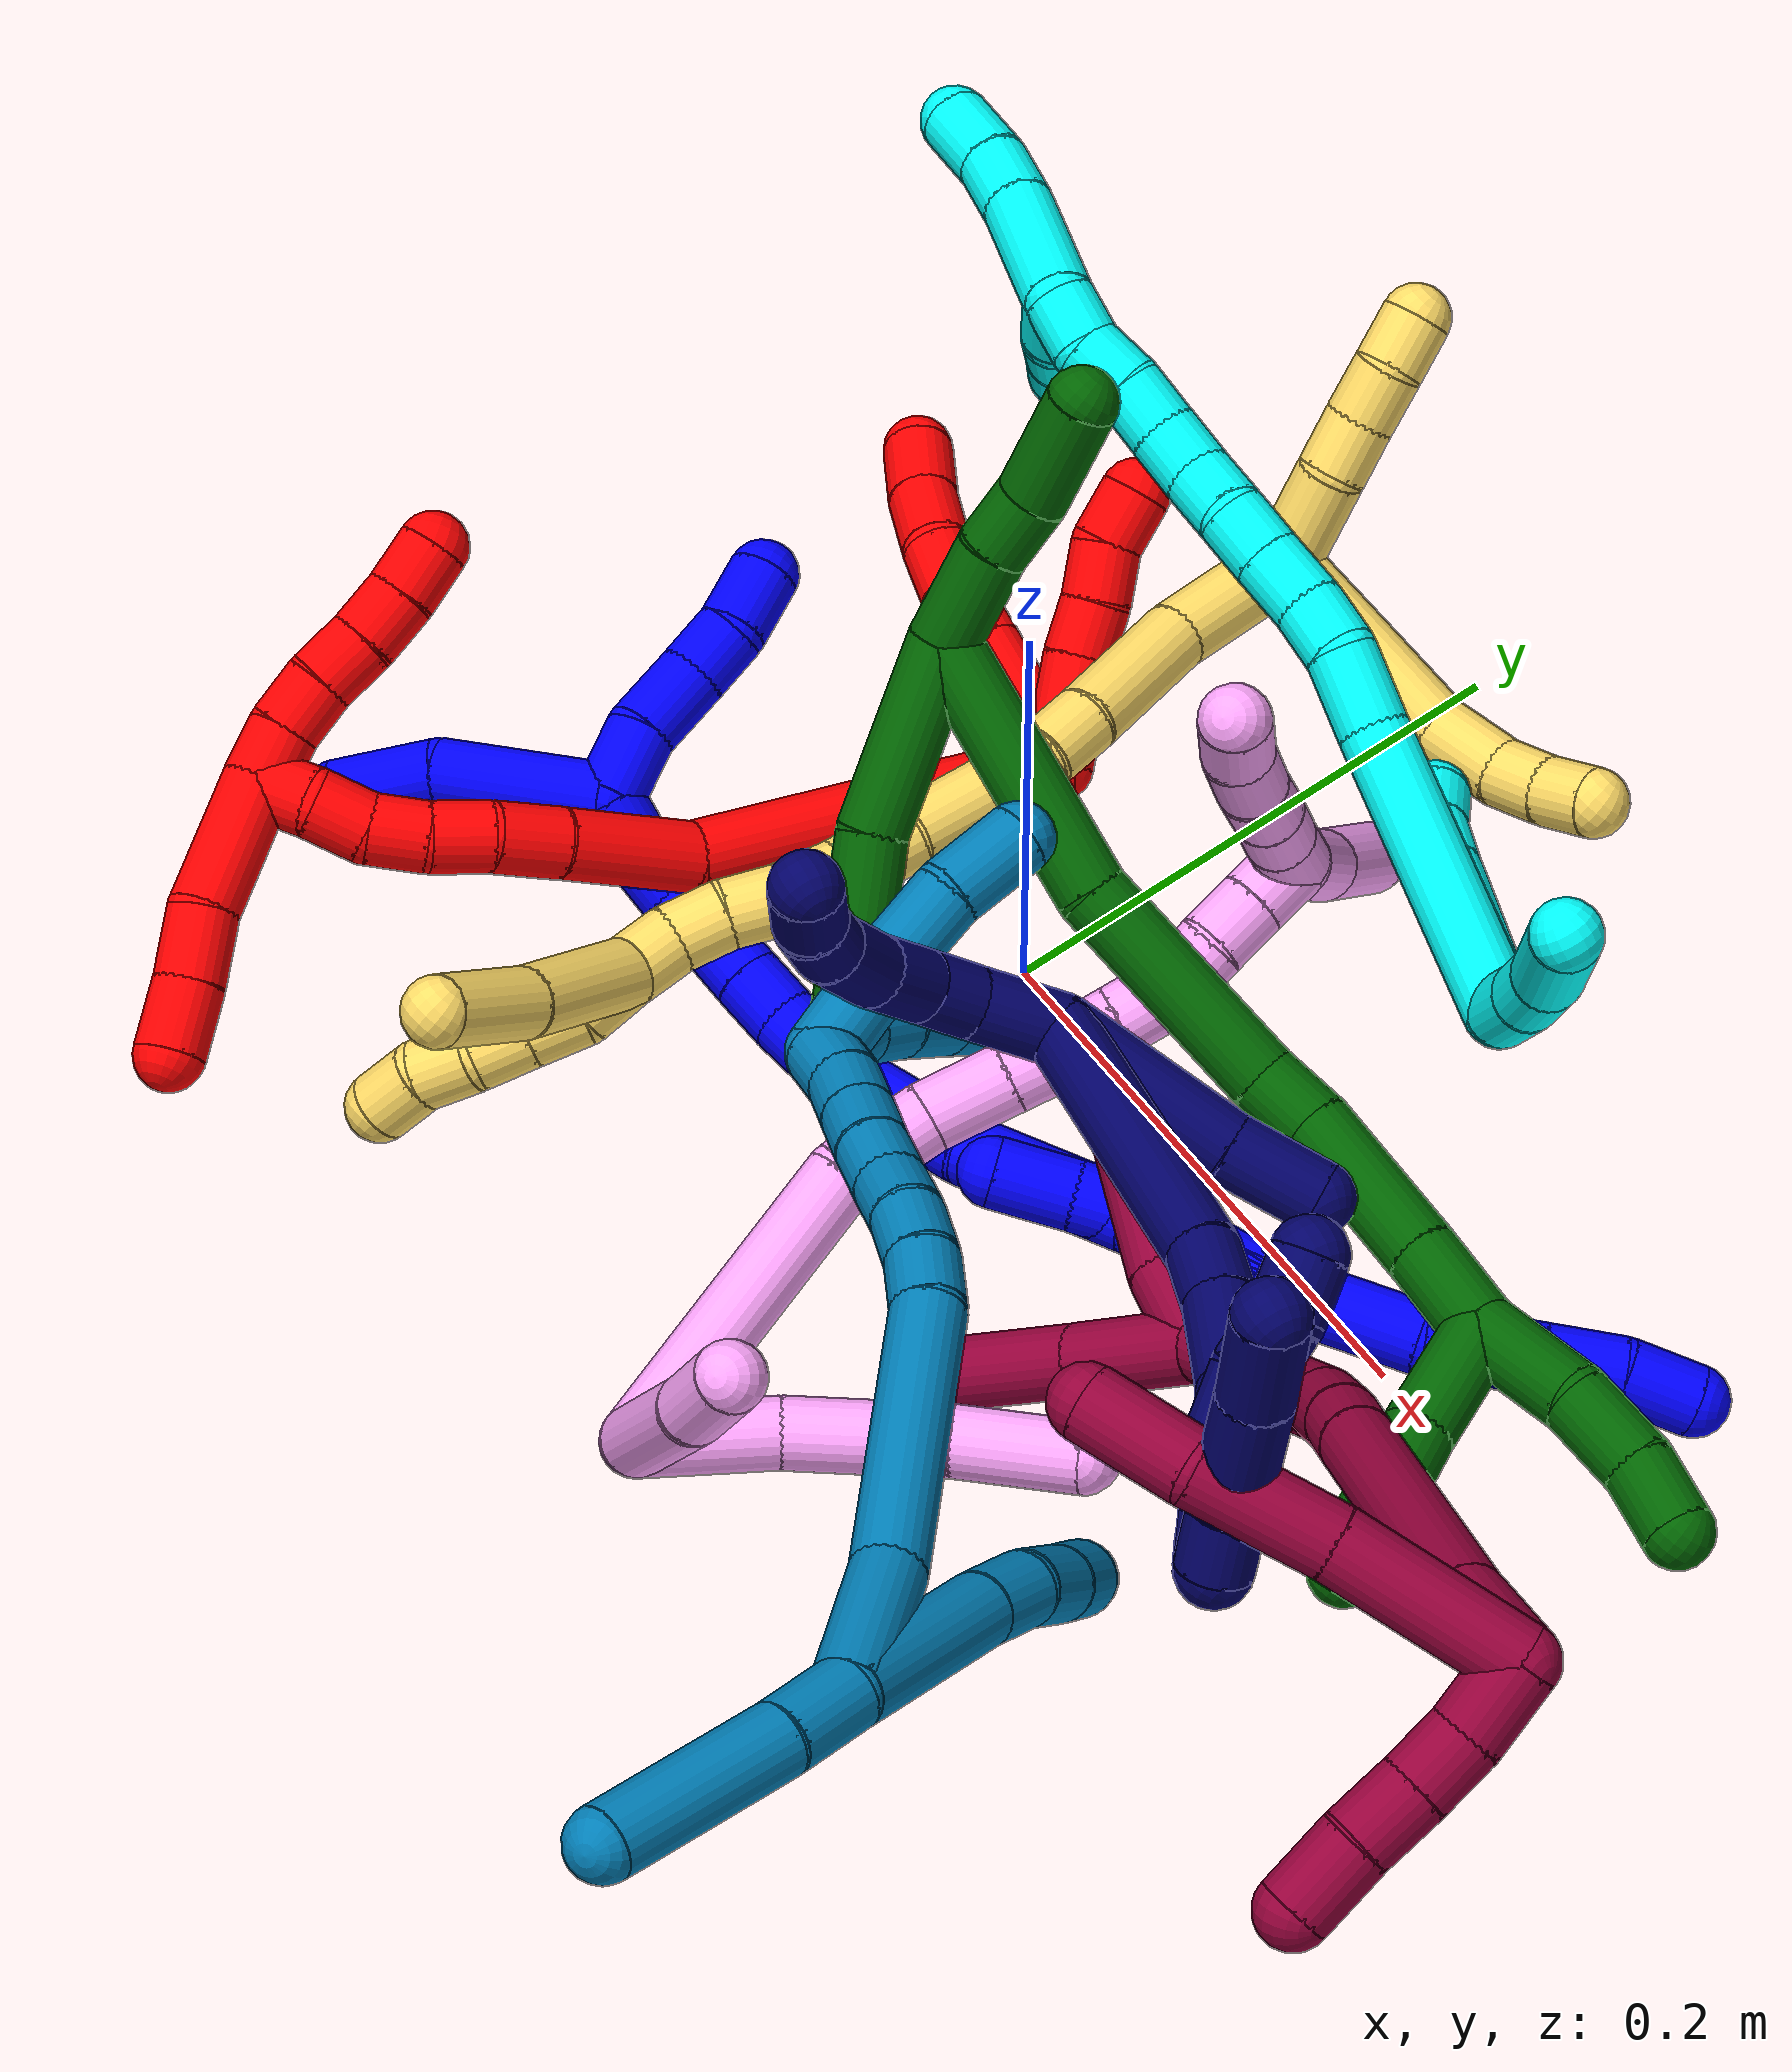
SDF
<sdf version="1.7">
 <world name="default">
  <plugin name="TubeGeneratorPlugin" filename="libtube_generator_plugin.so"/>
  <model name="photoneo_s_sensor">
   <static>1</static>
   <pose>0 0 2 1.57079 1.57079 3.14159</pose>
   <link name="link">
    <inertial><mass>0.1</mass></inertial>
    <sensor name="sensor" type="depth">
     <update_rate>30</update_rate>
     <camera>
      <horizontal_fov>1.22</horizontal_fov>
      <image><width>1920</width><height>1200</height><format>B8G8R8</format></image>
      <clip><near>0.1</near><far>4</far></clip>
      <depth_camera><output>points</output></depth_camera>
     </camera>
     <plugin name="camera_plugin" filename="libgazebo_ros_depth_camera.so">
      <baseline>0.2</baseline>
      <alwaysOn>1</alwaysOn>
      <updateRate>0.0</updateRate>
      <cameraName>camera_ir</cameraName>
      <imageTopicName>/camera/color/image_raw</imageTopicName>
      <cameraInfoTopicName>/camera/color/camera_info</cameraInfoTopicName>
      <depthImageTopicName>/camera/depth/image_raw</depthImageTopicName>
      <depthImageCameraInfoTopicName>/camera/depth/camera_info</depthImageCameraInfoTopicName>
      <pointCloudTopicName>/camera/depth/points</pointCloudTopicName>
      <frameName>fr_optical</frameName>
      <pointCloudCutoff>0.1</pointCloudCutoff>
      <pointCloudCutoffMax>2.0</pointCloudCutoffMax>
      <distortionK1>0</distortionK1>
      <distortionK2>0</distortionK2>
      <distortionK3>0</distortionK3>
      <distortionT1>0</distortionT1>
      <distortionT2>0</distortionT2>
      <CxPrime>0</CxPrime>
      <Cx>0</Cx>
      <Cy>0</Cy>
      <focalLength>0</focalLength>
      <hackBaseline>0</hackBaseline>
     </plugin>
    </sensor>
   </link>
  </model>
  <gravity>0 0 -9.8</gravity>
  <magnetic_field>6e-06 2.3e-05 -4.2e-05</magnetic_field>
  <atmosphere type="adiabatic"/>
  <physics name="default_physics" default="0" type="ode">
   <max_step_size>0.003</max_step_size>
   <real_time_factor>1</real_time_factor>
   <real_time_update_rate>1000</real_time_update_rate>
   <max_contacts>10000</max_contacts>
   <ode>
    <solver>
     <type>quick</type>
     <iters>100</iters>
     <sor>1.3</sor>
     <use_dynamic_moi_rescaling>0</use_dynamic_moi_rescaling>
    </solver>
    <constraints>
     <contact_max_correcting_vel>0</contact_max_correcting_vel>
     <contact_surface_layer>0.001</contact_surface_layer>
     <cfm>0</cfm>
     <erp>0.2</erp>
    </constraints>
   </ode>
  </physics>
  <scene><ambient>0.4 0.4 0.4 1</ambient><background>0.7 0.7 0.7 1</background><shadows>0</shadows></scene>
  <audio><device>default</device></audio>
  <spherical_coordinates>
   <surface_model>EARTH_WGS84</surface_model>
   <latitude_deg>0</latitude_deg>
   <longitude_deg>0</longitude_deg>
   <elevation>0</elevation>
   <heading_deg>0</heading_deg>
  </spherical_coordinates>
  <model name="bin">
   <static>1</static>
   <link name="bottom">
    <collision name="collision-bottom">
     <pose>0 0 -0.01 0 -0 0</pose>
     <geometry><box><size>0.8 0.6 0.02</size></box></geometry>
     <surface>
      <friction><ode><mu>100</mu><mu2>100</mu2></ode></friction>
      <contact><collide_bitmask>65535</collide_bitmask></contact>
     </surface>
    </collision>
   </link>
   <link name="west_wall">
    <collision name="collision-west_wall">
     <pose>-0.41 0 0.1 0 -0 0</pose>
     <geometry><box><size>0.02 0.6 0.2</size></box></geometry>
     <surface>
      <friction><ode><mu>100</mu><mu2>100</mu2></ode></friction>
      <contact><collide_bitmask>65535</collide_bitmask></contact>
     </surface>
    </collision>
   </link>
   <link name="east_wall">
    <collision name="collision-east_wall">
     <pose>0.41 0 0.1 0 -0 0</pose>
     <geometry><box><size>0.02 0.6 0.2</size></box></geometry>
     <surface>
      <friction><ode><mu>100</mu><mu2>100</mu2></ode></friction>
      <contact><collide_bitmask>65535</collide_bitmask></contact>
     </surface>
    </collision>
   </link>
   <link name="south_wall">
    <collision name="collision-south_wall">
     <pose>0 -0.31 0.1 0 -0 0</pose>
     <geometry><box><size>0.8 0.02 0.2</size></box></geometry>
     <surface>
      <friction><ode><mu>100</mu><mu2>100</mu2></ode></friction>
      <contact><collide_bitmask>65535</collide_bitmask></contact>
     </surface>
    </collision>
   </link>
   <link name="north_wall">
    <collision name="collision-north_wall">
     <pose>0 0.31 0.1 0 -0 0</pose>
     <geometry><box><size>0.8 0.02 0.2</size></box></geometry>
     <surface>
      <friction><ode><mu>100</mu><mu2>100</mu2></ode></friction>
      <contact><collide_bitmask>65535</collide_bitmask></contact>
     </surface>
    </collision>
   </link>
  </model>
  <model name="1">
   <static>0</static>
   <link name="1">
    <collision name="collision-cylinder-e_1_2_8">
     <pose>0.00115 0.002707 0.027988 -0.096409 0.040873 -0.001972</pose>
     <geometry><cylinder><radius>0.0125</radius><length>0.056284</length></cylinder></geometry>
     <surface>
      <friction><ode><mu>1.16</mu><mu2>1.16</mu2><slip1>0</slip1><slip2>0</slip2></ode></friction>
      <contact><ode><kp>1e+06</kp><kd>1</kd><max_vel>0</max_vel><min_depth>0.001</min_depth></ode></contact>
     </surface>
    </collision>
    <visual name="visual-cylinder-e_1_2_8">
     <pose>0.00115 0.002707 0.027988 -0.096409 0.040873 -0.001972</pose>
     <geometry><cylinder><radius>0.0125</radius><length>0.056284</length></cylinder></geometry>
     <material><ambient>0 0 1 1</ambient></material>
    </visual>
    <collision name="collision-cylinder-e_2_8_9">
     <pose>-0.00056 0.010839 0.075466 -0.271496 -0.140444 0.019214</pose>
     <geometry><cylinder><radius>0.0125</radius><length>0.040864</length></cylinder></geometry>
     <surface>
      <friction><ode><mu>1.16</mu><mu2>1.16</mu2><slip1>0</slip1><slip2>0</slip2></ode></friction>
      <contact><ode><kp>1e+06</kp><kd>1</kd><max_vel>0</max_vel><min_depth>0.001</min_depth></ode></contact>
     </surface>
    </collision>
    <visual name="visual-cylinder-e_2_8_9">
     <pose>-0.00056 0.010839 0.075466 -0.271496 -0.140444 0.019214</pose>
     <geometry><cylinder><radius>0.0125</radius><length>0.040864</length></cylinder></geometry>
     <material><ambient>0 0 1 1</ambient></material>
    </visual>
    <collision name="collision-cylinder-e_3_9_10">
     <pose>-0.005263 0.019835 0.107899 -0.26917 -0.136405 0.018498</pose>
     <geometry><cylinder><radius>0.0125</radius><length>0.027106</length></cylinder></geometry>
     <surface>
      <friction><ode><mu>1.16</mu><mu2>1.16</mu2><slip1>0</slip1><slip2>0</slip2></ode></friction>
      <contact><ode><kp>1e+06</kp><kd>1</kd><max_vel>0</max_vel><min_depth>0.001</min_depth></ode></contact>
     </surface>
    </collision>
    <visual name="visual-cylinder-e_3_9_10">
     <pose>-0.005263 0.019835 0.107899 -0.26917 -0.136405 0.018498</pose>
     <geometry><cylinder><radius>0.0125</radius><length>0.027106</length></cylinder></geometry>
     <material><ambient>0 0 1 1</ambient></material>
    </visual>
    <collision name="collision-cylinder-e_4_10_6">
     <pose>-0.00642 0.027875 0.132895 -0.355146 0.05336 -0.009578</pose>
     <geometry><cylinder><radius>0.0125</radius><length>0.025747</length></cylinder></geometry>
     <surface>
      <friction><ode><mu>1.16</mu><mu2>1.16</mu2><slip1>0</slip1><slip2>0</slip2></ode></friction>
      <contact><ode><kp>1e+06</kp><kd>1</kd><max_vel>0</max_vel><min_depth>0.001</min_depth></ode></contact>
     </surface>
    </collision>
    <visual name="visual-cylinder-e_4_10_6">
     <pose>-0.00642 0.027875 0.132895 -0.355146 0.05336 -0.009578</pose>
     <geometry><cylinder><radius>0.0125</radius><length>0.025747</length></cylinder></geometry>
     <material><ambient>0 0 1 1</ambient></material>
    </visual>
    <collision name="collision-cylinder-e_1_2_11">
     <pose>-0.005503 0.001901 -0.02412 -3.06292 -0.223658 2.46745</pose>
     <geometry><cylinder><radius>0.0125</radius><length>0.049626</length></cylinder></geometry>
     <surface>
      <friction><ode><mu>1.16</mu><mu2>1.16</mu2><slip1>0</slip1><slip2>0</slip2></ode></friction>
      <contact><ode><kp>1e+06</kp><kd>1</kd><max_vel>0</max_vel><min_depth>0.001</min_depth></ode></contact>
     </surface>
    </collision>
    <visual name="visual-cylinder-e_1_2_11">
     <pose>-0.005503 0.001901 -0.02412 -3.06292 -0.223658 2.46745</pose>
     <geometry><cylinder><radius>0.0125</radius><length>0.049626</length></cylinder></geometry>
     <material><ambient>0 0 1 1</ambient></material>
    </visual>
    <collision name="collision-cylinder-e_2_11_12">
     <pose>-0.010947 0.002453 -0.058951 3.01622 0.005552 0.088388</pose>
     <geometry><cylinder><radius>0.0125</radius><length>0.021591</length></cylinder></geometry>
     <surface>
      <friction><ode><mu>1.16</mu><mu2>1.16</mu2><slip1>0</slip1><slip2>0</slip2></ode></friction>
      <contact><ode><kp>1e+06</kp><kd>1</kd><max_vel>0</max_vel><min_depth>0.001</min_depth></ode></contact>
     </surface>
    </collision>
    <visual name="visual-cylinder-e_2_11_12">
     <pose>-0.010947 0.002453 -0.058951 3.01622 0.005552 0.088388</pose>
     <geometry><cylinder><radius>0.0125</radius><length>0.021591</length></cylinder></geometry>
     <material><ambient>0 0 1 1</ambient></material>
    </visual>
    <collision name="collision-cylinder-e_3_12_5">
     <pose>-0.010538 -0.002246 -0.083654 2.90664 0.024228 0.204578</pose>
     <geometry><cylinder><radius>0.0125</radius><length>0.028783</length></cylinder></geometry>
     <surface>
      <friction><ode><mu>1.16</mu><mu2>1.16</mu2><slip1>0</slip1><slip2>0</slip2></ode></friction>
      <contact><ode><kp>1e+06</kp><kd>1</kd><max_vel>0</max_vel><min_depth>0.001</min_depth></ode></contact>
     </surface>
    </collision>
    <visual name="visual-cylinder-e_3_12_5">
     <pose>-0.010538 -0.002246 -0.083654 2.90664 0.024228 0.204578</pose>
     <geometry><cylinder><radius>0.0125</radius><length>0.028783</length></cylinder></geometry>
     <material><ambient>0 0 1 1</ambient></material>
    </visual>
    <collision name="collision-cylinder-e_1_2_13">
     <pose>-0.004564 0.001459 -0.024637 -3.08245 -0.182881 2.5175</pose>
     <geometry><cylinder><radius>0.0125</radius><length>0.050196</length></cylinder></geometry>
     <surface>
      <friction><ode><mu>1.16</mu><mu2>1.16</mu2><slip1>0</slip1><slip2>0</slip2></ode></friction>
      <contact><ode><kp>1e+06</kp><kd>1</kd><max_vel>0</max_vel><min_depth>0.001</min_depth></ode></contact>
     </surface>
    </collision>
    <visual name="visual-cylinder-e_1_2_13">
     <pose>-0.004564 0.001459 -0.024637 -3.08245 -0.182881 2.5175</pose>
     <geometry><cylinder><radius>0.0125</radius><length>0.050196</length></cylinder></geometry>
     <material><ambient>0 0 1 1</ambient></material>
    </visual>
    <collision name="collision-cylinder-e_2_13_14">
     <pose>-0.012759 0.007416 -0.081214 -3.00167 -0.11207 1.35007</pose>
     <geometry><cylinder><radius>0.0125</radius><length>0.06492</length></cylinder></geometry>
     <surface>
      <friction><ode><mu>1.16</mu><mu2>1.16</mu2><slip1>0</slip1><slip2>0</slip2></ode></friction>
      <contact><ode><kp>1e+06</kp><kd>1</kd><max_vel>0</max_vel><min_depth>0.001</min_depth></ode></contact>
     </surface>
    </collision>
    <visual name="visual-cylinder-e_2_13_14">
     <pose>-0.012759 0.007416 -0.081214 -3.00167 -0.11207 1.35007</pose>
     <geometry><cylinder><radius>0.0125</radius><length>0.06492</length></cylinder></geometry>
     <material><ambient>0 0 1 1</ambient></material>
    </visual>
    <collision name="collision-cylinder-e_3_14_15">
     <pose>-0.021811 0.016135 -0.133895 -2.94087 -0.250795 1.79351</pose>
     <geometry><cylinder><radius>0.0125</radius><length>0.043696</length></cylinder></geometry>
     <surface>
      <friction><ode><mu>1.16</mu><mu2>1.16</mu2><slip1>0</slip1><slip2>0</slip2></ode></friction>
      <contact><ode><kp>1e+06</kp><kd>1</kd><max_vel>0</max_vel><min_depth>0.001</min_depth></ode></contact>
     </surface>
    </collision>
    <visual name="visual-cylinder-e_3_14_15">
     <pose>-0.021811 0.016135 -0.133895 -2.94087 -0.250795 1.79351</pose>
     <geometry><cylinder><radius>0.0125</radius><length>0.043696</length></cylinder></geometry>
     <material><ambient>0 0 1 1</ambient></material>
    </visual>
    <collision name="collision-cylinder-e_4_15_16">
     <pose>-0.03103 0.022889 -0.164049 -2.87861 -0.371333 1.91462</pose>
     <geometry><cylinder><radius>0.0125</radius><length>0.020927</length></cylinder></geometry>
     <surface>
      <friction><ode><mu>1.16</mu><mu2>1.16</mu2><slip1>0</slip1><slip2>0</slip2></ode></friction>
      <contact><ode><kp>1e+06</kp><kd>1</kd><max_vel>0</max_vel><min_depth>0.001</min_depth></ode></contact>
     </surface>
    </collision>
    <visual name="visual-cylinder-e_4_15_16">
     <pose>-0.03103 0.022889 -0.164049 -2.87861 -0.371333 1.91462</pose>
     <geometry><cylinder><radius>0.0125</radius><length>0.020927</length></cylinder></geometry>
     <material><ambient>0 0 1 1</ambient></material>
    </visual>
    <collision name="collision-cylinder-e_5_16_17">
     <pose>-0.039245 0.026849 -0.182409 -2.98363 -0.453837 2.48112</pose>
     <geometry><cylinder><radius>0.0125</radius><length>0.020155</length></cylinder></geometry>
     <surface>
      <friction><ode><mu>1.16</mu><mu2>1.16</mu2><slip1>0</slip1><slip2>0</slip2></ode></friction>
      <contact><ode><kp>1e+06</kp><kd>1</kd><max_vel>0</max_vel><min_depth>0.001</min_depth></ode></contact>
     </surface>
    </collision>
    <visual name="visual-cylinder-e_5_16_17">
     <pose>-0.039245 0.026849 -0.182409 -2.98363 -0.453837 2.48112</pose>
     <geometry><cylinder><radius>0.0125</radius><length>0.020155</length></cylinder></geometry>
     <material><ambient>0 0 1 1</ambient></material>
    </visual>
    <collision name="collision-cylinder-e_6_17_18">
     <pose>-0.048753 0.028614 -0.199979 -3.10215 -0.532796 2.9973</pose>
     <geometry><cylinder><radius>0.0125</radius><length>0.020042</length></cylinder></geometry>
     <surface>
      <friction><ode><mu>1.16</mu><mu2>1.16</mu2><slip1>0</slip1><slip2>0</slip2></ode></friction>
      <contact><ode><kp>1e+06</kp><kd>1</kd><max_vel>0</max_vel><min_depth>0.001</min_depth></ode></contact>
     </surface>
    </collision>
    <visual name="visual-cylinder-e_6_17_18">
     <pose>-0.048753 0.028614 -0.199979 -3.10215 -0.532796 2.9973</pose>
     <geometry><cylinder><radius>0.0125</radius><length>0.020042</length></cylinder></geometry>
     <material><ambient>0 0 1 1</ambient></material>
    </visual>
    <collision name="collision-cylinder-e_7_18_19">
     <pose>-0.059146 0.029443 -0.21709 -3.08406 -0.557753 2.94129</pose>
     <geometry><cylinder><radius>0.0125</radius><length>0.020038</length></cylinder></geometry>
     <surface>
      <friction><ode><mu>1.16</mu><mu2>1.16</mu2><slip1>0</slip1><slip2>0</slip2></ode></friction>
      <contact><ode><kp>1e+06</kp><kd>1</kd><max_vel>0</max_vel><min_depth>0.001</min_depth></ode></contact>
     </surface>
    </collision>
    <visual name="visual-cylinder-e_7_18_19">
     <pose>-0.059146 0.029443 -0.21709 -3.08406 -0.557753 2.94129</pose>
     <geometry><cylinder><radius>0.0125</radius><length>0.020038</length></cylinder></geometry>
     <material><ambient>0 0 1 1</ambient></material>
    </visual>
    <collision name="collision-cylinder-e_8_19_20">
     <pose>-0.069553 0.029109 -0.234144 3.04583 -0.535311 -2.79562</pose>
     <geometry><cylinder><radius>0.0125</radius><length>0.020013</length></cylinder></geometry>
     <surface>
      <friction><ode><mu>1.16</mu><mu2>1.16</mu2><slip1>0</slip1><slip2>0</slip2></ode></friction>
      <contact><ode><kp>1e+06</kp><kd>1</kd><max_vel>0</max_vel><min_depth>0.001</min_depth></ode></contact>
     </surface>
    </collision>
    <visual name="visual-cylinder-e_8_19_20">
     <pose>-0.069553 0.029109 -0.234144 3.04583 -0.535311 -2.79562</pose>
     <geometry><cylinder><radius>0.0125</radius><length>0.020013</length></cylinder></geometry>
     <material><ambient>0 0 1 1</ambient></material>
    </visual>
    <collision name="collision-cylinder-e_9_20_21">
     <pose>-0.080158 0.025368 -0.250544 2.78498 -0.581945 -2.05811</pose>
     <geometry><cylinder><radius>0.0125</radius><length>0.020012</length></cylinder></geometry>
     <surface>
      <friction><ode><mu>1.16</mu><mu2>1.16</mu2><slip1>0</slip1><slip2>0</slip2></ode></friction>
      <contact><ode><kp>1e+06</kp><kd>1</kd><max_vel>0</max_vel><min_depth>0.001</min_depth></ode></contact>
     </surface>
    </collision>
    <visual name="visual-cylinder-e_9_20_21">
     <pose>-0.080158 0.025368 -0.250544 2.78498 -0.581945 -2.05811</pose>
     <geometry><cylinder><radius>0.0125</radius><length>0.020012</length></cylinder></geometry>
     <material><ambient>0 0 1 1</ambient></material>
    </visual>
    <collision name="collision-cylinder-e_10_21_1">
     <pose>-0.092122 0.018463 -0.264883 2.59181 -0.702885 -1.83026</pose>
     <geometry><cylinder><radius>0.0125</radius><length>0.020001</length></cylinder></geometry>
     <surface>
      <friction><ode><mu>1.16</mu><mu2>1.16</mu2><slip1>0</slip1><slip2>0</slip2></ode></friction>
      <contact><ode><kp>1e+06</kp><kd>1</kd><max_vel>0</max_vel><min_depth>0.001</min_depth></ode></contact>
     </surface>
    </collision>
    <visual name="visual-cylinder-e_10_21_1">
     <pose>-0.092122 0.018463 -0.264883 2.59181 -0.702885 -1.83026</pose>
     <geometry><cylinder><radius>0.0125</radius><length>0.020001</length></cylinder></geometry>
     <material><ambient>0 0 1 1</ambient></material>
    </visual>
    <collision name="collision-cylinder-e_1_1_22">
     <pose>-0.095126 0.016364 -0.302194 -3.08037 0.111652 -2.13908</pose>
     <geometry><cylinder><radius>0.0125</radius><length>0.062113</length></cylinder></geometry>
     <surface>
      <friction><ode><mu>1.16</mu><mu2>1.16</mu2><slip1>0</slip1><slip2>0</slip2></ode></friction>
      <contact><ode><kp>1e+06</kp><kd>1</kd><max_vel>0</max_vel><min_depth>0.001</min_depth></ode></contact>
     </surface>
    </collision>
    <visual name="visual-cylinder-e_1_1_22">
     <pose>-0.095126 0.016364 -0.302194 -3.08037 0.111652 -2.13908</pose>
     <geometry><cylinder><radius>0.0125</radius><length>0.062113</length></cylinder></geometry>
     <material><ambient>0 0 1 1</ambient></material>
    </visual>
    <collision name="collision-cylinder-e_2_22_4">
     <pose>-0.083394 0.019925 -0.34996 -3.04328 0.451867 -2.71991</pose>
     <geometry><cylinder><radius>0.0125</radius><length>0.037887</length></cylinder></geometry>
     <surface>
      <friction><ode><mu>1.16</mu><mu2>1.16</mu2><slip1>0</slip1><slip2>0</slip2></ode></friction>
      <contact><ode><kp>1e+06</kp><kd>1</kd><max_vel>0</max_vel><min_depth>0.001</min_depth></ode></contact>
     </surface>
    </collision>
    <visual name="visual-cylinder-e_2_22_4">
     <pose>-0.083394 0.019925 -0.34996 -3.04328 0.451867 -2.71991</pose>
     <geometry><cylinder><radius>0.0125</radius><length>0.037887</length></cylinder></geometry>
     <material><ambient>0 0 1 1</ambient></material>
    </visual>
    <collision name="collision-cylinder-e_1_1_23">
     <pose>-0.111592 0.017142 -0.270277 -1.17552 -1.35226 0.981841</pose>
     <geometry><cylinder><radius>0.0125</radius><length>0.026645</length></cylinder></geometry>
     <surface>
      <friction><ode><mu>1.16</mu><mu2>1.16</mu2><slip1>0</slip1><slip2>0</slip2></ode></friction>
      <contact><ode><kp>1e+06</kp><kd>1</kd><max_vel>0</max_vel><min_depth>0.001</min_depth></ode></contact>
     </surface>
    </collision>
    <visual name="visual-cylinder-e_1_1_23">
     <pose>-0.111592 0.017142 -0.270277 -1.17552 -1.35226 0.981841</pose>
     <geometry><cylinder><radius>0.0125</radius><length>0.026645</length></cylinder></geometry>
     <material><ambient>0 0 1 1</ambient></material>
    </visual>
    <collision name="collision-cylinder-e_2_23_24">
     <pose>-0.137223 0.024593 -0.264865 -0.838871 -1.0995 0.533437</pose>
     <geometry><cylinder><radius>0.0125</radius><length>0.028341</length></cylinder></geometry>
     <surface>
      <friction><ode><mu>1.16</mu><mu2>1.16</mu2><slip1>0</slip1><slip2>0</slip2></ode></friction>
      <contact><ode><kp>1e+06</kp><kd>1</kd><max_vel>0</max_vel><min_depth>0.001</min_depth></ode></contact>
     </surface>
    </collision>
    <visual name="visual-cylinder-e_2_23_24">
     <pose>-0.137223 0.024593 -0.264865 -0.838871 -1.0995 0.533437</pose>
     <geometry><cylinder><radius>0.0125</radius><length>0.028341</length></cylinder></geometry>
     <material><ambient>0 0 1 1</ambient></material>
    </visual>
    <collision name="collision-cylinder-e_3_24_25">
     <pose>-0.159421 0.030643 -0.25667 -0.313608 -1.16657 0.207901</pose>
     <geometry><cylinder><radius>0.0125</radius><length>0.020822</length></cylinder></geometry>
     <surface>
      <friction><ode><mu>1.16</mu><mu2>1.16</mu2><slip1>0</slip1><slip2>0</slip2></ode></friction>
      <contact><ode><kp>1e+06</kp><kd>1</kd><max_vel>0</max_vel><min_depth>0.001</min_depth></ode></contact>
     </surface>
    </collision>
    <visual name="visual-cylinder-e_3_24_25">
     <pose>-0.159421 0.030643 -0.25667 -0.313608 -1.16657 0.207901</pose>
     <geometry><cylinder><radius>0.0125</radius><length>0.020822</length></cylinder></geometry>
     <material><ambient>0 0 1 1</ambient></material>
    </visual>
    <collision name="collision-cylinder-e_4_25_3">
     <pose>-0.180457 0.035501 -0.251371 -1.19849 -1.24603 0.912413</pose>
     <geometry><cylinder><radius>0.0125</radius><length>0.024192</length></cylinder></geometry>
     <surface>
      <friction><ode><mu>1.16</mu><mu2>1.16</mu2><slip1>0</slip1><slip2>0</slip2></ode></friction>
      <contact><ode><kp>1e+06</kp><kd>1</kd><max_vel>0</max_vel><min_depth>0.001</min_depth></ode></contact>
     </surface>
    </collision>
    <visual name="visual-cylinder-e_4_25_3">
     <pose>-0.180457 0.035501 -0.251371 -1.19849 -1.24603 0.912413</pose>
     <geometry><cylinder><radius>0.0125</radius><length>0.024192</length></cylinder></geometry>
     <material><ambient>0 0 1 1</ambient></material>
    </visual>
    <collision name="collision-sphere-3">
     <pose>-0.19192 0.039096 -0.249967 0 -0 0</pose>
     <geometry><sphere><radius>0.0125</radius></sphere></geometry>
     <surface>
      <friction><ode><mu>1.16</mu><mu2>1.16</mu2><slip1>0</slip1><slip2>0</slip2></ode></friction>
      <contact><ode><kp>1e+06</kp><kd>1</kd><max_vel>0</max_vel><min_depth>0.001</min_depth></ode></contact>
     </surface>
    </collision>
    <visual name="visual-sphere-3">
     <pose>-0.19192 0.039096 -0.249967 0 -0 0</pose>
     <geometry><sphere><radius>0.0125</radius></sphere></geometry>
     <material><ambient>0 0 1 1</ambient></material>
    </visual>
    <collision name="collision-sphere-25">
     <pose>-0.168993 0.031906 -0.252775 0 -0 0</pose>
     <geometry><sphere><radius>0.0125</radius></sphere></geometry>
     <surface>
      <friction><ode><mu>1.16</mu><mu2>1.16</mu2><slip1>0</slip1><slip2>0</slip2></ode></friction>
      <contact><ode><kp>1e+06</kp><kd>1</kd><max_vel>0</max_vel><min_depth>0.001</min_depth></ode></contact>
     </surface>
    </collision>
    <visual name="visual-sphere-25">
     <pose>-0.168993 0.031906 -0.252775 0 -0 0</pose>
     <geometry><sphere><radius>0.0125</radius></sphere></geometry>
     <material><ambient>0 0 1 1</ambient></material>
    </visual>
    <collision name="collision-sphere-24">
     <pose>-0.149849 0.029379 -0.260565 0 -0 0</pose>
     <geometry><sphere><radius>0.0125</radius></sphere></geometry>
     <surface>
      <friction><ode><mu>1.16</mu><mu2>1.16</mu2><slip1>0</slip1><slip2>0</slip2></ode></friction>
      <contact><ode><kp>1e+06</kp><kd>1</kd><max_vel>0</max_vel><min_depth>0.001</min_depth></ode></contact>
     </surface>
    </collision>
    <visual name="visual-sphere-24">
     <pose>-0.149849 0.029379 -0.260565 0 -0 0</pose>
     <geometry><sphere><radius>0.0125</radius></sphere></geometry>
     <material><ambient>0 0 1 1</ambient></material>
    </visual>
    <collision name="collision-sphere-23">
     <pose>-0.124598 0.019807 -0.269165 0 -0 0</pose>
     <geometry><sphere><radius>0.0125</radius></sphere></geometry>
     <surface>
      <friction><ode><mu>1.16</mu><mu2>1.16</mu2><slip1>0</slip1><slip2>0</slip2></ode></friction>
      <contact><ode><kp>1e+06</kp><kd>1</kd><max_vel>0</max_vel><min_depth>0.001</min_depth></ode></contact>
     </surface>
    </collision>
    <visual name="visual-sphere-23">
     <pose>-0.124598 0.019807 -0.269165 0 -0 0</pose>
     <geometry><sphere><radius>0.0125</radius></sphere></geometry>
     <material><ambient>0 0 1 1</ambient></material>
    </visual>
    <collision name="collision-sphere-4">
     <pose>-0.075123 0.021598 -0.36692 0 -0 0</pose>
     <geometry><sphere><radius>0.0125</radius></sphere></geometry>
     <surface>
      <friction><ode><mu>1.16</mu><mu2>1.16</mu2><slip1>0</slip1><slip2>0</slip2></ode></friction>
      <contact><ode><kp>1e+06</kp><kd>1</kd><max_vel>0</max_vel><min_depth>0.001</min_depth></ode></contact>
     </surface>
    </collision>
    <visual name="visual-sphere-4">
     <pose>-0.075123 0.021598 -0.36692 0 -0 0</pose>
     <geometry><sphere><radius>0.0125</radius></sphere></geometry>
     <material><ambient>0 0 1 1</ambient></material>
    </visual>
    <collision name="collision-sphere-22">
     <pose>-0.091666 0.018253 -0.333 0 -0 0</pose>
     <geometry><sphere><radius>0.0125</radius></sphere></geometry>
     <surface>
      <friction><ode><mu>1.16</mu><mu2>1.16</mu2><slip1>0</slip1><slip2>0</slip2></ode></friction>
      <contact><ode><kp>1e+06</kp><kd>1</kd><max_vel>0</max_vel><min_depth>0.001</min_depth></ode></contact>
     </surface>
    </collision>
    <visual name="visual-sphere-22">
     <pose>-0.091666 0.018253 -0.333 0 -0 0</pose>
     <geometry><sphere><radius>0.0125</radius></sphere></geometry>
     <material><ambient>0 0 1 1</ambient></material>
    </visual>
    <collision name="collision-sphere-1">
     <pose>-0.098587 0.014476 -0.271389 0 -0 0</pose>
     <geometry><sphere><radius>0.0125</radius></sphere></geometry>
     <surface>
      <friction><ode><mu>1.16</mu><mu2>1.16</mu2><slip1>0</slip1><slip2>0</slip2></ode></friction>
      <contact><ode><kp>1e+06</kp><kd>1</kd><max_vel>0</max_vel><min_depth>0.001</min_depth></ode></contact>
     </surface>
    </collision>
    <visual name="visual-sphere-1">
     <pose>-0.098587 0.014476 -0.271389 0 -0 0</pose>
     <geometry><sphere><radius>0.0125</radius></sphere></geometry>
     <material><ambient>0 0 1 1</ambient></material>
    </visual>
    <collision name="collision-sphere-21">
     <pose>-0.085657 0.02245 -0.258377 0 -0 0</pose>
     <geometry><sphere><radius>0.0125</radius></sphere></geometry>
     <surface>
      <friction><ode><mu>1.16</mu><mu2>1.16</mu2><slip1>0</slip1><slip2>0</slip2></ode></friction>
      <contact><ode><kp>1e+06</kp><kd>1</kd><max_vel>0</max_vel><min_depth>0.001</min_depth></ode></contact>
     </surface>
    </collision>
    <visual name="visual-sphere-21">
     <pose>-0.085657 0.02245 -0.258377 0 -0 0</pose>
     <geometry><sphere><radius>0.0125</radius></sphere></geometry>
     <material><ambient>0 0 1 1</ambient></material>
    </visual>
    <collision name="collision-sphere-11">
     <pose>-0.011007 0.003803 -0.048241 0 -0 0</pose>
     <geometry><sphere><radius>0.0125</radius></sphere></geometry>
     <surface>
      <friction><ode><mu>1.16</mu><mu2>1.16</mu2><slip1>0</slip1><slip2>0</slip2></ode></friction>
      <contact><ode><kp>1e+06</kp><kd>1</kd><max_vel>0</max_vel><min_depth>0.001</min_depth></ode></contact>
     </surface>
    </collision>
    <visual name="visual-sphere-11">
     <pose>-0.011007 0.003803 -0.048241 0 -0 0</pose>
     <geometry><sphere><radius>0.0125</radius></sphere></geometry>
     <material><ambient>0 0 1 1</ambient></material>
    </visual>
    <collision name="collision-sphere-6">
     <pose>-0.005733 0.032345 0.144948 0 -0 0</pose>
     <geometry><sphere><radius>0.0125</radius></sphere></geometry>
     <surface>
      <friction><ode><mu>1.16</mu><mu2>1.16</mu2><slip1>0</slip1><slip2>0</slip2></ode></friction>
      <contact><ode><kp>1e+06</kp><kd>1</kd><max_vel>0</max_vel><min_depth>0.001</min_depth></ode></contact>
     </surface>
    </collision>
    <visual name="visual-sphere-6">
     <pose>-0.005733 0.032345 0.144948 0 -0 0</pose>
     <geometry><sphere><radius>0.0125</radius></sphere></geometry>
     <material><ambient>0 0 1 1</ambient></material>
    </visual>
    <collision name="collision-sphere-10">
     <pose>-0.007106 0.023405 0.120842 0 -0 0</pose>
     <geometry><sphere><radius>0.0125</radius></sphere></geometry>
     <surface>
      <friction><ode><mu>1.16</mu><mu2>1.16</mu2><slip1>0</slip1><slip2>0</slip2></ode></friction>
      <contact><ode><kp>1e+06</kp><kd>1</kd><max_vel>0</max_vel><min_depth>0.001</min_depth></ode></contact>
     </surface>
    </collision>
    <visual name="visual-sphere-10">
     <pose>-0.007106 0.023405 0.120842 0 -0 0</pose>
     <geometry><sphere><radius>0.0125</radius></sphere></geometry>
     <material><ambient>0 0 1 1</ambient></material>
    </visual>
    <collision name="collision-sphere-9">
     <pose>-0.00342 0.016264 0.094955 0 -0 0</pose>
     <geometry><sphere><radius>0.0125</radius></sphere></geometry>
     <surface>
      <friction><ode><mu>1.16</mu><mu2>1.16</mu2><slip1>0</slip1><slip2>0</slip2></ode></friction>
      <contact><ode><kp>1e+06</kp><kd>1</kd><max_vel>0</max_vel><min_depth>0.001</min_depth></ode></contact>
     </surface>
    </collision>
    <visual name="visual-sphere-9">
     <pose>-0.00342 0.016264 0.094955 0 -0 0</pose>
     <geometry><sphere><radius>0.0125</radius></sphere></geometry>
     <material><ambient>0 0 1 1</ambient></material>
    </visual>
    <collision name="collision-sphere-2">
     <geometry><sphere><radius>0.0125</radius></sphere></geometry>
     <surface>
      <friction><ode><mu>1.16</mu><mu2>1.16</mu2><slip1>0</slip1><slip2>0</slip2></ode></friction>
      <contact><ode><kp>1e+06</kp><kd>1</kd><max_vel>0</max_vel><min_depth>0.001</min_depth></ode></contact>
     </surface>
    </collision>
    <visual name="visual-sphere-2">
     <geometry><sphere><radius>0.0125</radius></sphere></geometry>
     <material><ambient>0 0 1 1</ambient></material>
    </visual>
    <collision name="collision-sphere-19">
     <pose>-0.064449 0.029932 -0.225577 0 -0 0</pose>
     <geometry><sphere><radius>0.0125</radius></sphere></geometry>
     <surface>
      <friction><ode><mu>1.16</mu><mu2>1.16</mu2><slip1>0</slip1><slip2>0</slip2></ode></friction>
      <contact><ode><kp>1e+06</kp><kd>1</kd><max_vel>0</max_vel><min_depth>0.001</min_depth></ode></contact>
     </surface>
    </collision>
    <visual name="visual-sphere-19">
     <pose>-0.064449 0.029932 -0.225577 0 -0 0</pose>
     <geometry><sphere><radius>0.0125</radius></sphere></geometry>
     <material><ambient>0 0 1 1</ambient></material>
    </visual>
    <collision name="collision-sphere-8">
     <pose>0.0023 0.005413 0.055976 0 -0 0</pose>
     <geometry><sphere><radius>0.0125</radius></sphere></geometry>
     <surface>
      <friction><ode><mu>1.16</mu><mu2>1.16</mu2><slip1>0</slip1><slip2>0</slip2></ode></friction>
      <contact><ode><kp>1e+06</kp><kd>1</kd><max_vel>0</max_vel><min_depth>0.001</min_depth></ode></contact>
     </surface>
    </collision>
    <visual name="visual-sphere-8">
     <pose>0.0023 0.005413 0.055976 0 -0 0</pose>
     <geometry><sphere><radius>0.0125</radius></sphere></geometry>
     <material><ambient>0 0 1 1</ambient></material>
    </visual>
    <collision name="collision-sphere-12">
     <pose>-0.010887 0.001103 -0.069662 0 -0 0</pose>
     <geometry><sphere><radius>0.0125</radius></sphere></geometry>
     <surface>
      <friction><ode><mu>1.16</mu><mu2>1.16</mu2><slip1>0</slip1><slip2>0</slip2></ode></friction>
      <contact><ode><kp>1e+06</kp><kd>1</kd><max_vel>0</max_vel><min_depth>0.001</min_depth></ode></contact>
     </surface>
    </collision>
    <visual name="visual-sphere-12">
     <pose>-0.010887 0.001103 -0.069662 0 -0 0</pose>
     <geometry><sphere><radius>0.0125</radius></sphere></geometry>
     <material><ambient>0 0 1 1</ambient></material>
    </visual>
    <collision name="collision-sphere-5">
     <pose>-0.01019 -0.005596 -0.097645 0 -0 0</pose>
     <geometry><sphere><radius>0.0125</radius></sphere></geometry>
     <surface>
      <friction><ode><mu>1.16</mu><mu2>1.16</mu2><slip1>0</slip1><slip2>0</slip2></ode></friction>
      <contact><ode><kp>1e+06</kp><kd>1</kd><max_vel>0</max_vel><min_depth>0.001</min_depth></ode></contact>
     </surface>
    </collision>
    <visual name="visual-sphere-5">
     <pose>-0.01019 -0.005596 -0.097645 0 -0 0</pose>
     <geometry><sphere><radius>0.0125</radius></sphere></geometry>
     <material><ambient>0 0 1 1</ambient></material>
    </visual>
    <collision name="collision-sphere-13">
     <pose>-0.009129 0.002918 -0.049273 0 -0 0</pose>
     <geometry><sphere><radius>0.0125</radius></sphere></geometry>
     <surface>
      <friction><ode><mu>1.16</mu><mu2>1.16</mu2><slip1>0</slip1><slip2>0</slip2></ode></friction>
      <contact><ode><kp>1e+06</kp><kd>1</kd><max_vel>0</max_vel><min_depth>0.001</min_depth></ode></contact>
     </surface>
    </collision>
    <visual name="visual-sphere-13">
     <pose>-0.009129 0.002918 -0.049273 0 -0 0</pose>
     <geometry><sphere><radius>0.0125</radius></sphere></geometry>
     <material><ambient>0 0 1 1</ambient></material>
    </visual>
    <collision name="collision-sphere-14">
     <pose>-0.016389 0.011915 -0.113155 0 -0 0</pose>
     <geometry><sphere><radius>0.0125</radius></sphere></geometry>
     <surface>
      <friction><ode><mu>1.16</mu><mu2>1.16</mu2><slip1>0</slip1><slip2>0</slip2></ode></friction>
      <contact><ode><kp>1e+06</kp><kd>1</kd><max_vel>0</max_vel><min_depth>0.001</min_depth></ode></contact>
     </surface>
    </collision>
    <visual name="visual-sphere-14">
     <pose>-0.016389 0.011915 -0.113155 0 -0 0</pose>
     <geometry><sphere><radius>0.0125</radius></sphere></geometry>
     <material><ambient>0 0 1 1</ambient></material>
    </visual>
    <collision name="collision-sphere-15">
     <pose>-0.027233 0.020354 -0.154634 0 -0 0</pose>
     <geometry><sphere><radius>0.0125</radius></sphere></geometry>
     <surface>
      <friction><ode><mu>1.16</mu><mu2>1.16</mu2><slip1>0</slip1><slip2>0</slip2></ode></friction>
      <contact><ode><kp>1e+06</kp><kd>1</kd><max_vel>0</max_vel><min_depth>0.001</min_depth></ode></contact>
     </surface>
    </collision>
    <visual name="visual-sphere-15">
     <pose>-0.027233 0.020354 -0.154634 0 -0 0</pose>
     <geometry><sphere><radius>0.0125</radius></sphere></geometry>
     <material><ambient>0 0 1 1</ambient></material>
    </visual>
    <collision name="collision-sphere-16">
     <pose>-0.034827 0.025424 -0.173464 0 -0 0</pose>
     <geometry><sphere><radius>0.0125</radius></sphere></geometry>
     <surface>
      <friction><ode><mu>1.16</mu><mu2>1.16</mu2><slip1>0</slip1><slip2>0</slip2></ode></friction>
      <contact><ode><kp>1e+06</kp><kd>1</kd><max_vel>0</max_vel><min_depth>0.001</min_depth></ode></contact>
     </surface>
    </collision>
    <visual name="visual-sphere-16">
     <pose>-0.034827 0.025424 -0.173464 0 -0 0</pose>
     <geometry><sphere><radius>0.0125</radius></sphere></geometry>
     <material><ambient>0 0 1 1</ambient></material>
    </visual>
    <collision name="collision-sphere-17">
     <pose>-0.043663 0.028273 -0.191353 0 -0 0</pose>
     <geometry><sphere><radius>0.0125</radius></sphere></geometry>
     <surface>
      <friction><ode><mu>1.16</mu><mu2>1.16</mu2><slip1>0</slip1><slip2>0</slip2></ode></friction>
      <contact><ode><kp>1e+06</kp><kd>1</kd><max_vel>0</max_vel><min_depth>0.001</min_depth></ode></contact>
     </surface>
    </collision>
    <visual name="visual-sphere-17">
     <pose>-0.043663 0.028273 -0.191353 0 -0 0</pose>
     <geometry><sphere><radius>0.0125</radius></sphere></geometry>
     <material><ambient>0 0 1 1</ambient></material>
    </visual>
    <collision name="collision-sphere-18">
     <pose>-0.053843 0.028954 -0.208604 0 -0 0</pose>
     <geometry><sphere><radius>0.0125</radius></sphere></geometry>
     <surface>
      <friction><ode><mu>1.16</mu><mu2>1.16</mu2><slip1>0</slip1><slip2>0</slip2></ode></friction>
      <contact><ode><kp>1e+06</kp><kd>1</kd><max_vel>0</max_vel><min_depth>0.001</min_depth></ode></contact>
     </surface>
    </collision>
    <visual name="visual-sphere-18">
     <pose>-0.053843 0.028954 -0.208604 0 -0 0</pose>
     <geometry><sphere><radius>0.0125</radius></sphere></geometry>
     <material><ambient>0 0 1 1</ambient></material>
    </visual>
    <collision name="collision-sphere-20">
     <pose>-0.074658 0.028286 -0.242711 0 -0 0</pose>
     <geometry><sphere><radius>0.0125</radius></sphere></geometry>
     <surface>
      <friction><ode><mu>1.16</mu><mu2>1.16</mu2><slip1>0</slip1><slip2>0</slip2></ode></friction>
      <contact><ode><kp>1e+06</kp><kd>1</kd><max_vel>0</max_vel><min_depth>0.001</min_depth></ode></contact>
     </surface>
    </collision>
    <visual name="visual-sphere-20">
     <pose>-0.074658 0.028286 -0.242711 0 -0 0</pose>
     <geometry><sphere><radius>0.0125</radius></sphere></geometry>
     <material><ambient>0 0 1 1</ambient></material>
    </visual>
    <inertial>
     <pose>-0.046862 0.015011 -0.12648 0 -0 0</pose>
     <mass>0.75</mass>
     <inertia><ixx>1.3e-05</ixx><ixy>0</ixy><ixz>0</ixz><iyy>0.00011</iyy><iyz>0</iyz><izz>-1.9e-05</izz></inertia>
    </inertial>
   </link>
   <pose>0.160496 -0.02226 0.030389 -1.5052 0.429595 -0.975627</pose>
  </model>
  <model name="2">
   <static>0</static>
   <link name="2">
    <collision name="collision-cylinder-e_1_2_8">
     <pose>-0.005874 -0.018274 0.018662 0.774912 -0.221209 -0.09058</pose>
     <geometry><cylinder><radius>0.0125</radius><length>0.053543</length></cylinder></geometry>
     <surface>
      <friction><ode><mu>1.16</mu><mu2>1.16</mu2><slip1>0</slip1><slip2>0</slip2></ode></friction>
      <contact><ode><kp>1e+06</kp><kd>1</kd><max_vel>0</max_vel><min_depth>0.001</min_depth></ode></contact>
     </surface>
    </collision>
    <visual name="visual-cylinder-e_1_2_8">
     <pose>-0.005874 -0.018274 0.018662 0.774912 -0.221209 -0.09058</pose>
     <geometry><cylinder><radius>0.0125</radius><length>0.053543</length></cylinder></geometry>
     <material><ambient>1 0 0 1</ambient></material>
    </visual>
    <collision name="collision-cylinder-e_2_8_9">
     <pose>-0.014408 -0.044685 0.045721 0.769558 -0.223733 -0.090921</pose>
     <geometry><cylinder><radius>0.0125</radius><length>0.023984</length></cylinder></geometry>
     <surface>
      <friction><ode><mu>1.16</mu><mu2>1.16</mu2><slip1>0</slip1><slip2>0</slip2></ode></friction>
      <contact><ode><kp>1e+06</kp><kd>1</kd><max_vel>0</max_vel><min_depth>0.001</min_depth></ode></contact>
     </surface>
    </collision>
    <visual name="visual-cylinder-e_2_8_9">
     <pose>-0.014408 -0.044685 0.045721 0.769558 -0.223733 -0.090921</pose>
     <geometry><cylinder><radius>0.0125</radius><length>0.023984</length></cylinder></geometry>
     <material><ambient>1 0 0 1</ambient></material>
    </visual>
    <collision name="collision-cylinder-e_3_9_10">
     <pose>-0.019918 -0.05845 0.062232 0.606615 -0.280911 -0.08844</pose>
     <geometry><cylinder><radius>0.0125</radius><length>0.020553</length></cylinder></geometry>
     <surface>
      <friction><ode><mu>1.16</mu><mu2>1.16</mu2><slip1>0</slip1><slip2>0</slip2></ode></friction>
      <contact><ode><kp>1e+06</kp><kd>1</kd><max_vel>0</max_vel><min_depth>0.001</min_depth></ode></contact>
     </surface>
    </collision>
    <visual name="visual-cylinder-e_3_9_10">
     <pose>-0.019918 -0.05845 0.062232 0.606615 -0.280911 -0.08844</pose>
     <geometry><cylinder><radius>0.0125</radius><length>0.020553</length></cylinder></geometry>
     <material><ambient>1 0 0 1</ambient></material>
    </visual>
    <collision name="collision-cylinder-e_4_10_11">
     <pose>-0.029231 -0.068937 0.080655 0.44032 -0.515821 -0.117927</pose>
     <geometry><cylinder><radius>0.0125</radius><length>0.026208</length></cylinder></geometry>
     <surface>
      <friction><ode><mu>1.16</mu><mu2>1.16</mu2><slip1>0</slip1><slip2>0</slip2></ode></friction>
      <contact><ode><kp>1e+06</kp><kd>1</kd><max_vel>0</max_vel><min_depth>0.001</min_depth></ode></contact>
     </surface>
    </collision>
    <visual name="visual-cylinder-e_4_10_11">
     <pose>-0.029231 -0.068937 0.080655 0.44032 -0.515821 -0.117927</pose>
     <geometry><cylinder><radius>0.0125</radius><length>0.026208</length></cylinder></geometry>
     <material><ambient>1 0 0 1</ambient></material>
    </visual>
    <collision name="collision-cylinder-e_5_11_6">
     <pose>-0.04126 -0.077468 0.101959 0.322405 -0.447745 -0.074017</pose>
     <geometry><cylinder><radius>0.0125</radius><length>0.025712</length></cylinder></geometry>
     <surface>
      <friction><ode><mu>1.16</mu><mu2>1.16</mu2><slip1>0</slip1><slip2>0</slip2></ode></friction>
      <contact><ode><kp>1e+06</kp><kd>1</kd><max_vel>0</max_vel><min_depth>0.001</min_depth></ode></contact>
     </surface>
    </collision>
    <visual name="visual-cylinder-e_5_11_6">
     <pose>-0.04126 -0.077468 0.101959 0.322405 -0.447745 -0.074017</pose>
     <geometry><cylinder><radius>0.0125</radius><length>0.025712</length></cylinder></geometry>
     <material><ambient>1 0 0 1</ambient></material>
    </visual>
    <collision name="collision-cylinder-e_1_2_12">
     <pose>0.004882 -0.003137 0.018576 0.167284 0.253571 0.021373</pose>
     <geometry><cylinder><radius>0.0125</radius><length>0.038922</length></cylinder></geometry>
     <surface>
      <friction><ode><mu>1.16</mu><mu2>1.16</mu2><slip1>0</slip1><slip2>0</slip2></ode></friction>
      <contact><ode><kp>1e+06</kp><kd>1</kd><max_vel>0</max_vel><min_depth>0.001</min_depth></ode></contact>
     </surface>
    </collision>
    <visual name="visual-cylinder-e_1_2_12">
     <pose>0.004882 -0.003137 0.018576 0.167284 0.253571 0.021373</pose>
     <geometry><cylinder><radius>0.0125</radius><length>0.038922</length></cylinder></geometry>
     <material><ambient>1 0 0 1</ambient></material>
    </visual>
    <collision name="collision-cylinder-e_2_12_13">
     <pose>0.013597 -0.006749 0.046401 0.051385 0.392363 0.010214</pose>
     <geometry><cylinder><radius>0.0125</radius><length>0.020047</length></cylinder></geometry>
     <surface>
      <friction><ode><mu>1.16</mu><mu2>1.16</mu2><slip1>0</slip1><slip2>0</slip2></ode></friction>
      <contact><ode><kp>1e+06</kp><kd>1</kd><max_vel>0</max_vel><min_depth>0.001</min_depth></ode></contact>
     </surface>
    </collision>
    <visual name="visual-cylinder-e_2_12_13">
     <pose>0.013597 -0.006749 0.046401 0.051385 0.392363 0.010214</pose>
     <geometry><cylinder><radius>0.0125</radius><length>0.020047</length></cylinder></geometry>
     <material><ambient>1 0 0 1</ambient></material>
    </visual>
    <collision name="collision-cylinder-e_3_13_14">
     <pose>0.020678 -0.008997 0.065202 0.183471 0.322763 0.02995</pose>
     <geometry><cylinder><radius>0.0125</radius><length>0.020487</length></cylinder></geometry>
     <surface>
      <friction><ode><mu>1.16</mu><mu2>1.16</mu2><slip1>0</slip1><slip2>0</slip2></ode></friction>
      <contact><ode><kp>1e+06</kp><kd>1</kd><max_vel>0</max_vel><min_depth>0.001</min_depth></ode></contact>
     </surface>
    </collision>
    <visual name="visual-cylinder-e_3_13_14">
     <pose>0.020678 -0.008997 0.065202 0.183471 0.322763 0.02995</pose>
     <geometry><cylinder><radius>0.0125</radius><length>0.020487</length></cylinder></geometry>
     <material><ambient>1 0 0 1</ambient></material>
    </visual>
    <collision name="collision-cylinder-e_4_14_5">
     <pose>0.027346 -0.009072 0.08429 -0.176156 0.339303 -0.030251</pose>
     <geometry><cylinder><radius>0.0125</radius><length>0.020545</length></cylinder></geometry>
     <surface>
      <friction><ode><mu>1.16</mu><mu2>1.16</mu2><slip1>0</slip1><slip2>0</slip2></ode></friction>
      <contact><ode><kp>1e+06</kp><kd>1</kd><max_vel>0</max_vel><min_depth>0.001</min_depth></ode></contact>
     </surface>
    </collision>
    <visual name="visual-cylinder-e_4_14_5">
     <pose>0.027346 -0.009072 0.08429 -0.176156 0.339303 -0.030251</pose>
     <geometry><cylinder><radius>0.0125</radius><length>0.020545</length></cylinder></geometry>
     <material><ambient>1 0 0 1</ambient></material>
    </visual>
    <collision name="collision-cylinder-e_1_2_15">
     <pose>0.011721 -0.054806 -0.043312 2.23958 0.166239 0.340718</pose>
     <geometry><cylinder><radius>0.0125</radius><length>0.141661</length></cylinder></geometry>
     <surface>
      <friction><ode><mu>1.16</mu><mu2>1.16</mu2><slip1>0</slip1><slip2>0</slip2></ode></friction>
      <contact><ode><kp>1e+06</kp><kd>1</kd><max_vel>0</max_vel><min_depth>0.001</min_depth></ode></contact>
     </surface>
    </collision>
    <visual name="visual-cylinder-e_1_2_15">
     <pose>0.011721 -0.054806 -0.043312 2.23958 0.166239 0.340718</pose>
     <geometry><cylinder><radius>0.0125</radius><length>0.141661</length></cylinder></geometry>
     <material><ambient>1 0 0 1</ambient></material>
    </visual>
    <collision name="collision-cylinder-e_2_15_16">
     <pose>0.031608 -0.131498 -0.095309 1.94855 0.333836 0.48642</pose>
     <geometry><cylinder><radius>0.0125</radius><length>0.049845</length></cylinder></geometry>
     <surface>
      <friction><ode><mu>1.16</mu><mu2>1.16</mu2><slip1>0</slip1><slip2>0</slip2></ode></friction>
      <contact><ode><kp>1e+06</kp><kd>1</kd><max_vel>0</max_vel><min_depth>0.001</min_depth></ode></contact>
     </surface>
    </collision>
    <visual name="visual-cylinder-e_2_15_16">
     <pose>0.031608 -0.131498 -0.095309 1.94855 0.333836 0.48642</pose>
     <geometry><cylinder><radius>0.0125</radius><length>0.049845</length></cylinder></geometry>
     <material><ambient>1 0 0 1</ambient></material>
    </visual>
    <collision name="collision-cylinder-e_3_16_17">
     <pose>0.042882 -0.164841 -0.108341 1.93343 0.248433 0.357964</pose>
     <geometry><cylinder><radius>0.0125</radius><length>0.025283</length></cylinder></geometry>
     <surface>
      <friction><ode><mu>1.16</mu><mu2>1.16</mu2><slip1>0</slip1><slip2>0</slip2></ode></friction>
      <contact><ode><kp>1e+06</kp><kd>1</kd><max_vel>0</max_vel><min_depth>0.001</min_depth></ode></contact>
     </surface>
    </collision>
    <visual name="visual-cylinder-e_3_16_17">
     <pose>0.042882 -0.164841 -0.108341 1.93343 0.248433 0.357964</pose>
     <geometry><cylinder><radius>0.0125</radius><length>0.025283</length></cylinder></geometry>
     <material><ambient>1 0 0 1</ambient></material>
    </visual>
    <collision name="collision-cylinder-e_4_17_18">
     <pose>0.046409 -0.186375 -0.116858 1.96319 0.038324 0.057328</pose>
     <geometry><cylinder><radius>0.0125</radius><length>0.021829</length></cylinder></geometry>
     <surface>
      <friction><ode><mu>1.16</mu><mu2>1.16</mu2><slip1>0</slip1><slip2>0</slip2></ode></friction>
      <contact><ode><kp>1e+06</kp><kd>1</kd><max_vel>0</max_vel><min_depth>0.001</min_depth></ode></contact>
     </surface>
    </collision>
    <visual name="visual-cylinder-e_4_17_18">
     <pose>0.046409 -0.186375 -0.116858 1.96319 0.038324 0.057328</pose>
     <geometry><cylinder><radius>0.0125</radius><length>0.021829</length></cylinder></geometry>
     <material><ambient>1 0 0 1</ambient></material>
    </visual>
    <collision name="collision-cylinder-e_5_18_19">
     <pose>0.046652 -0.206524 -0.123223 1.7853 -0.016959 -0.021051</pose>
     <geometry><cylinder><radius>0.0125</radius><length>0.020617</length></cylinder></geometry>
     <surface>
      <friction><ode><mu>1.16</mu><mu2>1.16</mu2><slip1>0</slip1><slip2>0</slip2></ode></friction>
      <contact><ode><kp>1e+06</kp><kd>1</kd><max_vel>0</max_vel><min_depth>0.001</min_depth></ode></contact>
     </surface>
    </collision>
    <visual name="visual-cylinder-e_5_18_19">
     <pose>0.046652 -0.206524 -0.123223 1.7853 -0.016959 -0.021051</pose>
     <geometry><cylinder><radius>0.0125</radius><length>0.020617</length></cylinder></geometry>
     <material><ambient>1 0 0 1</ambient></material>
    </visual>
    <collision name="collision-cylinder-e_6_19_20">
     <pose>0.047097 -0.226592 -0.12467 1.49625 0.061672 0.057241</pose>
     <geometry><cylinder><radius>0.0125</radius><length>0.02009</length></cylinder></geometry>
     <surface>
      <friction><ode><mu>1.16</mu><mu2>1.16</mu2><slip1>0</slip1><slip2>0</slip2></ode></friction>
      <contact><ode><kp>1e+06</kp><kd>1</kd><max_vel>0</max_vel><min_depth>0.001</min_depth></ode></contact>
     </surface>
    </collision>
    <visual name="visual-cylinder-e_6_19_20">
     <pose>0.047097 -0.226592 -0.12467 1.49625 0.061672 0.057241</pose>
     <geometry><cylinder><radius>0.0125</radius><length>0.02009</length></cylinder></geometry>
     <material><ambient>1 0 0 1</ambient></material>
    </visual>
    <collision name="collision-cylinder-e_7_20_1">
     <pose>0.045095 -0.246546 -0.12299 1.4773 -0.256281 -0.233591</pose>
     <geometry><cylinder><radius>0.0125</radius><length>0.020674</length></cylinder></geometry>
     <surface>
      <friction><ode><mu>1.16</mu><mu2>1.16</mu2><slip1>0</slip1><slip2>0</slip2></ode></friction>
      <contact><ode><kp>1e+06</kp><kd>1</kd><max_vel>0</max_vel><min_depth>0.001</min_depth></ode></contact>
     </surface>
    </collision>
    <visual name="visual-cylinder-e_7_20_1">
     <pose>0.045095 -0.246546 -0.12299 1.4773 -0.256281 -0.233591</pose>
     <geometry><cylinder><radius>0.0125</radius><length>0.020674</length></cylinder></geometry>
     <material><ambient>1 0 0 1</ambient></material>
    </visual>
    <collision name="collision-cylinder-e_1_1_21">
     <pose>0.044868 -0.255486 -0.1124 -0.104826 0.241668 -0.01274</pose>
     <geometry><cylinder><radius>0.0125</radius><length>0.02</length></cylinder></geometry>
     <surface>
      <friction><ode><mu>1.16</mu><mu2>1.16</mu2><slip1>0</slip1><slip2>0</slip2></ode></friction>
      <contact><ode><kp>1e+06</kp><kd>1</kd><max_vel>0</max_vel><min_depth>0.001</min_depth></ode></contact>
     </surface>
    </collision>
    <visual name="visual-cylinder-e_1_1_21">
     <pose>0.044868 -0.255486 -0.1124 -0.104826 0.241668 -0.01274</pose>
     <geometry><cylinder><radius>0.0125</radius><length>0.02</length></cylinder></geometry>
     <material><ambient>1 0 0 1</ambient></material>
    </visual>
    <collision name="collision-cylinder-e_2_21_22">
     <pose>0.050219 -0.251541 -0.093651 -0.311728 0.300212 -0.047523</pose>
     <geometry><cylinder><radius>0.0125</radius><length>0.02</length></cylinder></geometry>
     <surface>
      <friction><ode><mu>1.16</mu><mu2>1.16</mu2><slip1>0</slip1><slip2>0</slip2></ode></friction>
      <contact><ode><kp>1e+06</kp><kd>1</kd><max_vel>0</max_vel><min_depth>0.001</min_depth></ode></contact>
     </surface>
    </collision>
    <visual name="visual-cylinder-e_2_21_22">
     <pose>0.050219 -0.251541 -0.093651 -0.311728 0.300212 -0.047523</pose>
     <geometry><cylinder><radius>0.0125</radius><length>0.02</length></cylinder></geometry>
     <material><ambient>1 0 0 1</ambient></material>
    </visual>
    <collision name="collision-cylinder-e_3_22_23">
     <pose>0.055707 -0.244275 -0.07591 -0.46468 0.255891 -0.060861</pose>
     <geometry><cylinder><radius>0.0125</radius><length>0.02</length></cylinder></geometry>
     <surface>
      <friction><ode><mu>1.16</mu><mu2>1.16</mu2><slip1>0</slip1><slip2>0</slip2></ode></friction>
      <contact><ode><kp>1e+06</kp><kd>1</kd><max_vel>0</max_vel><min_depth>0.001</min_depth></ode></contact>
     </surface>
    </collision>
    <visual name="visual-cylinder-e_3_22_23">
     <pose>0.055707 -0.244275 -0.07591 -0.46468 0.255891 -0.060861</pose>
     <geometry><cylinder><radius>0.0125</radius><length>0.02</length></cylinder></geometry>
     <material><ambient>1 0 0 1</ambient></material>
    </visual>
    <collision name="collision-cylinder-e_4_23_24">
     <pose>0.060573 -0.236602 -0.058129 -0.350438 0.23566 -0.041908</pose>
     <geometry><cylinder><radius>0.0125</radius><length>0.02</length></cylinder></geometry>
     <surface>
      <friction><ode><mu>1.16</mu><mu2>1.16</mu2><slip1>0</slip1><slip2>0</slip2></ode></friction>
      <contact><ode><kp>1e+06</kp><kd>1</kd><max_vel>0</max_vel><min_depth>0.001</min_depth></ode></contact>
     </surface>
    </collision>
    <visual name="visual-cylinder-e_4_23_24">
     <pose>0.060573 -0.236602 -0.058129 -0.350438 0.23566 -0.041908</pose>
     <geometry><cylinder><radius>0.0125</radius><length>0.02</length></cylinder></geometry>
     <material><ambient>1 0 0 1</ambient></material>
    </visual>
    <collision name="collision-cylinder-e_5_24_4">
     <pose>0.065266 -0.230961 -0.039555 -0.239233 0.238015 -0.028741</pose>
     <geometry><cylinder><radius>0.0125</radius><length>0.02</length></cylinder></geometry>
     <surface>
      <friction><ode><mu>1.16</mu><mu2>1.16</mu2><slip1>0</slip1><slip2>0</slip2></ode></friction>
      <contact><ode><kp>1e+06</kp><kd>1</kd><max_vel>0</max_vel><min_depth>0.001</min_depth></ode></contact>
     </surface>
    </collision>
    <visual name="visual-cylinder-e_5_24_4">
     <pose>0.065266 -0.230961 -0.039555 -0.239233 0.238015 -0.028741</pose>
     <geometry><cylinder><radius>0.0125</radius><length>0.02</length></cylinder></geometry>
     <material><ambient>1 0 0 1</ambient></material>
    </visual>
    <collision name="collision-cylinder-e_1_1_25">
     <pose>0.042316 -0.257412 -0.146746 3.10475 -0.006452 -0.346756</pose>
     <geometry><cylinder><radius>0.0125</radius><length>0.049415</length></cylinder></geometry>
     <surface>
      <friction><ode><mu>1.16</mu><mu2>1.16</mu2><slip1>0</slip1><slip2>0</slip2></ode></friction>
      <contact><ode><kp>1e+06</kp><kd>1</kd><max_vel>0</max_vel><min_depth>0.001</min_depth></ode></contact>
     </surface>
    </collision>
    <visual name="visual-cylinder-e_1_1_25">
     <pose>0.042316 -0.257412 -0.146746 3.10475 -0.006452 -0.346756</pose>
     <geometry><cylinder><radius>0.0125</radius><length>0.049415</length></cylinder></geometry>
     <material><ambient>1 0 0 1</ambient></material>
    </visual>
    <collision name="collision-cylinder-e_2_25_26">
     <pose>0.040432 -0.256274 -0.183867 -2.97828 -0.136029 1.38832</pose>
     <geometry><cylinder><radius>0.0125</radius><length>0.025432</length></cylinder></geometry>
     <surface>
      <friction><ode><mu>1.16</mu><mu2>1.16</mu2><slip1>0</slip1><slip2>0</slip2></ode></friction>
      <contact><ode><kp>1e+06</kp><kd>1</kd><max_vel>0</max_vel><min_depth>0.001</min_depth></ode></contact>
     </surface>
    </collision>
    <visual name="visual-cylinder-e_2_25_26">
     <pose>0.040432 -0.256274 -0.183867 -2.97828 -0.136029 1.38832</pose>
     <geometry><cylinder><radius>0.0125</radius><length>0.025432</length></cylinder></geometry>
     <material><ambient>1 0 0 1</ambient></material>
    </visual>
    <collision name="collision-cylinder-e_3_26_3">
     <pose>0.03731 -0.253117 -0.208748 -3.05282 -0.111346 1.79577</pose>
     <geometry><cylinder><radius>0.0125</radius><length>0.025153</length></cylinder></geometry>
     <surface>
      <friction><ode><mu>1.16</mu><mu2>1.16</mu2><slip1>0</slip1><slip2>0</slip2></ode></friction>
      <contact><ode><kp>1e+06</kp><kd>1</kd><max_vel>0</max_vel><min_depth>0.001</min_depth></ode></contact>
     </surface>
    </collision>
    <visual name="visual-cylinder-e_3_26_3">
     <pose>0.03731 -0.253117 -0.208748 -3.05282 -0.111346 1.79577</pose>
     <geometry><cylinder><radius>0.0125</radius><length>0.025153</length></cylinder></geometry>
     <material><ambient>1 0 0 1</ambient></material>
    </visual>
    <collision name="collision-sphere-3">
     <pose>0.035913 -0.252009 -0.221197 0 -0 0</pose>
     <geometry><sphere><radius>0.0125</radius></sphere></geometry>
     <surface>
      <friction><ode><mu>1.16</mu><mu2>1.16</mu2><slip1>0</slip1><slip2>0</slip2></ode></friction>
      <contact><ode><kp>1e+06</kp><kd>1</kd><max_vel>0</max_vel><min_depth>0.001</min_depth></ode></contact>
     </surface>
    </collision>
    <visual name="visual-sphere-3">
     <pose>0.035913 -0.252009 -0.221197 0 -0 0</pose>
     <geometry><sphere><radius>0.0125</radius></sphere></geometry>
     <material><ambient>1 0 0 1</ambient></material>
    </visual>
    <collision name="collision-sphere-26">
     <pose>0.038707 -0.254225 -0.196298 0 -0 0</pose>
     <geometry><sphere><radius>0.0125</radius></sphere></geometry>
     <surface>
      <friction><ode><mu>1.16</mu><mu2>1.16</mu2><slip1>0</slip1><slip2>0</slip2></ode></friction>
      <contact><ode><kp>1e+06</kp><kd>1</kd><max_vel>0</max_vel><min_depth>0.001</min_depth></ode></contact>
     </surface>
    </collision>
    <visual name="visual-sphere-26">
     <pose>0.038707 -0.254225 -0.196298 0 -0 0</pose>
     <geometry><sphere><radius>0.0125</radius></sphere></geometry>
     <material><ambient>1 0 0 1</ambient></material>
    </visual>
    <collision name="collision-sphere-25">
     <pose>0.042156 -0.258322 -0.171436 0 -0 0</pose>
     <geometry><sphere><radius>0.0125</radius></sphere></geometry>
     <surface>
      <friction><ode><mu>1.16</mu><mu2>1.16</mu2><slip1>0</slip1><slip2>0</slip2></ode></friction>
      <contact><ode><kp>1e+06</kp><kd>1</kd><max_vel>0</max_vel><min_depth>0.001</min_depth></ode></contact>
     </surface>
    </collision>
    <visual name="visual-sphere-25">
     <pose>0.042156 -0.258322 -0.171436 0 -0 0</pose>
     <geometry><sphere><radius>0.0125</radius></sphere></geometry>
     <material><ambient>1 0 0 1</ambient></material>
    </visual>
    <collision name="collision-sphere-4">
     <pose>0.067623 -0.228658 -0.030114 0 -0 0</pose>
     <geometry><sphere><radius>0.0125</radius></sphere></geometry>
     <surface>
      <friction><ode><mu>1.16</mu><mu2>1.16</mu2><slip1>0</slip1><slip2>0</slip2></ode></friction>
      <contact><ode><kp>1e+06</kp><kd>1</kd><max_vel>0</max_vel><min_depth>0.001</min_depth></ode></contact>
     </surface>
    </collision>
    <visual name="visual-sphere-4">
     <pose>0.067623 -0.228658 -0.030114 0 -0 0</pose>
     <geometry><sphere><radius>0.0125</radius></sphere></geometry>
     <material><ambient>1 0 0 1</ambient></material>
    </visual>
    <collision name="collision-sphere-24">
     <pose>0.062908 -0.233263 -0.048997 0 -0 0</pose>
     <geometry><sphere><radius>0.0125</radius></sphere></geometry>
     <surface>
      <friction><ode><mu>1.16</mu><mu2>1.16</mu2><slip1>0</slip1><slip2>0</slip2></ode></friction>
      <contact><ode><kp>1e+06</kp><kd>1</kd><max_vel>0</max_vel><min_depth>0.001</min_depth></ode></contact>
     </surface>
    </collision>
    <visual name="visual-sphere-24">
     <pose>0.062908 -0.233263 -0.048997 0 -0 0</pose>
     <geometry><sphere><radius>0.0125</radius></sphere></geometry>
     <material><ambient>1 0 0 1</ambient></material>
    </visual>
    <collision name="collision-sphere-23">
     <pose>0.058238 -0.23994 -0.067262 0 -0 0</pose>
     <geometry><sphere><radius>0.0125</radius></sphere></geometry>
     <surface>
      <friction><ode><mu>1.16</mu><mu2>1.16</mu2><slip1>0</slip1><slip2>0</slip2></ode></friction>
      <contact><ode><kp>1e+06</kp><kd>1</kd><max_vel>0</max_vel><min_depth>0.001</min_depth></ode></contact>
     </surface>
    </collision>
    <visual name="visual-sphere-23">
     <pose>0.058238 -0.23994 -0.067262 0 -0 0</pose>
     <geometry><sphere><radius>0.0125</radius></sphere></geometry>
     <material><ambient>1 0 0 1</ambient></material>
    </visual>
    <collision name="collision-sphere-22">
     <pose>0.053176 -0.248611 -0.084559 0 -0 0</pose>
     <geometry><sphere><radius>0.0125</radius></sphere></geometry>
     <surface>
      <friction><ode><mu>1.16</mu><mu2>1.16</mu2><slip1>0</slip1><slip2>0</slip2></ode></friction>
      <contact><ode><kp>1e+06</kp><kd>1</kd><max_vel>0</max_vel><min_depth>0.001</min_depth></ode></contact>
     </surface>
    </collision>
    <visual name="visual-sphere-22">
     <pose>0.053176 -0.248611 -0.084559 0 -0 0</pose>
     <geometry><sphere><radius>0.0125</radius></sphere></geometry>
     <material><ambient>1 0 0 1</ambient></material>
    </visual>
    <collision name="collision-sphere-21">
     <pose>0.047262 -0.25447 -0.102744 0 -0 0</pose>
     <geometry><sphere><radius>0.0125</radius></sphere></geometry>
     <surface>
      <friction><ode><mu>1.16</mu><mu2>1.16</mu2><slip1>0</slip1><slip2>0</slip2></ode></friction>
      <contact><ode><kp>1e+06</kp><kd>1</kd><max_vel>0</max_vel><min_depth>0.001</min_depth></ode></contact>
     </surface>
    </collision>
    <visual name="visual-sphere-21">
     <pose>0.047262 -0.25447 -0.102744 0 -0 0</pose>
     <geometry><sphere><radius>0.0125</radius></sphere></geometry>
     <material><ambient>1 0 0 1</ambient></material>
    </visual>
    <collision name="collision-sphere-1">
     <pose>0.042475 -0.256502 -0.122056 0 -0 0</pose>
     <geometry><sphere><radius>0.0125</radius></sphere></geometry>
     <surface>
      <friction><ode><mu>1.16</mu><mu2>1.16</mu2><slip1>0</slip1><slip2>0</slip2></ode></friction>
      <contact><ode><kp>1e+06</kp><kd>1</kd><max_vel>0</max_vel><min_depth>0.001</min_depth></ode></contact>
     </surface>
    </collision>
    <visual name="visual-sphere-1">
     <pose>0.042475 -0.256502 -0.122056 0 -0 0</pose>
     <geometry><sphere><radius>0.0125</radius></sphere></geometry>
     <material><ambient>1 0 0 1</ambient></material>
    </visual>
    <collision name="collision-sphere-6">
     <pose>-0.046826 -0.08114 0.112951 0 -0 0</pose>
     <geometry><sphere><radius>0.0125</radius></sphere></geometry>
     <surface>
      <friction><ode><mu>1.16</mu><mu2>1.16</mu2><slip1>0</slip1><slip2>0</slip2></ode></friction>
      <contact><ode><kp>1e+06</kp><kd>1</kd><max_vel>0</max_vel><min_depth>0.001</min_depth></ode></contact>
     </surface>
    </collision>
    <visual name="visual-sphere-6">
     <pose>-0.046826 -0.08114 0.112951 0 -0 0</pose>
     <geometry><sphere><radius>0.0125</radius></sphere></geometry>
     <material><ambient>1 0 0 1</ambient></material>
    </visual>
    <collision name="collision-sphere-11">
     <pose>-0.035694 -0.073796 0.090967 0 -0 0</pose>
     <geometry><sphere><radius>0.0125</radius></sphere></geometry>
     <surface>
      <friction><ode><mu>1.16</mu><mu2>1.16</mu2><slip1>0</slip1><slip2>0</slip2></ode></friction>
      <contact><ode><kp>1e+06</kp><kd>1</kd><max_vel>0</max_vel><min_depth>0.001</min_depth></ode></contact>
     </surface>
    </collision>
    <visual name="visual-sphere-11">
     <pose>-0.035694 -0.073796 0.090967 0 -0 0</pose>
     <geometry><sphere><radius>0.0125</radius></sphere></geometry>
     <material><ambient>1 0 0 1</ambient></material>
    </visual>
    <collision name="collision-sphere-10">
     <pose>-0.022767 -0.064079 0.070344 0 -0 0</pose>
     <geometry><sphere><radius>0.0125</radius></sphere></geometry>
     <surface>
      <friction><ode><mu>1.16</mu><mu2>1.16</mu2><slip1>0</slip1><slip2>0</slip2></ode></friction>
      <contact><ode><kp>1e+06</kp><kd>1</kd><max_vel>0</max_vel><min_depth>0.001</min_depth></ode></contact>
     </surface>
    </collision>
    <visual name="visual-sphere-10">
     <pose>-0.022767 -0.064079 0.070344 0 -0 0</pose>
     <geometry><sphere><radius>0.0125</radius></sphere></geometry>
     <material><ambient>1 0 0 1</ambient></material>
    </visual>
    <collision name="collision-sphere-9">
     <pose>-0.017069 -0.052821 0.05412 0 -0 0</pose>
     <geometry><sphere><radius>0.0125</radius></sphere></geometry>
     <surface>
      <friction><ode><mu>1.16</mu><mu2>1.16</mu2><slip1>0</slip1><slip2>0</slip2></ode></friction>
      <contact><ode><kp>1e+06</kp><kd>1</kd><max_vel>0</max_vel><min_depth>0.001</min_depth></ode></contact>
     </surface>
    </collision>
    <visual name="visual-sphere-9">
     <pose>-0.017069 -0.052821 0.05412 0 -0 0</pose>
     <geometry><sphere><radius>0.0125</radius></sphere></geometry>
     <material><ambient>1 0 0 1</ambient></material>
    </visual>
    <collision name="collision-sphere-2">
     <geometry><sphere><radius>0.0125</radius></sphere></geometry>
     <surface>
      <friction><ode><mu>1.16</mu><mu2>1.16</mu2><slip1>0</slip1><slip2>0</slip2></ode></friction>
      <contact><ode><kp>1e+06</kp><kd>1</kd><max_vel>0</max_vel><min_depth>0.001</min_depth></ode></contact>
     </surface>
    </collision>
    <visual name="visual-sphere-2">
     <geometry><sphere><radius>0.0125</radius></sphere></geometry>
     <material><ambient>1 0 0 1</ambient></material>
    </visual>
    <collision name="collision-sphere-19">
     <pose>0.046478 -0.216594 -0.125417 0 -0 0</pose>
     <geometry><sphere><radius>0.0125</radius></sphere></geometry>
     <surface>
      <friction><ode><mu>1.16</mu><mu2>1.16</mu2><slip1>0</slip1><slip2>0</slip2></ode></friction>
      <contact><ode><kp>1e+06</kp><kd>1</kd><max_vel>0</max_vel><min_depth>0.001</min_depth></ode></contact>
     </surface>
    </collision>
    <visual name="visual-sphere-19">
     <pose>0.046478 -0.216594 -0.125417 0 -0 0</pose>
     <geometry><sphere><radius>0.0125</radius></sphere></geometry>
     <material><ambient>1 0 0 1</ambient></material>
    </visual>
    <collision name="collision-sphere-8">
     <pose>-0.011748 -0.036548 0.037323 0 -0 0</pose>
     <geometry><sphere><radius>0.0125</radius></sphere></geometry>
     <surface>
      <friction><ode><mu>1.16</mu><mu2>1.16</mu2><slip1>0</slip1><slip2>0</slip2></ode></friction>
      <contact><ode><kp>1e+06</kp><kd>1</kd><max_vel>0</max_vel><min_depth>0.001</min_depth></ode></contact>
     </surface>
    </collision>
    <visual name="visual-sphere-8">
     <pose>-0.011748 -0.036548 0.037323 0 -0 0</pose>
     <geometry><sphere><radius>0.0125</radius></sphere></geometry>
     <material><ambient>1 0 0 1</ambient></material>
    </visual>
    <collision name="collision-sphere-12">
     <pose>0.009764 -0.006273 0.037151 0 -0 0</pose>
     <geometry><sphere><radius>0.0125</radius></sphere></geometry>
     <surface>
      <friction><ode><mu>1.16</mu><mu2>1.16</mu2><slip1>0</slip1><slip2>0</slip2></ode></friction>
      <contact><ode><kp>1e+06</kp><kd>1</kd><max_vel>0</max_vel><min_depth>0.001</min_depth></ode></contact>
     </surface>
    </collision>
    <visual name="visual-sphere-12">
     <pose>0.009764 -0.006273 0.037151 0 -0 0</pose>
     <geometry><sphere><radius>0.0125</radius></sphere></geometry>
     <material><ambient>1 0 0 1</ambient></material>
    </visual>
    <collision name="collision-sphere-13">
     <pose>0.017429 -0.007225 0.05565 0 -0 0</pose>
     <geometry><sphere><radius>0.0125</radius></sphere></geometry>
     <surface>
      <friction><ode><mu>1.16</mu><mu2>1.16</mu2><slip1>0</slip1><slip2>0</slip2></ode></friction>
      <contact><ode><kp>1e+06</kp><kd>1</kd><max_vel>0</max_vel><min_depth>0.001</min_depth></ode></contact>
     </surface>
    </collision>
    <visual name="visual-sphere-13">
     <pose>0.017429 -0.007225 0.05565 0 -0 0</pose>
     <geometry><sphere><radius>0.0125</radius></sphere></geometry>
     <material><ambient>1 0 0 1</ambient></material>
    </visual>
    <collision name="collision-sphere-14">
     <pose>0.023927 -0.01077 0.074753 0 -0 0</pose>
     <geometry><sphere><radius>0.0125</radius></sphere></geometry>
     <surface>
      <friction><ode><mu>1.16</mu><mu2>1.16</mu2><slip1>0</slip1><slip2>0</slip2></ode></friction>
      <contact><ode><kp>1e+06</kp><kd>1</kd><max_vel>0</max_vel><min_depth>0.001</min_depth></ode></contact>
     </surface>
    </collision>
    <visual name="visual-sphere-14">
     <pose>0.023927 -0.01077 0.074753 0 -0 0</pose>
     <geometry><sphere><radius>0.0125</radius></sphere></geometry>
     <material><ambient>1 0 0 1</ambient></material>
    </visual>
    <collision name="collision-sphere-5">
     <pose>0.030765 -0.007374 0.093827 0 -0 0</pose>
     <geometry><sphere><radius>0.0125</radius></sphere></geometry>
     <surface>
      <friction><ode><mu>1.16</mu><mu2>1.16</mu2><slip1>0</slip1><slip2>0</slip2></ode></friction>
      <contact><ode><kp>1e+06</kp><kd>1</kd><max_vel>0</max_vel><min_depth>0.001</min_depth></ode></contact>
     </surface>
    </collision>
    <visual name="visual-sphere-5">
     <pose>0.030765 -0.007374 0.093827 0 -0 0</pose>
     <geometry><sphere><radius>0.0125</radius></sphere></geometry>
     <material><ambient>1 0 0 1</ambient></material>
    </visual>
    <collision name="collision-sphere-15">
     <pose>0.023441 -0.109612 -0.086624 0 -0 0</pose>
     <geometry><sphere><radius>0.0125</radius></sphere></geometry>
     <surface>
      <friction><ode><mu>1.16</mu><mu2>1.16</mu2><slip1>0</slip1><slip2>0</slip2></ode></friction>
      <contact><ode><kp>1e+06</kp><kd>1</kd><max_vel>0</max_vel><min_depth>0.001</min_depth></ode></contact>
     </surface>
    </collision>
    <visual name="visual-sphere-15">
     <pose>0.023441 -0.109612 -0.086624 0 -0 0</pose>
     <geometry><sphere><radius>0.0125</radius></sphere></geometry>
     <material><ambient>1 0 0 1</ambient></material>
    </visual>
    <collision name="collision-sphere-16">
     <pose>0.039774 -0.153385 -0.103994 0 -0 0</pose>
     <geometry><sphere><radius>0.0125</radius></sphere></geometry>
     <surface>
      <friction><ode><mu>1.16</mu><mu2>1.16</mu2><slip1>0</slip1><slip2>0</slip2></ode></friction>
      <contact><ode><kp>1e+06</kp><kd>1</kd><max_vel>0</max_vel><min_depth>0.001</min_depth></ode></contact>
     </surface>
    </collision>
    <visual name="visual-sphere-16">
     <pose>0.039774 -0.153385 -0.103994 0 -0 0</pose>
     <geometry><sphere><radius>0.0125</radius></sphere></geometry>
     <material><ambient>1 0 0 1</ambient></material>
    </visual>
    <collision name="collision-sphere-17">
     <pose>0.045991 -0.176298 -0.112687 0 -0 0</pose>
     <geometry><sphere><radius>0.0125</radius></sphere></geometry>
     <surface>
      <friction><ode><mu>1.16</mu><mu2>1.16</mu2><slip1>0</slip1><slip2>0</slip2></ode></friction>
      <contact><ode><kp>1e+06</kp><kd>1</kd><max_vel>0</max_vel><min_depth>0.001</min_depth></ode></contact>
     </surface>
    </collision>
    <visual name="visual-sphere-17">
     <pose>0.045991 -0.176298 -0.112687 0 -0 0</pose>
     <geometry><sphere><radius>0.0125</radius></sphere></geometry>
     <material><ambient>1 0 0 1</ambient></material>
    </visual>
    <collision name="collision-sphere-18">
     <pose>0.046827 -0.196453 -0.121029 0 -0 0</pose>
     <geometry><sphere><radius>0.0125</radius></sphere></geometry>
     <surface>
      <friction><ode><mu>1.16</mu><mu2>1.16</mu2><slip1>0</slip1><slip2>0</slip2></ode></friction>
      <contact><ode><kp>1e+06</kp><kd>1</kd><max_vel>0</max_vel><min_depth>0.001</min_depth></ode></contact>
     </surface>
    </collision>
    <visual name="visual-sphere-18">
     <pose>0.046827 -0.196453 -0.121029 0 -0 0</pose>
     <geometry><sphere><radius>0.0125</radius></sphere></geometry>
     <material><ambient>1 0 0 1</ambient></material>
    </visual>
    <collision name="collision-sphere-20">
     <pose>0.047716 -0.23659 -0.123923 0 -0 0</pose>
     <geometry><sphere><radius>0.0125</radius></sphere></geometry>
     <surface>
      <friction><ode><mu>1.16</mu><mu2>1.16</mu2><slip1>0</slip1><slip2>0</slip2></ode></friction>
      <contact><ode><kp>1e+06</kp><kd>1</kd><max_vel>0</max_vel><min_depth>0.001</min_depth></ode></contact>
     </surface>
    </collision>
    <visual name="visual-sphere-20">
     <pose>0.047716 -0.23659 -0.123923 0 -0 0</pose>
     <geometry><sphere><radius>0.0125</radius></sphere></geometry>
     <material><ambient>1 0 0 1</ambient></material>
    </visual>
    <inertial>
     <pose>0.021754 -0.125495 -0.047606 0 -0 0</pose>
     <mass>0.75</mass>
     <inertia><ixx>0.000383</ixx><ixy>0</ixy><ixz>0</ixz><iyy>-5e-05</iyy><iyz>0</iyz><izz>0.000183</izz></inertia>
    </inertial>
   </link>
   <pose>-0.053631 0.055209 0.014843 -0.859337 -1.26078 -0.077898</pose>
  </model>
  <model name="3">
   <static>0</static>
   <link name="3">
    <collision name="collision-cylinder-e_1_2_8">
     <pose>0.004781 -0.052834 -0.007201 1.70625 0.089425 0.102417</pose>
     <geometry><cylinder><radius>0.0125</radius><length>0.107073</length></cylinder></geometry>
     <surface>
      <friction><ode><mu>1.16</mu><mu2>1.16</mu2><slip1>0</slip1><slip2>0</slip2></ode></friction>
      <contact><ode><kp>1e+06</kp><kd>1</kd><max_vel>0</max_vel><min_depth>0.001</min_depth></ode></contact>
     </surface>
    </collision>
    <visual name="visual-cylinder-e_1_2_8">
     <pose>0.004781 -0.052834 -0.007201 1.70625 0.089425 0.102417</pose>
     <geometry><cylinder><radius>0.0125</radius><length>0.107073</length></cylinder></geometry>
     <material><ambient>0.003922 1 0.996078 1</ambient></material>
    </visual>
    <collision name="collision-cylinder-e_2_8_9">
     <pose>0.011243 -0.115775 -0.019031 2.00031 0.150084 0.233199</pose>
     <geometry><cylinder><radius>0.0125</radius><length>0.022487</length></cylinder></geometry>
     <surface>
      <friction><ode><mu>1.16</mu><mu2>1.16</mu2><slip1>0</slip1><slip2>0</slip2></ode></friction>
      <contact><ode><kp>1e+06</kp><kd>1</kd><max_vel>0</max_vel><min_depth>0.001</min_depth></ode></contact>
     </surface>
    </collision>
    <visual name="visual-cylinder-e_2_8_9">
     <pose>0.011243 -0.115775 -0.019031 2.00031 0.150084 0.233199</pose>
     <geometry><cylinder><radius>0.0125</radius><length>0.022487</length></cylinder></geometry>
     <material><ambient>0.003922 1 0.996078 1</ambient></material>
    </visual>
    <collision name="collision-cylinder-e_3_9_6">
     <pose>0.016398 -0.135326 -0.025449 1.75805 0.346818 0.416808</pose>
     <geometry><cylinder><radius>0.0125</radius><length>0.02044</length></cylinder></geometry>
     <surface>
      <friction><ode><mu>1.16</mu><mu2>1.16</mu2><slip1>0</slip1><slip2>0</slip2></ode></friction>
      <contact><ode><kp>1e+06</kp><kd>1</kd><max_vel>0</max_vel><min_depth>0.001</min_depth></ode></contact>
     </surface>
    </collision>
    <visual name="visual-cylinder-e_3_9_6">
     <pose>0.016398 -0.135326 -0.025449 1.75805 0.346818 0.416808</pose>
     <geometry><cylinder><radius>0.0125</radius><length>0.02044</length></cylinder></geometry>
     <material><ambient>0.003922 1 0.996078 1</ambient></material>
    </visual>
    <collision name="collision-cylinder-e_1_2_10">
     <pose>0.004849 0.010512 -0.004087 -1.94159 0.406061 -0.584589</pose>
     <geometry><cylinder><radius>0.0125</radius><length>0.024554</length></cylinder></geometry>
     <surface>
      <friction><ode><mu>1.16</mu><mu2>1.16</mu2><slip1>0</slip1><slip2>0</slip2></ode></friction>
      <contact><ode><kp>1e+06</kp><kd>1</kd><max_vel>0</max_vel><min_depth>0.001</min_depth></ode></contact>
     </surface>
    </collision>
    <visual name="visual-cylinder-e_1_2_10">
     <pose>0.004849 0.010512 -0.004087 -1.94159 0.406061 -0.584589</pose>
     <geometry><cylinder><radius>0.0125</radius><length>0.024554</length></cylinder></geometry>
     <material><ambient>0.003922 1 0.996078 1</ambient></material>
    </visual>
    <collision name="collision-cylinder-e_2_10_11">
     <pose>0.014024 0.030395 -0.013085 -2.05357 0.388116 -0.628283</pose>
     <geometry><cylinder><radius>0.0125</radius><length>0.022861</length></cylinder></geometry>
     <surface>
      <friction><ode><mu>1.16</mu><mu2>1.16</mu2><slip1>0</slip1><slip2>0</slip2></ode></friction>
      <contact><ode><kp>1e+06</kp><kd>1</kd><max_vel>0</max_vel><min_depth>0.001</min_depth></ode></contact>
     </surface>
    </collision>
    <visual name="visual-cylinder-e_2_10_11">
     <pose>0.014024 0.030395 -0.013085 -2.05357 0.388116 -0.628283</pose>
     <geometry><cylinder><radius>0.0125</radius><length>0.022861</length></cylinder></geometry>
     <material><ambient>0.003922 1 0.996078 1</ambient></material>
    </visual>
    <collision name="collision-cylinder-e_3_11_5">
     <pose>0.023322 0.062152 -0.030862 -2.0924 0.190226 -0.326779</pose>
     <geometry><cylinder><radius>0.0125</radius><length>0.052585</length></cylinder></geometry>
     <surface>
      <friction><ode><mu>1.16</mu><mu2>1.16</mu2><slip1>0</slip1><slip2>0</slip2></ode></friction>
      <contact><ode><kp>1e+06</kp><kd>1</kd><max_vel>0</max_vel><min_depth>0.001</min_depth></ode></contact>
     </surface>
    </collision>
    <visual name="visual-cylinder-e_3_11_5">
     <pose>0.023322 0.062152 -0.030862 -2.0924 0.190226 -0.326779</pose>
     <geometry><cylinder><radius>0.0125</radius><length>0.052585</length></cylinder></geometry>
     <material><ambient>0.003922 1 0.996078 1</ambient></material>
    </visual>
    <collision name="collision-cylinder-e_1_2_12">
     <pose>0.00473 -0.030917 -0.043187 2.52029 0.088826 0.275109</pose>
     <geometry><cylinder><radius>0.0125</radius><length>0.106646</length></cylinder></geometry>
     <surface>
      <friction><ode><mu>1.16</mu><mu2>1.16</mu2><slip1>0</slip1><slip2>0</slip2></ode></friction>
      <contact><ode><kp>1e+06</kp><kd>1</kd><max_vel>0</max_vel><min_depth>0.001</min_depth></ode></contact>
     </surface>
    </collision>
    <visual name="visual-cylinder-e_1_2_12">
     <pose>0.00473 -0.030917 -0.043187 2.52029 0.088826 0.275109</pose>
     <geometry><cylinder><radius>0.0125</radius><length>0.106646</length></cylinder></geometry>
     <material><ambient>0.003922 1 0.996078 1</ambient></material>
    </visual>
    <collision name="collision-cylinder-e_2_12_13">
     <pose>0.011126 -0.068429 -0.099364 2.67179 0.113856 0.467556</pose>
     <geometry><cylinder><radius>0.0125</radius><length>0.029327</length></cylinder></geometry>
     <surface>
      <friction><ode><mu>1.16</mu><mu2>1.16</mu2><slip1>0</slip1><slip2>0</slip2></ode></friction>
      <contact><ode><kp>1e+06</kp><kd>1</kd><max_vel>0</max_vel><min_depth>0.001</min_depth></ode></contact>
     </surface>
    </collision>
    <visual name="visual-cylinder-e_2_12_13">
     <pose>0.011126 -0.068429 -0.099364 2.67179 0.113856 0.467556</pose>
     <geometry><cylinder><radius>0.0125</radius><length>0.029327</length></cylinder></geometry>
     <material><ambient>0.003922 1 0.996078 1</ambient></material>
    </visual>
    <collision name="collision-cylinder-e_3_13_14">
     <pose>0.011972 -0.081929 -0.119982 2.40591 -0.079601 -0.20593</pose>
     <geometry><cylinder><radius>0.0125</radius><length>0.020644</length></cylinder></geometry>
     <surface>
      <friction><ode><mu>1.16</mu><mu2>1.16</mu2><slip1>0</slip1><slip2>0</slip2></ode></friction>
      <contact><ode><kp>1e+06</kp><kd>1</kd><max_vel>0</max_vel><min_depth>0.001</min_depth></ode></contact>
     </surface>
    </collision>
    <visual name="visual-cylinder-e_3_13_14">
     <pose>0.011972 -0.081929 -0.119982 2.40591 -0.079601 -0.20593</pose>
     <geometry><cylinder><radius>0.0125</radius><length>0.020644</length></cylinder></geometry>
     <material><ambient>0.003922 1 0.996078 1</ambient></material>
    </visual>
    <collision name="collision-cylinder-e_4_14_15">
     <pose>0.009046 -0.095253 -0.13657 2.51994 -0.188733 -0.573056</pose>
     <geometry><cylinder><radius>0.0125</radius><length>0.02244</length></cylinder></geometry>
     <surface>
      <friction><ode><mu>1.16</mu><mu2>1.16</mu2><slip1>0</slip1><slip2>0</slip2></ode></friction>
      <contact><ode><kp>1e+06</kp><kd>1</kd><max_vel>0</max_vel><min_depth>0.001</min_depth></ode></contact>
     </surface>
    </collision>
    <visual name="visual-cylinder-e_4_14_15">
     <pose>0.009046 -0.095253 -0.13657 2.51994 -0.188733 -0.573056</pose>
     <geometry><cylinder><radius>0.0125</radius><length>0.02244</length></cylinder></geometry>
     <material><ambient>0.003922 1 0.996078 1</ambient></material>
    </visual>
    <collision name="collision-cylinder-e_5_15_16">
     <pose>0.005234 -0.107335 -0.153685 2.53461 -0.170235 -0.531998</pose>
     <geometry><cylinder><radius>0.0125</radius><length>0.020152</length></cylinder></geometry>
     <surface>
      <friction><ode><mu>1.16</mu><mu2>1.16</mu2><slip1>0</slip1><slip2>0</slip2></ode></friction>
      <contact><ode><kp>1e+06</kp><kd>1</kd><max_vel>0</max_vel><min_depth>0.001</min_depth></ode></contact>
     </surface>
    </collision>
    <visual name="visual-cylinder-e_5_15_16">
     <pose>0.005234 -0.107335 -0.153685 2.53461 -0.170235 -0.531998</pose>
     <geometry><cylinder><radius>0.0125</radius><length>0.020152</length></cylinder></geometry>
     <material><ambient>0.003922 1 0.996078 1</ambient></material>
    </visual>
    <collision name="collision-cylinder-e_6_16_17">
     <pose>0.001977 -0.120855 -0.168214 2.25229 -0.152052 -0.31705</pose>
     <geometry><cylinder><radius>0.0125</radius><length>0.020466</length></cylinder></geometry>
     <surface>
      <friction><ode><mu>1.16</mu><mu2>1.16</mu2><slip1>0</slip1><slip2>0</slip2></ode></friction>
      <contact><ode><kp>1e+06</kp><kd>1</kd><max_vel>0</max_vel><min_depth>0.001</min_depth></ode></contact>
     </surface>
    </collision>
    <visual name="visual-cylinder-e_6_16_17">
     <pose>0.001977 -0.120855 -0.168214 2.25229 -0.152052 -0.31705</pose>
     <geometry><cylinder><radius>0.0125</radius><length>0.020466</length></cylinder></geometry>
     <material><ambient>0.003922 1 0.996078 1</ambient></material>
    </visual>
    <collision name="collision-cylinder-e_7_17_18">
     <pose>-0.001071 -0.1346 -0.182647 2.51061 -0.148858 -0.449207</pose>
     <geometry><cylinder><radius>0.0125</radius><length>0.020189</length></cylinder></geometry>
     <surface>
      <friction><ode><mu>1.16</mu><mu2>1.16</mu2><slip1>0</slip1><slip2>0</slip2></ode></friction>
      <contact><ode><kp>1e+06</kp><kd>1</kd><max_vel>0</max_vel><min_depth>0.001</min_depth></ode></contact>
     </surface>
    </collision>
    <visual name="visual-cylinder-e_7_17_18">
     <pose>-0.001071 -0.1346 -0.182647 2.51061 -0.148858 -0.449207</pose>
     <geometry><cylinder><radius>0.0125</radius><length>0.020189</length></cylinder></geometry>
     <material><ambient>0.003922 1 0.996078 1</ambient></material>
    </visual>
    <collision name="collision-cylinder-e_8_18_19">
     <pose>-0.004053 -0.1449 -0.199572 2.67992 -0.148941 -0.614769</pose>
     <geometry><cylinder><radius>0.0125</radius><length>0.020023</length></cylinder></geometry>
     <surface>
      <friction><ode><mu>1.16</mu><mu2>1.16</mu2><slip1>0</slip1><slip2>0</slip2></ode></friction>
      <contact><ode><kp>1e+06</kp><kd>1</kd><max_vel>0</max_vel><min_depth>0.001</min_depth></ode></contact>
     </surface>
    </collision>
    <visual name="visual-cylinder-e_8_18_19">
     <pose>-0.004053 -0.1449 -0.199572 2.67992 -0.148941 -0.614769</pose>
     <geometry><cylinder><radius>0.0125</radius><length>0.020023</length></cylinder></geometry>
     <material><ambient>0.003922 1 0.996078 1</ambient></material>
    </visual>
    <collision name="collision-cylinder-e_9_19_20">
     <pose>-0.008492 -0.153973 -0.216829 2.63451 -0.298437 -1.05145</pose>
     <geometry><cylinder><radius>0.0125</radius><length>0.02009</length></cylinder></geometry>
     <surface>
      <friction><ode><mu>1.16</mu><mu2>1.16</mu2><slip1>0</slip1><slip2>0</slip2></ode></friction>
      <contact><ode><kp>1e+06</kp><kd>1</kd><max_vel>0</max_vel><min_depth>0.001</min_depth></ode></contact>
     </surface>
    </collision>
    <visual name="visual-cylinder-e_9_19_20">
     <pose>-0.008492 -0.153973 -0.216829 2.63451 -0.298437 -1.05145</pose>
     <geometry><cylinder><radius>0.0125</radius><length>0.02009</length></cylinder></geometry>
     <material><ambient>0.003922 1 0.996078 1</ambient></material>
    </visual>
    <collision name="collision-cylinder-e_10_20_1">
     <pose>-0.01144 -0.164314 -0.233466 2.53841 0.000626 0.002011</pose>
     <geometry><cylinder><radius>0.0125</radius><length>0.020022</length></cylinder></geometry>
     <surface>
      <friction><ode><mu>1.16</mu><mu2>1.16</mu2><slip1>0</slip1><slip2>0</slip2></ode></friction>
      <contact><ode><kp>1e+06</kp><kd>1</kd><max_vel>0</max_vel><min_depth>0.001</min_depth></ode></contact>
     </surface>
    </collision>
    <visual name="visual-cylinder-e_10_20_1">
     <pose>-0.01144 -0.164314 -0.233466 2.53841 0.000626 0.002011</pose>
     <geometry><cylinder><radius>0.0125</radius><length>0.020022</length></cylinder></geometry>
     <material><ambient>0.003922 1 0.996078 1</ambient></material>
    </visual>
    <collision name="collision-cylinder-e_1_1_21">
     <pose>-0.009471 -0.191487 -0.253942 2.08814 0.079187 0.136032</pose>
     <geometry><cylinder><radius>0.0125</radius><length>0.049617</length></cylinder></geometry>
     <surface>
      <friction><ode><mu>1.16</mu><mu2>1.16</mu2><slip1>0</slip1><slip2>0</slip2></ode></friction>
      <contact><ode><kp>1e+06</kp><kd>1</kd><max_vel>0</max_vel><min_depth>0.001</min_depth></ode></contact>
     </surface>
    </collision>
    <visual name="visual-cylinder-e_1_1_21">
     <pose>-0.009471 -0.191487 -0.253942 2.08814 0.079187 0.136032</pose>
     <geometry><cylinder><radius>0.0125</radius><length>0.049617</length></cylinder></geometry>
     <material><ambient>0.003922 1 0.996078 1</ambient></material>
    </visual>
    <collision name="collision-cylinder-e_2_21_22">
     <pose>-0.007497 -0.223177 -0.272616 2.13444 0.000966 0.001753</pose>
     <geometry><cylinder><radius>0.0125</radius><length>0.024121</length></cylinder></geometry>
     <surface>
      <friction><ode><mu>1.16</mu><mu2>1.16</mu2><slip1>0</slip1><slip2>0</slip2></ode></friction>
      <contact><ode><kp>1e+06</kp><kd>1</kd><max_vel>0</max_vel><min_depth>0.001</min_depth></ode></contact>
     </surface>
    </collision>
    <visual name="visual-cylinder-e_2_21_22">
     <pose>-0.007497 -0.223177 -0.272616 2.13444 0.000966 0.001753</pose>
     <geometry><cylinder><radius>0.0125</radius><length>0.024121</length></cylinder></geometry>
     <material><ambient>0.003922 1 0.996078 1</ambient></material>
    </visual>
    <collision name="collision-cylinder-e_3_22_4">
     <pose>-0.009457 -0.244103 -0.286366 2.16852 -0.150705 -0.28354</pose>
     <geometry><cylinder><radius>0.0125</radius><length>0.026262</length></cylinder></geometry>
     <surface>
      <friction><ode><mu>1.16</mu><mu2>1.16</mu2><slip1>0</slip1><slip2>0</slip2></ode></friction>
      <contact><ode><kp>1e+06</kp><kd>1</kd><max_vel>0</max_vel><min_depth>0.001</min_depth></ode></contact>
     </surface>
    </collision>
    <visual name="visual-cylinder-e_3_22_4">
     <pose>-0.009457 -0.244103 -0.286366 2.16852 -0.150705 -0.28354</pose>
     <geometry><cylinder><radius>0.0125</radius><length>0.026262</length></cylinder></geometry>
     <material><ambient>0.003922 1 0.996078 1</ambient></material>
    </visual>
    <collision name="collision-cylinder-e_1_1_23">
     <pose>-0.014591 -0.176464 -0.234771 0.750484 -0.321229 -0.127461</pose>
     <geometry><cylinder><radius>0.0125</radius><length>0.02</length></cylinder></geometry>
     <surface>
      <friction><ode><mu>1.16</mu><mu2>1.16</mu2><slip1>0</slip1><slip2>0</slip2></ode></friction>
      <contact><ode><kp>1e+06</kp><kd>1</kd><max_vel>0</max_vel><min_depth>0.001</min_depth></ode></contact>
     </surface>
    </collision>
    <visual name="visual-cylinder-e_1_1_23">
     <pose>-0.014591 -0.176464 -0.234771 0.750484 -0.321229 -0.127461</pose>
     <geometry><cylinder><radius>0.0125</radius><length>0.02</length></cylinder></geometry>
     <material><ambient>0.003922 1 0.996078 1</ambient></material>
    </visual>
    <collision name="collision-cylinder-e_2_23_24">
     <pose>-0.018557 -0.19105 -0.222045 0.951336 -0.080955 -0.041718</pose>
     <geometry><cylinder><radius>0.0125</radius><length>0.02</length></cylinder></geometry>
     <surface>
      <friction><ode><mu>1.16</mu><mu2>1.16</mu2><slip1>0</slip1><slip2>0</slip2></ode></friction>
      <contact><ode><kp>1e+06</kp><kd>1</kd><max_vel>0</max_vel><min_depth>0.001</min_depth></ode></contact>
     </surface>
    </collision>
    <visual name="visual-cylinder-e_2_23_24">
     <pose>-0.018557 -0.19105 -0.222045 0.951336 -0.080955 -0.041718</pose>
     <geometry><cylinder><radius>0.0125</radius><length>0.02</length></cylinder></geometry>
     <material><ambient>0.003922 1 0.996078 1</ambient></material>
    </visual>
    <collision name="collision-cylinder-e_3_24_25">
     <pose>-0.020363 -0.207572 -0.210934 1.0063 -0.099889 -0.055011</pose>
     <geometry><cylinder><radius>0.0125</radius><length>0.02</length></cylinder></geometry>
     <surface>
      <friction><ode><mu>1.16</mu><mu2>1.16</mu2><slip1>0</slip1><slip2>0</slip2></ode></friction>
      <contact><ode><kp>1e+06</kp><kd>1</kd><max_vel>0</max_vel><min_depth>0.001</min_depth></ode></contact>
     </surface>
    </collision>
    <visual name="visual-cylinder-e_3_24_25">
     <pose>-0.020363 -0.207572 -0.210934 1.0063 -0.099889 -0.055011</pose>
     <geometry><cylinder><radius>0.0125</radius><length>0.02</length></cylinder></geometry>
     <material><ambient>0.003922 1 0.996078 1</ambient></material>
    </visual>
    <collision name="collision-cylinder-e_4_25_26">
     <pose>-0.020764 -0.224342 -0.200162 0.993336 0.059602 0.03231</pose>
     <geometry><cylinder><radius>0.0125</radius><length>0.02</length></cylinder></geometry>
     <surface>
      <friction><ode><mu>1.16</mu><mu2>1.16</mu2><slip1>0</slip1><slip2>0</slip2></ode></friction>
      <contact><ode><kp>1e+06</kp><kd>1</kd><max_vel>0</max_vel><min_depth>0.001</min_depth></ode></contact>
     </surface>
    </collision>
    <visual name="visual-cylinder-e_4_25_26">
     <pose>-0.020764 -0.224342 -0.200162 0.993336 0.059602 0.03231</pose>
     <geometry><cylinder><radius>0.0125</radius><length>0.02</length></cylinder></geometry>
     <material><ambient>0.003922 1 0.996078 1</ambient></material>
    </visual>
    <collision name="collision-cylinder-e_5_26_3">
     <pose>-0.020972 -0.241353 -0.189755 1.05023 -0.080461 -0.046633</pose>
     <geometry><cylinder><radius>0.0125</radius><length>0.02</length></cylinder></geometry>
     <surface>
      <friction><ode><mu>1.16</mu><mu2>1.16</mu2><slip1>0</slip1><slip2>0</slip2></ode></friction>
      <contact><ode><kp>1e+06</kp><kd>1</kd><max_vel>0</max_vel><min_depth>0.001</min_depth></ode></contact>
     </surface>
    </collision>
    <visual name="visual-cylinder-e_5_26_3">
     <pose>-0.020972 -0.241353 -0.189755 1.05023 -0.080461 -0.046633</pose>
     <geometry><cylinder><radius>0.0125</radius><length>0.02</length></cylinder></geometry>
     <material><ambient>0.003922 1 0.996078 1</ambient></material>
    </visual>
    <collision name="collision-sphere-3">
     <pose>-0.021776 -0.250001 -0.184797 0 -0 0</pose>
     <geometry><sphere><radius>0.0125</radius></sphere></geometry>
     <surface>
      <friction><ode><mu>1.16</mu><mu2>1.16</mu2><slip1>0</slip1><slip2>0</slip2></ode></friction>
      <contact><ode><kp>1e+06</kp><kd>1</kd><max_vel>0</max_vel><min_depth>0.001</min_depth></ode></contact>
     </surface>
    </collision>
    <visual name="visual-sphere-3">
     <pose>-0.021776 -0.250001 -0.184797 0 -0 0</pose>
     <geometry><sphere><radius>0.0125</radius></sphere></geometry>
     <material><ambient>0.003922 1 0.996078 1</ambient></material>
    </visual>
    <collision name="collision-sphere-26">
     <pose>-0.020169 -0.232706 -0.194713 0 -0 0</pose>
     <geometry><sphere><radius>0.0125</radius></sphere></geometry>
     <surface>
      <friction><ode><mu>1.16</mu><mu2>1.16</mu2><slip1>0</slip1><slip2>0</slip2></ode></friction>
      <contact><ode><kp>1e+06</kp><kd>1</kd><max_vel>0</max_vel><min_depth>0.001</min_depth></ode></contact>
     </surface>
    </collision>
    <visual name="visual-sphere-26">
     <pose>-0.020169 -0.232706 -0.194713 0 -0 0</pose>
     <geometry><sphere><radius>0.0125</radius></sphere></geometry>
     <material><ambient>0.003922 1 0.996078 1</ambient></material>
    </visual>
    <collision name="collision-sphere-25">
     <pose>-0.02136 -0.215979 -0.205611 0 -0 0</pose>
     <geometry><sphere><radius>0.0125</radius></sphere></geometry>
     <surface>
      <friction><ode><mu>1.16</mu><mu2>1.16</mu2><slip1>0</slip1><slip2>0</slip2></ode></friction>
      <contact><ode><kp>1e+06</kp><kd>1</kd><max_vel>0</max_vel><min_depth>0.001</min_depth></ode></contact>
     </surface>
    </collision>
    <visual name="visual-sphere-25">
     <pose>-0.02136 -0.215979 -0.205611 0 -0 0</pose>
     <geometry><sphere><radius>0.0125</radius></sphere></geometry>
     <material><ambient>0.003922 1 0.996078 1</ambient></material>
    </visual>
    <collision name="collision-sphere-24">
     <pose>-0.019365 -0.199166 -0.216258 0 -0 0</pose>
     <geometry><sphere><radius>0.0125</radius></sphere></geometry>
     <surface>
      <friction><ode><mu>1.16</mu><mu2>1.16</mu2><slip1>0</slip1><slip2>0</slip2></ode></friction>
      <contact><ode><kp>1e+06</kp><kd>1</kd><max_vel>0</max_vel><min_depth>0.001</min_depth></ode></contact>
     </surface>
    </collision>
    <visual name="visual-sphere-24">
     <pose>-0.019365 -0.199166 -0.216258 0 -0 0</pose>
     <geometry><sphere><radius>0.0125</radius></sphere></geometry>
     <material><ambient>0.003922 1 0.996078 1</ambient></material>
    </visual>
    <collision name="collision-sphere-23">
     <pose>-0.017748 -0.182935 -0.227831 0 -0 0</pose>
     <geometry><sphere><radius>0.0125</radius></sphere></geometry>
     <surface>
      <friction><ode><mu>1.16</mu><mu2>1.16</mu2><slip1>0</slip1><slip2>0</slip2></ode></friction>
      <contact><ode><kp>1e+06</kp><kd>1</kd><max_vel>0</max_vel><min_depth>0.001</min_depth></ode></contact>
     </surface>
    </collision>
    <visual name="visual-sphere-23">
     <pose>-0.017748 -0.182935 -0.227831 0 -0 0</pose>
     <geometry><sphere><radius>0.0125</radius></sphere></geometry>
     <material><ambient>0.003922 1 0.996078 1</ambient></material>
    </visual>
    <collision name="collision-sphere-4">
     <pose>-0.011428 -0.254834 -0.293672 0 -0 0</pose>
     <geometry><sphere><radius>0.0125</radius></sphere></geometry>
     <surface>
      <friction><ode><mu>1.16</mu><mu2>1.16</mu2><slip1>0</slip1><slip2>0</slip2></ode></friction>
      <contact><ode><kp>1e+06</kp><kd>1</kd><max_vel>0</max_vel><min_depth>0.001</min_depth></ode></contact>
     </surface>
    </collision>
    <visual name="visual-sphere-4">
     <pose>-0.011428 -0.254834 -0.293672 0 -0 0</pose>
     <geometry><sphere><radius>0.0125</radius></sphere></geometry>
     <material><ambient>0.003922 1 0.996078 1</ambient></material>
    </visual>
    <collision name="collision-sphere-22">
     <pose>-0.007485 -0.233372 -0.27906 0 -0 0</pose>
     <geometry><sphere><radius>0.0125</radius></sphere></geometry>
     <surface>
      <friction><ode><mu>1.16</mu><mu2>1.16</mu2><slip1>0</slip1><slip2>0</slip2></ode></friction>
      <contact><ode><kp>1e+06</kp><kd>1</kd><max_vel>0</max_vel><min_depth>0.001</min_depth></ode></contact>
     </surface>
    </collision>
    <visual name="visual-sphere-22">
     <pose>-0.007485 -0.233372 -0.27906 0 -0 0</pose>
     <geometry><sphere><radius>0.0125</radius></sphere></geometry>
     <material><ambient>0.003922 1 0.996078 1</ambient></material>
    </visual>
    <collision name="collision-sphere-21">
     <pose>-0.007508 -0.212982 -0.266173 0 -0 0</pose>
     <geometry><sphere><radius>0.0125</radius></sphere></geometry>
     <surface>
      <friction><ode><mu>1.16</mu><mu2>1.16</mu2><slip1>0</slip1><slip2>0</slip2></ode></friction>
      <contact><ode><kp>1e+06</kp><kd>1</kd><max_vel>0</max_vel><min_depth>0.001</min_depth></ode></contact>
     </surface>
    </collision>
    <visual name="visual-sphere-21">
     <pose>-0.007508 -0.212982 -0.266173 0 -0 0</pose>
     <geometry><sphere><radius>0.0125</radius></sphere></geometry>
     <material><ambient>0.003922 1 0.996078 1</ambient></material>
    </visual>
    <collision name="collision-sphere-1">
     <pose>-0.011433 -0.169993 -0.24171 0 -0 0</pose>
     <geometry><sphere><radius>0.0125</radius></sphere></geometry>
     <surface>
      <friction><ode><mu>1.16</mu><mu2>1.16</mu2><slip1>0</slip1><slip2>0</slip2></ode></friction>
      <contact><ode><kp>1e+06</kp><kd>1</kd><max_vel>0</max_vel><min_depth>0.001</min_depth></ode></contact>
     </surface>
    </collision>
    <visual name="visual-sphere-1">
     <pose>-0.011433 -0.169993 -0.24171 0 -0 0</pose>
     <geometry><sphere><radius>0.0125</radius></sphere></geometry>
     <material><ambient>0.003922 1 0.996078 1</ambient></material>
    </visual>
    <collision name="collision-sphere-11">
     <pose>0.01835 0.039767 -0.017997 0 -0 0</pose>
     <geometry><sphere><radius>0.0125</radius></sphere></geometry>
     <surface>
      <friction><ode><mu>1.16</mu><mu2>1.16</mu2><slip1>0</slip1><slip2>0</slip2></ode></friction>
      <contact><ode><kp>1e+06</kp><kd>1</kd><max_vel>0</max_vel><min_depth>0.001</min_depth></ode></contact>
     </surface>
    </collision>
    <visual name="visual-sphere-11">
     <pose>0.01835 0.039767 -0.017997 0 -0 0</pose>
     <geometry><sphere><radius>0.0125</radius></sphere></geometry>
     <material><ambient>0.003922 1 0.996078 1</ambient></material>
    </visual>
    <collision name="collision-sphere-10">
     <pose>0.009699 0.021024 -0.008174 0 -0 0</pose>
     <geometry><sphere><radius>0.0125</radius></sphere></geometry>
     <surface>
      <friction><ode><mu>1.16</mu><mu2>1.16</mu2><slip1>0</slip1><slip2>0</slip2></ode></friction>
      <contact><ode><kp>1e+06</kp><kd>1</kd><max_vel>0</max_vel><min_depth>0.001</min_depth></ode></contact>
     </surface>
    </collision>
    <visual name="visual-sphere-10">
     <pose>0.009699 0.021024 -0.008174 0 -0 0</pose>
     <geometry><sphere><radius>0.0125</radius></sphere></geometry>
     <material><ambient>0.003922 1 0.996078 1</ambient></material>
    </visual>
    <collision name="collision-sphere-6">
     <pose>0.019872 -0.14477 -0.027239 0 -0 0</pose>
     <geometry><sphere><radius>0.0125</radius></sphere></geometry>
     <surface>
      <friction><ode><mu>1.16</mu><mu2>1.16</mu2><slip1>0</slip1><slip2>0</slip2></ode></friction>
      <contact><ode><kp>1e+06</kp><kd>1</kd><max_vel>0</max_vel><min_depth>0.001</min_depth></ode></contact>
     </surface>
    </collision>
    <visual name="visual-sphere-6">
     <pose>0.019872 -0.14477 -0.027239 0 -0 0</pose>
     <geometry><sphere><radius>0.0125</radius></sphere></geometry>
     <material><ambient>0.003922 1 0.996078 1</ambient></material>
    </visual>
    <collision name="collision-sphere-9">
     <pose>0.012924 -0.125883 -0.02366 0 -0 0</pose>
     <geometry><sphere><radius>0.0125</radius></sphere></geometry>
     <surface>
      <friction><ode><mu>1.16</mu><mu2>1.16</mu2><slip1>0</slip1><slip2>0</slip2></ode></friction>
      <contact><ode><kp>1e+06</kp><kd>1</kd><max_vel>0</max_vel><min_depth>0.001</min_depth></ode></contact>
     </surface>
    </collision>
    <visual name="visual-sphere-9">
     <pose>0.012924 -0.125883 -0.02366 0 -0 0</pose>
     <geometry><sphere><radius>0.0125</radius></sphere></geometry>
     <material><ambient>0.003922 1 0.996078 1</ambient></material>
    </visual>
    <collision name="collision-sphere-2">
     <geometry><sphere><radius>0.0125</radius></sphere></geometry>
     <surface>
      <friction><ode><mu>1.16</mu><mu2>1.16</mu2><slip1>0</slip1><slip2>0</slip2></ode></friction>
      <contact><ode><kp>1e+06</kp><kd>1</kd><max_vel>0</max_vel><min_depth>0.001</min_depth></ode></contact>
     </surface>
    </collision>
    <visual name="visual-sphere-2">
     <geometry><sphere><radius>0.0125</radius></sphere></geometry>
     <material><ambient>0.003922 1 0.996078 1</ambient></material>
    </visual>
    <collision name="collision-sphere-19">
     <pose>-0.005539 -0.14931 -0.208436 0 -0 0</pose>
     <geometry><sphere><radius>0.0125</radius></sphere></geometry>
     <surface>
      <friction><ode><mu>1.16</mu><mu2>1.16</mu2><slip1>0</slip1><slip2>0</slip2></ode></friction>
      <contact><ode><kp>1e+06</kp><kd>1</kd><max_vel>0</max_vel><min_depth>0.001</min_depth></ode></contact>
     </surface>
    </collision>
    <visual name="visual-sphere-19">
     <pose>-0.005539 -0.14931 -0.208436 0 -0 0</pose>
     <geometry><sphere><radius>0.0125</radius></sphere></geometry>
     <material><ambient>0.003922 1 0.996078 1</ambient></material>
    </visual>
    <collision name="collision-sphere-8">
     <pose>0.009562 -0.105668 -0.014401 0 -0 0</pose>
     <geometry><sphere><radius>0.0125</radius></sphere></geometry>
     <surface>
      <friction><ode><mu>1.16</mu><mu2>1.16</mu2><slip1>0</slip1><slip2>0</slip2></ode></friction>
      <contact><ode><kp>1e+06</kp><kd>1</kd><max_vel>0</max_vel><min_depth>0.001</min_depth></ode></contact>
     </surface>
    </collision>
    <visual name="visual-sphere-8">
     <pose>0.009562 -0.105668 -0.014401 0 -0 0</pose>
     <geometry><sphere><radius>0.0125</radius></sphere></geometry>
     <material><ambient>0.003922 1 0.996078 1</ambient></material>
    </visual>
    <collision name="collision-sphere-5">
     <pose>0.028293 0.084537 -0.043726 0 -0 0</pose>
     <geometry><sphere><radius>0.0125</radius></sphere></geometry>
     <surface>
      <friction><ode><mu>1.16</mu><mu2>1.16</mu2><slip1>0</slip1><slip2>0</slip2></ode></friction>
      <contact><ode><kp>1e+06</kp><kd>1</kd><max_vel>0</max_vel><min_depth>0.001</min_depth></ode></contact>
     </surface>
    </collision>
    <visual name="visual-sphere-5">
     <pose>0.028293 0.084537 -0.043726 0 -0 0</pose>
     <geometry><sphere><radius>0.0125</radius></sphere></geometry>
     <material><ambient>0.003922 1 0.996078 1</ambient></material>
    </visual>
    <collision name="collision-sphere-12">
     <pose>0.00946 -0.061834 -0.086374 0 -0 0</pose>
     <geometry><sphere><radius>0.0125</radius></sphere></geometry>
     <surface>
      <friction><ode><mu>1.16</mu><mu2>1.16</mu2><slip1>0</slip1><slip2>0</slip2></ode></friction>
      <contact><ode><kp>1e+06</kp><kd>1</kd><max_vel>0</max_vel><min_depth>0.001</min_depth></ode></contact>
     </surface>
    </collision>
    <visual name="visual-sphere-12">
     <pose>0.00946 -0.061834 -0.086374 0 -0 0</pose>
     <geometry><sphere><radius>0.0125</radius></sphere></geometry>
     <material><ambient>0.003922 1 0.996078 1</ambient></material>
    </visual>
    <collision name="collision-sphere-13">
     <pose>0.012792 -0.075024 -0.112354 0 -0 0</pose>
     <geometry><sphere><radius>0.0125</radius></sphere></geometry>
     <surface>
      <friction><ode><mu>1.16</mu><mu2>1.16</mu2><slip1>0</slip1><slip2>0</slip2></ode></friction>
      <contact><ode><kp>1e+06</kp><kd>1</kd><max_vel>0</max_vel><min_depth>0.001</min_depth></ode></contact>
     </surface>
    </collision>
    <visual name="visual-sphere-13">
     <pose>0.012792 -0.075024 -0.112354 0 -0 0</pose>
     <geometry><sphere><radius>0.0125</radius></sphere></geometry>
     <material><ambient>0.003922 1 0.996078 1</ambient></material>
    </visual>
    <collision name="collision-sphere-14">
     <pose>0.011151 -0.088835 -0.127611 0 -0 0</pose>
     <geometry><sphere><radius>0.0125</radius></sphere></geometry>
     <surface>
      <friction><ode><mu>1.16</mu><mu2>1.16</mu2><slip1>0</slip1><slip2>0</slip2></ode></friction>
      <contact><ode><kp>1e+06</kp><kd>1</kd><max_vel>0</max_vel><min_depth>0.001</min_depth></ode></contact>
     </surface>
    </collision>
    <visual name="visual-sphere-14">
     <pose>0.011151 -0.088835 -0.127611 0 -0 0</pose>
     <geometry><sphere><radius>0.0125</radius></sphere></geometry>
     <material><ambient>0.003922 1 0.996078 1</ambient></material>
    </visual>
    <collision name="collision-sphere-15">
     <pose>0.006941 -0.101671 -0.145529 0 -0 0</pose>
     <geometry><sphere><radius>0.0125</radius></sphere></geometry>
     <surface>
      <friction><ode><mu>1.16</mu><mu2>1.16</mu2><slip1>0</slip1><slip2>0</slip2></ode></friction>
      <contact><ode><kp>1e+06</kp><kd>1</kd><max_vel>0</max_vel><min_depth>0.001</min_depth></ode></contact>
     </surface>
    </collision>
    <visual name="visual-sphere-15">
     <pose>0.006941 -0.101671 -0.145529 0 -0 0</pose>
     <geometry><sphere><radius>0.0125</radius></sphere></geometry>
     <material><ambient>0.003922 1 0.996078 1</ambient></material>
    </visual>
    <collision name="collision-sphere-16">
     <pose>0.003527 -0.113 -0.161842 0 -0 0</pose>
     <geometry><sphere><radius>0.0125</radius></sphere></geometry>
     <surface>
      <friction><ode><mu>1.16</mu><mu2>1.16</mu2><slip1>0</slip1><slip2>0</slip2></ode></friction>
      <contact><ode><kp>1e+06</kp><kd>1</kd><max_vel>0</max_vel><min_depth>0.001</min_depth></ode></contact>
     </surface>
    </collision>
    <visual name="visual-sphere-16">
     <pose>0.003527 -0.113 -0.161842 0 -0 0</pose>
     <geometry><sphere><radius>0.0125</radius></sphere></geometry>
     <material><ambient>0.003922 1 0.996078 1</ambient></material>
    </visual>
    <collision name="collision-sphere-17">
     <pose>0.000427 -0.128711 -0.174586 0 -0 0</pose>
     <geometry><sphere><radius>0.0125</radius></sphere></geometry>
     <surface>
      <friction><ode><mu>1.16</mu><mu2>1.16</mu2><slip1>0</slip1><slip2>0</slip2></ode></friction>
      <contact><ode><kp>1e+06</kp><kd>1</kd><max_vel>0</max_vel><min_depth>0.001</min_depth></ode></contact>
     </surface>
    </collision>
    <visual name="visual-sphere-17">
     <pose>0.000427 -0.128711 -0.174586 0 -0 0</pose>
     <geometry><sphere><radius>0.0125</radius></sphere></geometry>
     <material><ambient>0.003922 1 0.996078 1</ambient></material>
    </visual>
    <collision name="collision-sphere-18">
     <pose>-0.002568 -0.14049 -0.190707 0 -0 0</pose>
     <geometry><sphere><radius>0.0125</radius></sphere></geometry>
     <surface>
      <friction><ode><mu>1.16</mu><mu2>1.16</mu2><slip1>0</slip1><slip2>0</slip2></ode></friction>
      <contact><ode><kp>1e+06</kp><kd>1</kd><max_vel>0</max_vel><min_depth>0.001</min_depth></ode></contact>
     </surface>
    </collision>
    <visual name="visual-sphere-18">
     <pose>-0.002568 -0.14049 -0.190707 0 -0 0</pose>
     <geometry><sphere><radius>0.0125</radius></sphere></geometry>
     <material><ambient>0.003922 1 0.996078 1</ambient></material>
    </visual>
    <collision name="collision-sphere-20">
     <pose>-0.011446 -0.158635 -0.225222 0 -0 0</pose>
     <geometry><sphere><radius>0.0125</radius></sphere></geometry>
     <surface>
      <friction><ode><mu>1.16</mu><mu2>1.16</mu2><slip1>0</slip1><slip2>0</slip2></ode></friction>
      <contact><ode><kp>1e+06</kp><kd>1</kd><max_vel>0</max_vel><min_depth>0.001</min_depth></ode></contact>
     </surface>
    </collision>
    <visual name="visual-sphere-20">
     <pose>-0.011446 -0.158635 -0.225222 0 -0 0</pose>
     <geometry><sphere><radius>0.0125</radius></sphere></geometry>
     <material><ambient>0.003922 1 0.996078 1</ambient></material>
    </visual>
    <inertial>
     <pose>0.001182 -0.099583 -0.117208 0 -0 0</pose>
     <mass>0.75</mass>
     <inertia>
      <ixx>0.000295</ixx>
      <ixy>0</ixy>
      <ixz>0</ixz>
      <iyy>-0.000116</iyy>
      <iyz>0</iyz>
      <izz>0.000136</izz>
     </inertia>
    </inertial>
   </link>
   <pose>0.148792 0.084924 0.08342 2.40849 -0.293704 1.35159</pose>
  </model>
  <model name="4">
   <static>0</static>
   <link name="4">
    <collision name="collision-cylinder-e_1_2_8">
     <pose>0.012915 0.017003 -0.011231 -2.15454 0.564893 -0.989474</pose>
     <geometry><cylinder><radius>0.0125</radius><length>0.048251</length></cylinder></geometry>
     <surface>
      <friction><ode><mu>1.16</mu><mu2>1.16</mu2><slip1>0</slip1><slip2>0</slip2></ode></friction>
      <contact><ode><kp>1e+06</kp><kd>1</kd><max_vel>0</max_vel><min_depth>0.001</min_depth></ode></contact>
     </surface>
    </collision>
    <visual name="visual-cylinder-e_1_2_8">
     <pose>0.012915 0.017003 -0.011231 -2.15454 0.564893 -0.989474</pose>
     <geometry><cylinder><radius>0.0125</radius><length>0.048251</length></cylinder></geometry>
     <material><ambient>1 0.65098 0.996078 1</ambient></material>
    </visual>
    <collision name="collision-cylinder-e_2_8_9">
     <pose>0.044722 0.053907 -0.030806 -1.9678 0.719081 -1.02883</pose>
     <geometry><cylinder><radius>0.0125</radius><length>0.057361</length></cylinder></geometry>
     <surface>
      <friction><ode><mu>1.16</mu><mu2>1.16</mu2><slip1>0</slip1><slip2>0</slip2></ode></friction>
      <contact><ode><kp>1e+06</kp><kd>1</kd><max_vel>0</max_vel><min_depth>0.001</min_depth></ode></contact>
     </surface>
    </collision>
    <visual name="visual-cylinder-e_2_8_9">
     <pose>0.044722 0.053907 -0.030806 -1.9678 0.719081 -1.02883</pose>
     <geometry><cylinder><radius>0.0125</radius><length>0.057361</length></cylinder></geometry>
     <material><ambient>1 0.65098 0.996078 1</ambient></material>
    </visual>
    <collision name="collision-cylinder-e_3_9_6">
     <pose>0.079827 0.08858 -0.042543 -1.79655 0.819117 -0.998165</pose>
     <geometry><cylinder><radius>0.0125</radius><length>0.044388</length></cylinder></geometry>
     <surface>
      <friction><ode><mu>1.16</mu><mu2>1.16</mu2><slip1>0</slip1><slip2>0</slip2></ode></friction>
      <contact><ode><kp>1e+06</kp><kd>1</kd><max_vel>0</max_vel><min_depth>0.001</min_depth></ode></contact>
     </surface>
    </collision>
    <visual name="visual-cylinder-e_3_9_6">
     <pose>0.079827 0.08858 -0.042543 -1.79655 0.819117 -0.998165</pose>
     <geometry><cylinder><radius>0.0125</radius><length>0.044388</length></cylinder></geometry>
     <material><ambient>1 0.65098 0.996078 1</ambient></material>
    </visual>
    <collision name="collision-cylinder-e_1_2_10">
     <pose>0.00893 0.019322 0.025879 -0.641335 0.269762 -0.090082</pose>
     <geometry><cylinder><radius>0.0125</radius><length>0.067017</length></cylinder></geometry>
     <surface>
      <friction><ode><mu>1.16</mu><mu2>1.16</mu2><slip1>0</slip1><slip2>0</slip2></ode></friction>
      <contact><ode><kp>1e+06</kp><kd>1</kd><max_vel>0</max_vel><min_depth>0.001</min_depth></ode></contact>
     </surface>
    </collision>
    <visual name="visual-cylinder-e_1_2_10">
     <pose>0.00893 0.019322 0.025879 -0.641335 0.269762 -0.090082</pose>
     <geometry><cylinder><radius>0.0125</radius><length>0.067017</length></cylinder></geometry>
     <material><ambient>1 0.65098 0.996078 1</ambient></material>
    </visual>
    <collision name="collision-cylinder-e_2_10_5">
     <pose>0.020897 0.050395 0.062924 -0.81093 0.185213 -0.079689</pose>
     <geometry><cylinder><radius>0.0125</radius><length>0.032983</length></cylinder></geometry>
     <surface>
      <friction><ode><mu>1.16</mu><mu2>1.16</mu2><slip1>0</slip1><slip2>0</slip2></ode></friction>
      <contact><ode><kp>1e+06</kp><kd>1</kd><max_vel>0</max_vel><min_depth>0.001</min_depth></ode></contact>
     </surface>
    </collision>
    <visual name="visual-cylinder-e_2_10_5">
     <pose>0.020897 0.050395 0.062924 -0.81093 0.185213 -0.079689</pose>
     <geometry><cylinder><radius>0.0125</radius><length>0.032983</length></cylinder></geometry>
     <material><ambient>1 0.65098 0.996078 1</ambient></material>
    </visual>
    <collision name="collision-cylinder-e_1_2_11">
     <pose>-0.014648 0.050302 -0.020219 -1.95299 -0.263898 0.38784</pose>
     <geometry><cylinder><radius>0.0125</radius><length>0.112315</length></cylinder></geometry>
     <surface>
      <friction><ode><mu>1.16</mu><mu2>1.16</mu2><slip1>0</slip1><slip2>0</slip2></ode></friction>
      <contact><ode><kp>1e+06</kp><kd>1</kd><max_vel>0</max_vel><min_depth>0.001</min_depth></ode></contact>
     </surface>
    </collision>
    <visual name="visual-cylinder-e_1_2_11">
     <pose>-0.014648 0.050302 -0.020219 -1.95299 -0.263898 0.38784</pose>
     <geometry><cylinder><radius>0.0125</radius><length>0.112315</length></cylinder></geometry>
     <material><ambient>1 0.65098 0.996078 1</ambient></material>
    </visual>
    <collision name="collision-cylinder-e_2_11_12">
     <pose>-0.028661 0.116245 -0.048452 -2.04429 0.036161 -0.059148</pose>
     <geometry><cylinder><radius>0.0125</radius><length>0.035172</length></cylinder></geometry>
     <surface>
      <friction><ode><mu>1.16</mu><mu2>1.16</mu2><slip1>0</slip1><slip2>0</slip2></ode></friction>
      <contact><ode><kp>1e+06</kp><kd>1</kd><max_vel>0</max_vel><min_depth>0.001</min_depth></ode></contact>
     </surface>
    </collision>
    <visual name="visual-cylinder-e_2_11_12">
     <pose>-0.028661 0.116245 -0.048452 -2.04429 0.036161 -0.059148</pose>
     <geometry><cylinder><radius>0.0125</radius><length>0.035172</length></cylinder></geometry>
     <material><ambient>1 0.65098 0.996078 1</ambient></material>
    </visual>
    <collision name="collision-cylinder-e_3_12_13">
     <pose>-0.024604 0.146201 -0.060907 -1.87158 0.224388 -0.303473</pose>
     <geometry><cylinder><radius>0.0125</radius><length>0.030747</length></cylinder></geometry>
     <surface>
      <friction><ode><mu>1.16</mu><mu2>1.16</mu2><slip1>0</slip1><slip2>0</slip2></ode></friction>
      <contact><ode><kp>1e+06</kp><kd>1</kd><max_vel>0</max_vel><min_depth>0.001</min_depth></ode></contact>
     </surface>
    </collision>
    <visual name="visual-cylinder-e_3_12_13">
     <pose>-0.024604 0.146201 -0.060907 -1.87158 0.224388 -0.303473</pose>
     <geometry><cylinder><radius>0.0125</radius><length>0.030747</length></cylinder></geometry>
     <material><ambient>1 0.65098 0.996078 1</ambient></material>
    </visual>
    <collision name="collision-cylinder-e_4_13_14">
     <pose>-0.018759 0.170269 -0.068383 -1.87252 0.233023 -0.315371</pose>
     <geometry><cylinder><radius>0.0125</radius><length>0.020997</length></cylinder></geometry>
     <surface>
      <friction><ode><mu>1.16</mu><mu2>1.16</mu2><slip1>0</slip1><slip2>0</slip2></ode></friction>
      <contact><ode><kp>1e+06</kp><kd>1</kd><max_vel>0</max_vel><min_depth>0.001</min_depth></ode></contact>
     </surface>
    </collision>
    <visual name="visual-cylinder-e_4_13_14">
     <pose>-0.018759 0.170269 -0.068383 -1.87252 0.233023 -0.315371</pose>
     <geometry><cylinder><radius>0.0125</radius><length>0.020997</length></cylinder></geometry>
     <material><ambient>1 0.65098 0.996078 1</ambient></material>
    </visual>
    <collision name="collision-cylinder-e_5_14_15">
     <pose>-0.014728 0.189542 -0.074045 -1.84006 0.161341 -0.211565</pose>
     <geometry><cylinder><radius>0.0125</radius><length>0.020011</length></cylinder></geometry>
     <surface>
      <friction><ode><mu>1.16</mu><mu2>1.16</mu2><slip1>0</slip1><slip2>0</slip2></ode></friction>
      <contact><ode><kp>1e+06</kp><kd>1</kd><max_vel>0</max_vel><min_depth>0.001</min_depth></ode></contact>
     </surface>
    </collision>
    <visual name="visual-cylinder-e_5_14_15">
     <pose>-0.014728 0.189542 -0.074045 -1.84006 0.161341 -0.211565</pose>
     <geometry><cylinder><radius>0.0125</radius><length>0.020011</length></cylinder></geometry>
     <material><ambient>1 0.65098 0.996078 1</ambient></material>
    </visual>
    <collision name="collision-cylinder-e_6_15_16">
     <pose>-0.01158 0.208635 -0.079333 -1.8419 0.153842 -0.202142</pose>
     <geometry><cylinder><radius>0.0125</radius><length>0.020109</length></cylinder></geometry>
     <surface>
      <friction><ode><mu>1.16</mu><mu2>1.16</mu2><slip1>0</slip1><slip2>0</slip2></ode></friction>
      <contact><ode><kp>1e+06</kp><kd>1</kd><max_vel>0</max_vel><min_depth>0.001</min_depth></ode></contact>
     </surface>
    </collision>
    <visual name="visual-cylinder-e_6_15_16">
     <pose>-0.01158 0.208635 -0.079333 -1.8419 0.153842 -0.202142</pose>
     <geometry><cylinder><radius>0.0125</radius><length>0.020109</length></cylinder></geometry>
     <material><ambient>1 0.65098 0.996078 1</ambient></material>
    </visual>
    <collision name="collision-cylinder-e_7_16_17">
     <pose>-0.011549 0.227865 -0.084459 -1.82076 -0.150356 0.193326</pose>
     <geometry><cylinder><radius>0.0125</radius><length>0.020163</length></cylinder></geometry>
     <surface>
      <friction><ode><mu>1.16</mu><mu2>1.16</mu2><slip1>0</slip1><slip2>0</slip2></ode></friction>
      <contact><ode><kp>1e+06</kp><kd>1</kd><max_vel>0</max_vel><min_depth>0.001</min_depth></ode></contact>
     </surface>
    </collision>
    <visual name="visual-cylinder-e_7_16_17">
     <pose>-0.011549 0.227865 -0.084459 -1.82076 -0.150356 0.193326</pose>
     <geometry><cylinder><radius>0.0125</radius><length>0.020163</length></cylinder></geometry>
     <material><ambient>1 0.65098 0.996078 1</ambient></material>
    </visual>
    <collision name="collision-cylinder-e_8_17_18">
     <pose>-0.014519 0.246556 -0.090967 -1.99151 -0.146447 0.225407</pose>
     <geometry><cylinder><radius>0.0125</radius><length>0.020005</length></cylinder></geometry>
     <surface>
      <friction><ode><mu>1.16</mu><mu2>1.16</mu2><slip1>0</slip1><slip2>0</slip2></ode></friction>
      <contact><ode><kp>1e+06</kp><kd>1</kd><max_vel>0</max_vel><min_depth>0.001</min_depth></ode></contact>
     </surface>
    </collision>
    <visual name="visual-cylinder-e_8_17_18">
     <pose>-0.014519 0.246556 -0.090967 -1.99151 -0.146447 0.225407</pose>
     <geometry><cylinder><radius>0.0125</radius><length>0.020005</length></cylinder></geometry>
     <material><ambient>1 0.65098 0.996078 1</ambient></material>
    </visual>
    <collision name="collision-cylinder-e_9_18_1">
     <pose>-0.017356 0.26482 -0.099221 -1.99897 -0.134944 0.209477</pose>
     <geometry><cylinder><radius>0.0125</radius><length>0.020481</length></cylinder></geometry>
     <surface>
      <friction><ode><mu>1.16</mu><mu2>1.16</mu2><slip1>0</slip1><slip2>0</slip2></ode></friction>
      <contact><ode><kp>1e+06</kp><kd>1</kd><max_vel>0</max_vel><min_depth>0.001</min_depth></ode></contact>
     </surface>
    </collision>
    <visual name="visual-cylinder-e_9_18_1">
     <pose>-0.017356 0.26482 -0.099221 -1.99897 -0.134944 0.209477</pose>
     <geometry><cylinder><radius>0.0125</radius><length>0.020481</length></cylinder></geometry>
     <material><ambient>1 0.65098 0.996078 1</ambient></material>
    </visual>
    <collision name="collision-cylinder-e_1_1_19">
     <pose>-0.021367 0.276858 -0.094205 -0.295185 -0.26642 0.03984</pose>
     <geometry><cylinder><radius>0.0125</radius><length>0.02</length></cylinder></geometry>
     <surface>
      <friction><ode><mu>1.16</mu><mu2>1.16</mu2><slip1>0</slip1><slip2>0</slip2></ode></friction>
      <contact><ode><kp>1e+06</kp><kd>1</kd><max_vel>0</max_vel><min_depth>0.001</min_depth></ode></contact>
     </surface>
    </collision>
    <visual name="visual-cylinder-e_1_1_19">
     <pose>-0.021367 0.276858 -0.094205 -0.295185 -0.26642 0.03984</pose>
     <geometry><cylinder><radius>0.0125</radius><length>0.02</length></cylinder></geometry>
     <material><ambient>1 0.65098 0.996078 1</ambient></material>
    </visual>
    <collision name="collision-cylinder-e_2_19_20">
     <pose>-0.026196 0.282733 -0.075714 -0.32 -0.221447 0.03588</pose>
     <geometry><cylinder><radius>0.0125</radius><length>0.02</length></cylinder></geometry>
     <surface>
      <friction><ode><mu>1.16</mu><mu2>1.16</mu2><slip1>0</slip1><slip2>0</slip2></ode></friction>
      <contact><ode><kp>1e+06</kp><kd>1</kd><max_vel>0</max_vel><min_depth>0.001</min_depth></ode></contact>
     </surface>
    </collision>
    <visual name="visual-cylinder-e_2_19_20">
     <pose>-0.026196 0.282733 -0.075714 -0.32 -0.221447 0.03588</pose>
     <geometry><cylinder><radius>0.0125</radius><length>0.02</length></cylinder></geometry>
     <material><ambient>1 0.65098 0.996078 1</ambient></material>
    </visual>
    <collision name="collision-cylinder-e_3_20_21">
     <pose>-0.030979 0.288547 -0.057192 -0.288107 -0.261609 0.038162</pose>
     <geometry><cylinder><radius>0.0125</radius><length>0.02</length></cylinder></geometry>
     <surface>
      <friction><ode><mu>1.16</mu><mu2>1.16</mu2><slip1>0</slip1><slip2>0</slip2></ode></friction>
      <contact><ode><kp>1e+06</kp><kd>1</kd><max_vel>0</max_vel><min_depth>0.001</min_depth></ode></contact>
     </surface>
    </collision>
    <visual name="visual-cylinder-e_3_20_21">
     <pose>-0.030979 0.288547 -0.057192 -0.288107 -0.261609 0.038162</pose>
     <geometry><cylinder><radius>0.0125</radius><length>0.02</length></cylinder></geometry>
     <material><ambient>1 0.65098 0.996078 1</ambient></material>
    </visual>
    <collision name="collision-cylinder-e_4_21_22">
     <pose>-0.037001 0.294813 -0.039224 -0.384341 -0.350729 0.068923</pose>
     <geometry><cylinder><radius>0.0125</radius><length>0.02</length></cylinder></geometry>
     <surface>
      <friction><ode><mu>1.16</mu><mu2>1.16</mu2><slip1>0</slip1><slip2>0</slip2></ode></friction>
      <contact><ode><kp>1e+06</kp><kd>1</kd><max_vel>0</max_vel><min_depth>0.001</min_depth></ode></contact>
     </surface>
    </collision>
    <visual name="visual-cylinder-e_4_21_22">
     <pose>-0.037001 0.294813 -0.039224 -0.384341 -0.350729 0.068923</pose>
     <geometry><cylinder><radius>0.0125</radius><length>0.02</length></cylinder></geometry>
     <material><ambient>1 0.65098 0.996078 1</ambient></material>
    </visual>
    <collision name="collision-cylinder-e_5_22_4">
     <pose>-0.04273 0.303275 -0.022132 -0.532453 -0.231425 0.063372</pose>
     <geometry><cylinder><radius>0.0125</radius><length>0.02</length></cylinder></geometry>
     <surface>
      <friction><ode><mu>1.16</mu><mu2>1.16</mu2><slip1>0</slip1><slip2>0</slip2></ode></friction>
      <contact><ode><kp>1e+06</kp><kd>1</kd><max_vel>0</max_vel><min_depth>0.001</min_depth></ode></contact>
     </surface>
    </collision>
    <visual name="visual-cylinder-e_5_22_4">
     <pose>-0.04273 0.303275 -0.022132 -0.532453 -0.231425 0.063372</pose>
     <geometry><cylinder><radius>0.0125</radius><length>0.02</length></cylinder></geometry>
     <material><ambient>1 0.65098 0.996078 1</ambient></material>
    </visual>
    <collision name="collision-cylinder-e_1_1_23">
     <pose>-0.021763 0.271655 -0.130156 3.05213 -0.11241 -1.79758</pose>
     <geometry><cylinder><radius>0.0125</radius><length>0.053998</length></cylinder></geometry>
     <surface>
      <friction><ode><mu>1.16</mu><mu2>1.16</mu2><slip1>0</slip1><slip2>0</slip2></ode></friction>
      <contact><ode><kp>1e+06</kp><kd>1</kd><max_vel>0</max_vel><min_depth>0.001</min_depth></ode></contact>
     </surface>
    </collision>
    <visual name="visual-cylinder-e_1_1_23">
     <pose>-0.021763 0.271655 -0.130156 3.05213 -0.11241 -1.79758</pose>
     <geometry><cylinder><radius>0.0125</radius><length>0.053998</length></cylinder></geometry>
     <material><ambient>1 0.65098 0.996078 1</ambient></material>
    </visual>
    <collision name="collision-cylinder-e_2_23_3">
     <pose>-0.025345 0.272073 -0.179699 -3.01883 -0.02408 0.386933</pose>
     <geometry><cylinder><radius>0.0125</radius><length>0.046002</length></cylinder></geometry>
     <surface>
      <friction><ode><mu>1.16</mu><mu2>1.16</mu2><slip1>0</slip1><slip2>0</slip2></ode></friction>
      <contact><ode><kp>1e+06</kp><kd>1</kd><max_vel>0</max_vel><min_depth>0.001</min_depth></ode></contact>
     </surface>
    </collision>
    <visual name="visual-cylinder-e_2_23_3">
     <pose>-0.025345 0.272073 -0.179699 -3.01883 -0.02408 0.386933</pose>
     <geometry><cylinder><radius>0.0125</radius><length>0.046002</length></cylinder></geometry>
     <material><ambient>1 0.65098 0.996078 1</ambient></material>
    </visual>
    <collision name="collision-sphere-3">
     <pose>-0.025899 0.274889 -0.20252 0 -0 0</pose>
     <geometry><sphere><radius>0.0125</radius></sphere></geometry>
     <surface>
      <friction><ode><mu>1.16</mu><mu2>1.16</mu2><slip1>0</slip1><slip2>0</slip2></ode></friction>
      <contact><ode><kp>1e+06</kp><kd>1</kd><max_vel>0</max_vel><min_depth>0.001</min_depth></ode></contact>
     </surface>
    </collision>
    <visual name="visual-sphere-3">
     <pose>-0.025899 0.274889 -0.20252 0 -0 0</pose>
     <geometry><sphere><radius>0.0125</radius></sphere></geometry>
     <material><ambient>1 0.65098 0.996078 1</ambient></material>
    </visual>
    <collision name="collision-sphere-23">
     <pose>-0.024791 0.269258 -0.156878 0 -0 0</pose>
     <geometry><sphere><radius>0.0125</radius></sphere></geometry>
     <surface>
      <friction><ode><mu>1.16</mu><mu2>1.16</mu2><slip1>0</slip1><slip2>0</slip2></ode></friction>
      <contact><ode><kp>1e+06</kp><kd>1</kd><max_vel>0</max_vel><min_depth>0.001</min_depth></ode></contact>
     </surface>
    </collision>
    <visual name="visual-sphere-23">
     <pose>-0.024791 0.269258 -0.156878 0 -0 0</pose>
     <geometry><sphere><radius>0.0125</radius></sphere></geometry>
     <material><ambient>1 0.65098 0.996078 1</ambient></material>
    </visual>
    <collision name="collision-sphere-4">
     <pose>-0.045024 0.308216 -0.013746 0 -0 0</pose>
     <geometry><sphere><radius>0.0125</radius></sphere></geometry>
     <surface>
      <friction><ode><mu>1.16</mu><mu2>1.16</mu2><slip1>0</slip1><slip2>0</slip2></ode></friction>
      <contact><ode><kp>1e+06</kp><kd>1</kd><max_vel>0</max_vel><min_depth>0.001</min_depth></ode></contact>
     </surface>
    </collision>
    <visual name="visual-sphere-4">
     <pose>-0.045024 0.308216 -0.013746 0 -0 0</pose>
     <geometry><sphere><radius>0.0125</radius></sphere></geometry>
     <material><ambient>1 0.65098 0.996078 1</ambient></material>
    </visual>
    <collision name="collision-sphere-22">
     <pose>-0.040437 0.298334 -0.030518 0 -0 0</pose>
     <geometry><sphere><radius>0.0125</radius></sphere></geometry>
     <surface>
      <friction><ode><mu>1.16</mu><mu2>1.16</mu2><slip1>0</slip1><slip2>0</slip2></ode></friction>
      <contact><ode><kp>1e+06</kp><kd>1</kd><max_vel>0</max_vel><min_depth>0.001</min_depth></ode></contact>
     </surface>
    </collision>
    <visual name="visual-sphere-22">
     <pose>-0.040437 0.298334 -0.030518 0 -0 0</pose>
     <geometry><sphere><radius>0.0125</radius></sphere></geometry>
     <material><ambient>1 0.65098 0.996078 1</ambient></material>
    </visual>
    <collision name="collision-sphere-21">
     <pose>-0.033565 0.291292 -0.047931 0 -0 0</pose>
     <geometry><sphere><radius>0.0125</radius></sphere></geometry>
     <surface>
      <friction><ode><mu>1.16</mu><mu2>1.16</mu2><slip1>0</slip1><slip2>0</slip2></ode></friction>
      <contact><ode><kp>1e+06</kp><kd>1</kd><max_vel>0</max_vel><min_depth>0.001</min_depth></ode></contact>
     </surface>
    </collision>
    <visual name="visual-sphere-21">
     <pose>-0.033565 0.291292 -0.047931 0 -0 0</pose>
     <geometry><sphere><radius>0.0125</radius></sphere></geometry>
     <material><ambient>1 0.65098 0.996078 1</ambient></material>
    </visual>
    <collision name="collision-sphere-20">
     <pose>-0.028392 0.285802 -0.066454 0 -0 0</pose>
     <geometry><sphere><radius>0.0125</radius></sphere></geometry>
     <surface>
      <friction><ode><mu>1.16</mu><mu2>1.16</mu2><slip1>0</slip1><slip2>0</slip2></ode></friction>
      <contact><ode><kp>1e+06</kp><kd>1</kd><max_vel>0</max_vel><min_depth>0.001</min_depth></ode></contact>
     </surface>
    </collision>
    <visual name="visual-sphere-20">
     <pose>-0.028392 0.285802 -0.066454 0 -0 0</pose>
     <geometry><sphere><radius>0.0125</radius></sphere></geometry>
     <material><ambient>1 0.65098 0.996078 1</ambient></material>
    </visual>
    <collision name="collision-sphere-5">
     <pose>0.023934 0.062145 0.074089 0 -0 0</pose>
     <geometry><sphere><radius>0.0125</radius></sphere></geometry>
     <surface>
      <friction><ode><mu>1.16</mu><mu2>1.16</mu2><slip1>0</slip1><slip2>0</slip2></ode></friction>
      <contact><ode><kp>1e+06</kp><kd>1</kd><max_vel>0</max_vel><min_depth>0.001</min_depth></ode></contact>
     </surface>
    </collision>
    <visual name="visual-sphere-5">
     <pose>0.023934 0.062145 0.074089 0 -0 0</pose>
     <geometry><sphere><radius>0.0125</radius></sphere></geometry>
     <material><ambient>1 0.65098 0.996078 1</ambient></material>
    </visual>
    <collision name="collision-sphere-10">
     <pose>0.01786 0.038644 0.051759 0 -0 0</pose>
     <geometry><sphere><radius>0.0125</radius></sphere></geometry>
     <surface>
      <friction><ode><mu>1.16</mu><mu2>1.16</mu2><slip1>0</slip1><slip2>0</slip2></ode></friction>
      <contact><ode><kp>1e+06</kp><kd>1</kd><max_vel>0</max_vel><min_depth>0.001</min_depth></ode></contact>
     </surface>
    </collision>
    <visual name="visual-sphere-10">
     <pose>0.01786 0.038644 0.051759 0 -0 0</pose>
     <geometry><sphere><radius>0.0125</radius></sphere></geometry>
     <material><ambient>1 0.65098 0.996078 1</ambient></material>
    </visual>
    <collision name="collision-sphere-6">
     <pose>0.096041 0.10335 -0.045935 0 -0 0</pose>
     <geometry><sphere><radius>0.0125</radius></sphere></geometry>
     <surface>
      <friction><ode><mu>1.16</mu><mu2>1.16</mu2><slip1>0</slip1><slip2>0</slip2></ode></friction>
      <contact><ode><kp>1e+06</kp><kd>1</kd><max_vel>0</max_vel><min_depth>0.001</min_depth></ode></contact>
     </surface>
    </collision>
    <visual name="visual-sphere-6">
     <pose>0.096041 0.10335 -0.045935 0 -0 0</pose>
     <geometry><sphere><radius>0.0125</radius></sphere></geometry>
     <material><ambient>1 0.65098 0.996078 1</ambient></material>
    </visual>
    <collision name="collision-sphere-9">
     <pose>0.063613 0.073809 -0.03915 0 -0 0</pose>
     <geometry><sphere><radius>0.0125</radius></sphere></geometry>
     <surface>
      <friction><ode><mu>1.16</mu><mu2>1.16</mu2><slip1>0</slip1><slip2>0</slip2></ode></friction>
      <contact><ode><kp>1e+06</kp><kd>1</kd><max_vel>0</max_vel><min_depth>0.001</min_depth></ode></contact>
     </surface>
    </collision>
    <visual name="visual-sphere-9">
     <pose>0.063613 0.073809 -0.03915 0 -0 0</pose>
     <geometry><sphere><radius>0.0125</radius></sphere></geometry>
     <material><ambient>1 0.65098 0.996078 1</ambient></material>
    </visual>
    <collision name="collision-sphere-2">
     <geometry><sphere><radius>0.0125</radius></sphere></geometry>
     <surface>
      <friction><ode><mu>1.16</mu><mu2>1.16</mu2><slip1>0</slip1><slip2>0</slip2></ode></friction>
      <contact><ode><kp>1e+06</kp><kd>1</kd><max_vel>0</max_vel><min_depth>0.001</min_depth></ode></contact>
     </surface>
    </collision>
    <visual name="visual-sphere-2">
     <geometry><sphere><radius>0.0125</radius></sphere></geometry>
     <material><ambient>1 0.65098 0.996078 1</ambient></material>
    </visual>
    <collision name="collision-sphere-19">
     <pose>-0.024 0.279665 -0.084975 0 -0 0</pose>
     <geometry><sphere><radius>0.0125</radius></sphere></geometry>
     <surface>
      <friction><ode><mu>1.16</mu><mu2>1.16</mu2><slip1>0</slip1><slip2>0</slip2></ode></friction>
      <contact><ode><kp>1e+06</kp><kd>1</kd><max_vel>0</max_vel><min_depth>0.001</min_depth></ode></contact>
     </surface>
    </collision>
    <visual name="visual-sphere-19">
     <pose>-0.024 0.279665 -0.084975 0 -0 0</pose>
     <geometry><sphere><radius>0.0125</radius></sphere></geometry>
     <material><ambient>1 0.65098 0.996078 1</ambient></material>
    </visual>
    <collision name="collision-sphere-8">
     <pose>0.02583 0.034006 -0.022462 0 -0 0</pose>
     <geometry><sphere><radius>0.0125</radius></sphere></geometry>
     <surface>
      <friction><ode><mu>1.16</mu><mu2>1.16</mu2><slip1>0</slip1><slip2>0</slip2></ode></friction>
      <contact><ode><kp>1e+06</kp><kd>1</kd><max_vel>0</max_vel><min_depth>0.001</min_depth></ode></contact>
     </surface>
    </collision>
    <visual name="visual-sphere-8">
     <pose>0.02583 0.034006 -0.022462 0 -0 0</pose>
     <geometry><sphere><radius>0.0125</radius></sphere></geometry>
     <material><ambient>1 0.65098 0.996078 1</ambient></material>
    </visual>
    <collision name="collision-sphere-11">
     <pose>-0.029297 0.100603 -0.040438 0 -0 0</pose>
     <geometry><sphere><radius>0.0125</radius></sphere></geometry>
     <surface>
      <friction><ode><mu>1.16</mu><mu2>1.16</mu2><slip1>0</slip1><slip2>0</slip2></ode></friction>
      <contact><ode><kp>1e+06</kp><kd>1</kd><max_vel>0</max_vel><min_depth>0.001</min_depth></ode></contact>
     </surface>
    </collision>
    <visual name="visual-sphere-11">
     <pose>-0.029297 0.100603 -0.040438 0 -0 0</pose>
     <geometry><sphere><radius>0.0125</radius></sphere></geometry>
     <material><ambient>1 0.65098 0.996078 1</ambient></material>
    </visual>
    <collision name="collision-sphere-12">
     <pose>-0.028025 0.131886 -0.056466 0 -0 0</pose>
     <geometry><sphere><radius>0.0125</radius></sphere></geometry>
     <surface>
      <friction><ode><mu>1.16</mu><mu2>1.16</mu2><slip1>0</slip1><slip2>0</slip2></ode></friction>
      <contact><ode><kp>1e+06</kp><kd>1</kd><max_vel>0</max_vel><min_depth>0.001</min_depth></ode></contact>
     </surface>
    </collision>
    <visual name="visual-sphere-12">
     <pose>-0.028025 0.131886 -0.056466 0 -0 0</pose>
     <geometry><sphere><radius>0.0125</radius></sphere></geometry>
     <material><ambient>1 0.65098 0.996078 1</ambient></material>
    </visual>
    <collision name="collision-sphere-13">
     <pose>-0.021184 0.160516 -0.065347 0 -0 0</pose>
     <geometry><sphere><radius>0.0125</radius></sphere></geometry>
     <surface>
      <friction><ode><mu>1.16</mu><mu2>1.16</mu2><slip1>0</slip1><slip2>0</slip2></ode></friction>
      <contact><ode><kp>1e+06</kp><kd>1</kd><max_vel>0</max_vel><min_depth>0.001</min_depth></ode></contact>
     </surface>
    </collision>
    <visual name="visual-sphere-13">
     <pose>-0.021184 0.160516 -0.065347 0 -0 0</pose>
     <geometry><sphere><radius>0.0125</radius></sphere></geometry>
     <material><ambient>1 0.65098 0.996078 1</ambient></material>
    </visual>
    <collision name="collision-sphere-14">
     <pose>-0.016335 0.180022 -0.071418 0 -0 0</pose>
     <geometry><sphere><radius>0.0125</radius></sphere></geometry>
     <surface>
      <friction><ode><mu>1.16</mu><mu2>1.16</mu2><slip1>0</slip1><slip2>0</slip2></ode></friction>
      <contact><ode><kp>1e+06</kp><kd>1</kd><max_vel>0</max_vel><min_depth>0.001</min_depth></ode></contact>
     </surface>
    </collision>
    <visual name="visual-sphere-14">
     <pose>-0.016335 0.180022 -0.071418 0 -0 0</pose>
     <geometry><sphere><radius>0.0125</radius></sphere></geometry>
     <material><ambient>1 0.65098 0.996078 1</ambient></material>
    </visual>
    <collision name="collision-sphere-15">
     <pose>-0.01312 0.199062 -0.076672 0 -0 0</pose>
     <geometry><sphere><radius>0.0125</radius></sphere></geometry>
     <surface>
      <friction><ode><mu>1.16</mu><mu2>1.16</mu2><slip1>0</slip1><slip2>0</slip2></ode></friction>
      <contact><ode><kp>1e+06</kp><kd>1</kd><max_vel>0</max_vel><min_depth>0.001</min_depth></ode></contact>
     </surface>
    </collision>
    <visual name="visual-sphere-15">
     <pose>-0.01312 0.199062 -0.076672 0 -0 0</pose>
     <geometry><sphere><radius>0.0125</radius></sphere></geometry>
     <material><ambient>1 0.65098 0.996078 1</ambient></material>
    </visual>
    <collision name="collision-sphere-16">
     <pose>-0.010039 0.218207 -0.081994 0 -0 0</pose>
     <geometry><sphere><radius>0.0125</radius></sphere></geometry>
     <surface>
      <friction><ode><mu>1.16</mu><mu2>1.16</mu2><slip1>0</slip1><slip2>0</slip2></ode></friction>
      <contact><ode><kp>1e+06</kp><kd>1</kd><max_vel>0</max_vel><min_depth>0.001</min_depth></ode></contact>
     </surface>
    </collision>
    <visual name="visual-sphere-16">
     <pose>-0.010039 0.218207 -0.081994 0 -0 0</pose>
     <geometry><sphere><radius>0.0125</radius></sphere></geometry>
     <material><ambient>1 0.65098 0.996078 1</ambient></material>
    </visual>
    <collision name="collision-sphere-17">
     <pose>-0.013059 0.237523 -0.086925 0 -0 0</pose>
     <geometry><sphere><radius>0.0125</radius></sphere></geometry>
     <surface>
      <friction><ode><mu>1.16</mu><mu2>1.16</mu2><slip1>0</slip1><slip2>0</slip2></ode></friction>
      <contact><ode><kp>1e+06</kp><kd>1</kd><max_vel>0</max_vel><min_depth>0.001</min_depth></ode></contact>
     </surface>
    </collision>
    <visual name="visual-sphere-17">
     <pose>-0.013059 0.237523 -0.086925 0 -0 0</pose>
     <geometry><sphere><radius>0.0125</radius></sphere></geometry>
     <material><ambient>1 0.65098 0.996078 1</ambient></material>
    </visual>
    <collision name="collision-sphere-18">
     <pose>-0.015979 0.255589 -0.095008 0 -0 0</pose>
     <geometry><sphere><radius>0.0125</radius></sphere></geometry>
     <surface>
      <friction><ode><mu>1.16</mu><mu2>1.16</mu2><slip1>0</slip1><slip2>0</slip2></ode></friction>
      <contact><ode><kp>1e+06</kp><kd>1</kd><max_vel>0</max_vel><min_depth>0.001</min_depth></ode></contact>
     </surface>
    </collision>
    <visual name="visual-sphere-18">
     <pose>-0.015979 0.255589 -0.095008 0 -0 0</pose>
     <geometry><sphere><radius>0.0125</radius></sphere></geometry>
     <material><ambient>1 0.65098 0.996078 1</ambient></material>
    </visual>
    <collision name="collision-sphere-1">
     <pose>-0.018734 0.274051 -0.103435 0 -0 0</pose>
     <geometry><sphere><radius>0.0125</radius></sphere></geometry>
     <surface>
      <friction><ode><mu>1.16</mu><mu2>1.16</mu2><slip1>0</slip1><slip2>0</slip2></ode></friction>
      <contact><ode><kp>1e+06</kp><kd>1</kd><max_vel>0</max_vel><min_depth>0.001</min_depth></ode></contact>
     </surface>
    </collision>
    <visual name="visual-sphere-1">
     <pose>-0.018734 0.274051 -0.103435 0 -0 0</pose>
     <geometry><sphere><radius>0.0125</radius></sphere></geometry>
     <material><ambient>1 0.65098 0.996078 1</ambient></material>
    </visual>
    <inertial>
     <pose>-0.003596 0.143544 -0.049823 0 -0 0</pose>
     <mass>0.75</mass>
     <inertia>
      <ixx>0.000196</ixx>
      <ixy>0</ixy>
      <ixz>0</ixz>
      <iyy>4.3e-05</iyy>
      <iyz>0</iyz>
      <izz>-0.000178</izz>
     </inertia>
    </inertial>
   </link>
   <pose>0.078292 -0.219986 0.016544 0.607245 0.193656 0.032073</pose>
  </model>
  <model name="5">
   <static>0</static>
   <link name="5">
    <collision name="collision-cylinder-e_1_2_8">
     <pose>-0.03594 0.018948 0.00201 -1.46508 -1.08332 0.992154</pose>
     <geometry><cylinder><radius>0.0125</radius><length>0.081357</length></cylinder></geometry>
     <surface>
      <friction><ode><mu>1.16</mu><mu2>1.16</mu2><slip1>0</slip1><slip2>0</slip2></ode></friction>
      <contact><ode><kp>1e+06</kp><kd>1</kd><max_vel>0</max_vel><min_depth>0.001</min_depth></ode></contact>
     </surface>
    </collision>
    <visual name="visual-cylinder-e_1_2_8">
     <pose>-0.03594 0.018948 0.00201 -1.46508 -1.08332 0.992154</pose>
     <geometry><cylinder><radius>0.0125</radius><length>0.081357</length></cylinder></geometry>
     <material><ambient>1 0.858824 0.4 1</ambient></material>
    </visual>
    <collision name="collision-cylinder-e_2_8_9">
     <pose>-0.085328 0.04191 0.001173 -2.18772 -1.21989 1.86822</pose>
     <geometry><cylinder><radius>0.0125</radius><length>0.028642</length></cylinder></geometry>
     <surface>
      <friction><ode><mu>1.16</mu><mu2>1.16</mu2><slip1>0</slip1><slip2>0</slip2></ode></friction>
      <contact><ode><kp>1e+06</kp><kd>1</kd><max_vel>0</max_vel><min_depth>0.001</min_depth></ode></contact>
     </surface>
    </collision>
    <visual name="visual-cylinder-e_2_8_9">
     <pose>-0.085328 0.04191 0.001173 -2.18772 -1.21989 1.86822</pose>
     <geometry><cylinder><radius>0.0125</radius><length>0.028642</length></cylinder></geometry>
     <material><ambient>1 0.858824 0.4 1</ambient></material>
    </visual>
    <collision name="collision-cylinder-e_3_9_10">
     <pose>-0.107817 0.047643 -0.005591 -2.72837 -1.12895 2.50226</pose>
     <geometry><cylinder><radius>0.0125</radius><length>0.020001</length></cylinder></geometry>
     <surface>
      <friction><ode><mu>1.16</mu><mu2>1.16</mu2><slip1>0</slip1><slip2>0</slip2></ode></friction>
      <contact><ode><kp>1e+06</kp><kd>1</kd><max_vel>0</max_vel><min_depth>0.001</min_depth></ode></contact>
     </surface>
    </collision>
    <visual name="visual-cylinder-e_3_9_10">
     <pose>-0.107817 0.047643 -0.005591 -2.72837 -1.12895 2.50226</pose>
     <geometry><cylinder><radius>0.0125</radius><length>0.020001</length></cylinder></geometry>
     <material><ambient>1 0.858824 0.4 1</ambient></material>
    </visual>
    <collision name="collision-cylinder-e_4_10_6">
     <pose>-0.12553 0.050279 -0.014401 -2.95596 -1.0497 2.82279</pose>
     <geometry><cylinder><radius>0.0125</radius><length>0.02</length></cylinder></geometry>
     <surface>
      <friction><ode><mu>1.16</mu><mu2>1.16</mu2><slip1>0</slip1><slip2>0</slip2></ode></friction>
      <contact><ode><kp>1e+06</kp><kd>1</kd><max_vel>0</max_vel><min_depth>0.001</min_depth></ode></contact>
     </surface>
    </collision>
    <visual name="visual-cylinder-e_4_10_6">
     <pose>-0.12553 0.050279 -0.014401 -2.95596 -1.0497 2.82279</pose>
     <geometry><cylinder><radius>0.0125</radius><length>0.02</length></cylinder></geometry>
     <material><ambient>1 0.858824 0.4 1</ambient></material>
    </visual>
    <collision name="collision-cylinder-e_1_2_11">
     <pose>0.001088 -0.005246 -0.018229 2.86139 0.057278 0.400814</pose>
     <geometry><cylinder><radius>0.0125</radius><length>0.038</length></cylinder></geometry>
     <surface>
      <friction><ode><mu>1.16</mu><mu2>1.16</mu2><slip1>0</slip1><slip2>0</slip2></ode></friction>
      <contact><ode><kp>1e+06</kp><kd>1</kd><max_vel>0</max_vel><min_depth>0.001</min_depth></ode></contact>
     </surface>
    </collision>
    <visual name="visual-cylinder-e_1_2_11">
     <pose>0.001088 -0.005246 -0.018229 2.86139 0.057278 0.400814</pose>
     <geometry><cylinder><radius>0.0125</radius><length>0.038</length></cylinder></geometry>
     <material><ambient>1 0.858824 0.4 1</ambient></material>
    </visual>
    <collision name="collision-cylinder-e_2_11_12">
     <pose>0.004709 -0.011352 -0.046669 3.05751 0.242368 2.47641</pose>
     <geometry><cylinder><radius>0.0125</radius><length>0.021111</length></cylinder></geometry>
     <surface>
      <friction><ode><mu>1.16</mu><mu2>1.16</mu2><slip1>0</slip1><slip2>0</slip2></ode></friction>
      <contact><ode><kp>1e+06</kp><kd>1</kd><max_vel>0</max_vel><min_depth>0.001</min_depth></ode></contact>
     </surface>
    </collision>
    <visual name="visual-cylinder-e_2_11_12">
     <pose>0.004709 -0.011352 -0.046669 3.05751 0.242368 2.47641</pose>
     <geometry><cylinder><radius>0.0125</radius><length>0.021111</length></cylinder></geometry>
     <material><ambient>1 0.858824 0.4 1</ambient></material>
    </visual>
    <collision name="collision-cylinder-e_3_12_13">
     <pose>0.009009 -0.013525 -0.067062 3.01345 0.170446 1.85331</pose>
     <geometry><cylinder><radius>0.0125</radius><length>0.020835</length></cylinder></geometry>
     <surface>
      <friction><ode><mu>1.16</mu><mu2>1.16</mu2><slip1>0</slip1><slip2>0</slip2></ode></friction>
      <contact><ode><kp>1e+06</kp><kd>1</kd><max_vel>0</max_vel><min_depth>0.001</min_depth></ode></contact>
     </surface>
    </collision>
    <visual name="visual-cylinder-e_3_12_13">
     <pose>0.009009 -0.013525 -0.067062 3.01345 0.170446 1.85331</pose>
     <geometry><cylinder><radius>0.0125</radius><length>0.020835</length></cylinder></geometry>
     <material><ambient>1 0.858824 0.4 1</ambient></material>
    </visual>
    <collision name="collision-cylinder-e_4_13_5">
     <pose>0.014067 -0.014388 -0.086705 -3.09423 0.334431 -2.86277</pose>
     <geometry><cylinder><radius>0.0125</radius><length>0.020054</length></cylinder></geometry>
     <surface>
      <friction><ode><mu>1.16</mu><mu2>1.16</mu2><slip1>0</slip1><slip2>0</slip2></ode></friction>
      <contact><ode><kp>1e+06</kp><kd>1</kd><max_vel>0</max_vel><min_depth>0.001</min_depth></ode></contact>
     </surface>
    </collision>
    <visual name="visual-cylinder-e_4_13_5">
     <pose>0.014067 -0.014388 -0.086705 -3.09423 0.334431 -2.86277</pose>
     <geometry><cylinder><radius>0.0125</radius><length>0.020054</length></cylinder></geometry>
     <material><ambient>1 0.858824 0.4 1</ambient></material>
    </visual>
    <collision name="collision-cylinder-e_1_2_14">
     <pose>-0.007693 -0.01782 0.018832 0.757806 -0.288434 -0.115512</pose>
     <geometry><cylinder><radius>0.0125</radius><length>0.054088</length></cylinder></geometry>
     <surface>
      <friction><ode><mu>1.16</mu><mu2>1.16</mu2><slip1>0</slip1><slip2>0</slip2></ode></friction>
      <contact><ode><kp>1e+06</kp><kd>1</kd><max_vel>0</max_vel><min_depth>0.001</min_depth></ode></contact>
     </surface>
    </collision>
    <visual name="visual-cylinder-e_1_2_14">
     <pose>-0.007693 -0.01782 0.018832 0.757806 -0.288434 -0.115512</pose>
     <geometry><cylinder><radius>0.0125</radius><length>0.054088</length></cylinder></geometry>
     <material><ambient>1 0.858824 0.4 1</ambient></material>
    </visual>
    <collision name="collision-cylinder-e_2_14_15">
     <pose>-0.028086 -0.053269 0.054316 0.813859 -0.482465 -0.211276</pose>
     <geometry><cylinder><radius>0.0125</radius><length>0.054749</length></cylinder></geometry>
     <surface>
      <friction><ode><mu>1.16</mu><mu2>1.16</mu2><slip1>0</slip1><slip2>0</slip2></ode></friction>
      <contact><ode><kp>1e+06</kp><kd>1</kd><max_vel>0</max_vel><min_depth>0.001</min_depth></ode></contact>
     </surface>
    </collision>
    <visual name="visual-cylinder-e_2_14_15">
     <pose>-0.028086 -0.053269 0.054316 0.813859 -0.482465 -0.211276</pose>
     <geometry><cylinder><radius>0.0125</radius><length>0.054749</length></cylinder></geometry>
     <material><ambient>1 0.858824 0.4 1</ambient></material>
    </visual>
    <collision name="collision-cylinder-e_3_15_16">
     <pose>-0.044909 -0.077587 0.078919 0.699509 -0.377629 -0.139176</pose>
     <geometry><cylinder><radius>0.0125</radius><length>0.022357</length></cylinder></geometry>
     <surface>
      <friction><ode><mu>1.16</mu><mu2>1.16</mu2><slip1>0</slip1><slip2>0</slip2></ode></friction>
      <contact><ode><kp>1e+06</kp><kd>1</kd><max_vel>0</max_vel><min_depth>0.001</min_depth></ode></contact>
     </surface>
    </collision>
    <visual name="visual-cylinder-e_3_15_16">
     <pose>-0.044909 -0.077587 0.078919 0.699509 -0.377629 -0.139176</pose>
     <geometry><cylinder><radius>0.0125</radius><length>0.022357</length></cylinder></geometry>
     <material><ambient>1 0.858824 0.4 1</ambient></material>
    </visual>
    <collision name="collision-cylinder-e_4_16_17">
     <pose>-0.05149 -0.090575 0.09467 0.679176 -0.240594 -0.085356</pose>
     <geometry><cylinder><radius>0.0125</radius><length>0.020646</length></cylinder></geometry>
     <surface>
      <friction><ode><mu>1.16</mu><mu2>1.16</mu2><slip1>0</slip1><slip2>0</slip2></ode></friction>
      <contact><ode><kp>1e+06</kp><kd>1</kd><max_vel>0</max_vel><min_depth>0.001</min_depth></ode></contact>
     </surface>
    </collision>
    <visual name="visual-cylinder-e_4_16_17">
     <pose>-0.05149 -0.090575 0.09467 0.679176 -0.240594 -0.085356</pose>
     <geometry><cylinder><radius>0.0125</radius><length>0.020646</length></cylinder></geometry>
     <material><ambient>1 0.858824 0.4 1</ambient></material>
    </visual>
    <collision name="collision-cylinder-e_5_17_18">
     <pose>-0.057228 -0.109231 0.116074 0.737512 -0.176524 -0.068366</pose>
     <geometry><cylinder><radius>0.0125</radius><length>0.037337</length></cylinder></geometry>
     <surface>
      <friction><ode><mu>1.16</mu><mu2>1.16</mu2><slip1>0</slip1><slip2>0</slip2></ode></friction>
      <contact><ode><kp>1e+06</kp><kd>1</kd><max_vel>0</max_vel><min_depth>0.001</min_depth></ode></contact>
     </surface>
    </collision>
    <visual name="visual-cylinder-e_5_17_18">
     <pose>-0.057228 -0.109231 0.116074 0.737512 -0.176524 -0.068366</pose>
     <geometry><cylinder><radius>0.0125</radius><length>0.037337</length></cylinder></geometry>
     <material><ambient>1 0.858824 0.4 1</ambient></material>
    </visual>
    <collision name="collision-cylinder-e_6_18_19">
     <pose>-0.061766 -0.130019 0.141318 0.626727 -0.087441 -0.028351</pose>
     <geometry><cylinder><radius>0.0125</radius><length>0.028858</length></cylinder></geometry>
     <surface>
      <friction><ode><mu>1.16</mu><mu2>1.16</mu2><slip1>0</slip1><slip2>0</slip2></ode></friction>
      <contact><ode><kp>1e+06</kp><kd>1</kd><max_vel>0</max_vel><min_depth>0.001</min_depth></ode></contact>
     </surface>
    </collision>
    <visual name="visual-cylinder-e_6_18_19">
     <pose>-0.061766 -0.130019 0.141318 0.626727 -0.087441 -0.028351</pose>
     <geometry><cylinder><radius>0.0125</radius><length>0.028858</length></cylinder></geometry>
     <material><ambient>1 0.858824 0.4 1</ambient></material>
    </visual>
    <collision name="collision-cylinder-e_7_19_20">
     <pose>-0.063148 -0.145385 0.161468 0.683971 -0.011094 -0.003949</pose>
     <geometry><cylinder><radius>0.0125</radius><length>0.021955</length></cylinder></geometry>
     <surface>
      <friction><ode><mu>1.16</mu><mu2>1.16</mu2><slip1>0</slip1><slip2>0</slip2></ode></friction>
      <contact><ode><kp>1e+06</kp><kd>1</kd><max_vel>0</max_vel><min_depth>0.001</min_depth></ode></contact>
     </surface>
    </collision>
    <visual name="visual-cylinder-e_7_19_20">
     <pose>-0.063148 -0.145385 0.161468 0.683971 -0.011094 -0.003949</pose>
     <geometry><cylinder><radius>0.0125</radius><length>0.021955</length></cylinder></geometry>
     <material><ambient>1 0.858824 0.4 1</ambient></material>
    </visual>
    <collision name="collision-cylinder-e_8_20_21">
     <pose>-0.061235 -0.158283 0.177745 0.654494 0.204851 0.069753</pose>
     <geometry><cylinder><radius>0.0125</radius><length>0.020004</length></cylinder></geometry>
     <surface>
      <friction><ode><mu>1.16</mu><mu2>1.16</mu2><slip1>0</slip1><slip2>0</slip2></ode></friction>
      <contact><ode><kp>1e+06</kp><kd>1</kd><max_vel>0</max_vel><min_depth>0.001</min_depth></ode></contact>
     </surface>
    </collision>
    <visual name="visual-cylinder-e_8_20_21">
     <pose>-0.061235 -0.158283 0.177745 0.654494 0.204851 0.069753</pose>
     <geometry><cylinder><radius>0.0125</radius><length>0.020004</length></cylinder></geometry>
     <material><ambient>1 0.858824 0.4 1</ambient></material>
    </visual>
    <collision name="collision-cylinder-e_9_21_22">
     <pose>-0.058291 -0.169192 0.194159 0.519818 0.091115 0.024245</pose>
     <geometry><cylinder><radius>0.0125</radius><length>0.020003</length></cylinder></geometry>
     <surface>
      <friction><ode><mu>1.16</mu><mu2>1.16</mu2><slip1>0</slip1><slip2>0</slip2></ode></friction>
      <contact><ode><kp>1e+06</kp><kd>1</kd><max_vel>0</max_vel><min_depth>0.001</min_depth></ode></contact>
     </surface>
    </collision>
    <visual name="visual-cylinder-e_9_21_22">
     <pose>-0.058291 -0.169192 0.194159 0.519818 0.091115 0.024245</pose>
     <geometry><cylinder><radius>0.0125</radius><length>0.020003</length></cylinder></geometry>
     <material><ambient>1 0.858824 0.4 1</ambient></material>
    </visual>
    <collision name="collision-cylinder-e_10_22_1">
     <pose>-0.059723 -0.179847 0.210676 0.627365 -0.236361 -0.076995</pose>
     <geometry><cylinder><radius>0.0125</radius><length>0.020003</length></cylinder></geometry>
     <surface>
      <friction><ode><mu>1.16</mu><mu2>1.16</mu2><slip1>0</slip1><slip2>0</slip2></ode></friction>
      <contact><ode><kp>1e+06</kp><kd>1</kd><max_vel>0</max_vel><min_depth>0.001</min_depth></ode></contact>
     </surface>
    </collision>
    <visual name="visual-cylinder-e_10_22_1">
     <pose>-0.059723 -0.179847 0.210676 0.627365 -0.236361 -0.076995</pose>
     <geometry><cylinder><radius>0.0125</radius><length>0.020003</length></cylinder></geometry>
     <material><ambient>1 0.858824 0.4 1</ambient></material>
    </visual>
    <collision name="collision-cylinder-e_1_1_23">
     <pose>-0.061985 -0.18772 0.22831 0.218229 0.007954 0.000871</pose>
     <geometry><cylinder><radius>0.0125</radius><length>0.02</length></cylinder></geometry>
     <surface>
      <friction><ode><mu>1.16</mu><mu2>1.16</mu2><slip1>0</slip1><slip2>0</slip2></ode></friction>
      <contact><ode><kp>1e+06</kp><kd>1</kd><max_vel>0</max_vel><min_depth>0.001</min_depth></ode></contact>
     </surface>
    </collision>
    <visual name="visual-cylinder-e_1_1_23">
     <pose>-0.061985 -0.18772 0.22831 0.218229 0.007954 0.000871</pose>
     <geometry><cylinder><radius>0.0125</radius><length>0.02</length></cylinder></geometry>
     <material><ambient>1 0.858824 0.4 1</ambient></material>
    </visual>
    <collision name="collision-cylinder-e_2_23_24">
     <pose>-0.059987 -0.194351 0.246812 0.472405 0.193075 0.046609</pose>
     <geometry><cylinder><radius>0.0125</radius><length>0.02</length></cylinder></geometry>
     <surface>
      <friction><ode><mu>1.16</mu><mu2>1.16</mu2><slip1>0</slip1><slip2>0</slip2></ode></friction>
      <contact><ode><kp>1e+06</kp><kd>1</kd><max_vel>0</max_vel><min_depth>0.001</min_depth></ode></contact>
     </surface>
    </collision>
    <visual name="visual-cylinder-e_2_23_24">
     <pose>-0.059987 -0.194351 0.246812 0.472405 0.193075 0.046609</pose>
     <geometry><cylinder><radius>0.0125</radius><length>0.02</length></cylinder></geometry>
     <material><ambient>1 0.858824 0.4 1</ambient></material>
    </visual>
    <collision name="collision-cylinder-e_3_24_25">
     <pose>-0.056126 -0.203069 0.264391 0.448358 0.195484 0.044708</pose>
     <geometry><cylinder><radius>0.0125</radius><length>0.02</length></cylinder></geometry>
     <surface>
      <friction><ode><mu>1.16</mu><mu2>1.16</mu2><slip1>0</slip1><slip2>0</slip2></ode></friction>
      <contact><ode><kp>1e+06</kp><kd>1</kd><max_vel>0</max_vel><min_depth>0.001</min_depth></ode></contact>
     </surface>
    </collision>
    <visual name="visual-cylinder-e_3_24_25">
     <pose>-0.056126 -0.203069 0.264391 0.448358 0.195484 0.044708</pose>
     <geometry><cylinder><radius>0.0125</radius><length>0.02</length></cylinder></geometry>
     <material><ambient>1 0.858824 0.4 1</ambient></material>
    </visual>
    <collision name="collision-cylinder-e_4_25_26">
     <pose>-0.050227 -0.209733 0.282093 0.265781 0.406798 0.055129</pose>
     <geometry><cylinder><radius>0.0125</radius><length>0.02</length></cylinder></geometry>
     <surface>
      <friction><ode><mu>1.16</mu><mu2>1.16</mu2><slip1>0</slip1><slip2>0</slip2></ode></friction>
      <contact><ode><kp>1e+06</kp><kd>1</kd><max_vel>0</max_vel><min_depth>0.001</min_depth></ode></contact>
     </surface>
    </collision>
    <visual name="visual-cylinder-e_4_25_26">
     <pose>-0.050227 -0.209733 0.282093 0.265781 0.406798 0.055129</pose>
     <geometry><cylinder><radius>0.0125</radius><length>0.02</length></cylinder></geometry>
     <material><ambient>1 0.858824 0.4 1</ambient></material>
    </visual>
    <collision name="collision-cylinder-e_5_26_4">
     <pose>-0.043551 -0.211788 0.300571 -0.03717 0.275364 -0.005151</pose>
     <geometry><cylinder><radius>0.0125</radius><length>0.02</length></cylinder></geometry>
     <surface>
      <friction><ode><mu>1.16</mu><mu2>1.16</mu2><slip1>0</slip1><slip2>0</slip2></ode></friction>
      <contact><ode><kp>1e+06</kp><kd>1</kd><max_vel>0</max_vel><min_depth>0.001</min_depth></ode></contact>
     </surface>
    </collision>
    <visual name="visual-cylinder-e_5_26_4">
     <pose>-0.043551 -0.211788 0.300571 -0.03717 0.275364 -0.005151</pose>
     <geometry><cylinder><radius>0.0125</radius><length>0.02</length></cylinder></geometry>
     <material><ambient>1 0.858824 0.4 1</ambient></material>
    </visual>
    <collision name="collision-cylinder-e_1_1_27">
     <pose>-0.072048 -0.210646 0.226796 1.25319 -0.361378 -0.262965</pose>
     <geometry><cylinder><radius>0.0125</radius><length>0.05647</length></cylinder></geometry>
     <surface>
      <friction><ode><mu>1.16</mu><mu2>1.16</mu2><slip1>0</slip1><slip2>0</slip2></ode></friction>
      <contact><ode><kp>1e+06</kp><kd>1</kd><max_vel>0</max_vel><min_depth>0.001</min_depth></ode></contact>
     </surface>
    </collision>
    <visual name="visual-cylinder-e_1_1_27">
     <pose>-0.072048 -0.210646 0.226796 1.25319 -0.361378 -0.262965</pose>
     <geometry><cylinder><radius>0.0125</radius><length>0.05647</length></cylinder></geometry>
     <material><ambient>1 0.858824 0.4 1</ambient></material>
    </visual>
    <collision name="collision-cylinder-e_2_27_3">
     <pose>-0.087559 -0.256135 0.240243 1.32122 -0.256811 -0.199998</pose>
     <geometry><cylinder><radius>0.0125</radius><length>0.04353</length></cylinder></geometry>
     <surface>
      <friction><ode><mu>1.16</mu><mu2>1.16</mu2><slip1>0</slip1><slip2>0</slip2></ode></friction>
      <contact><ode><kp>1e+06</kp><kd>1</kd><max_vel>0</max_vel><min_depth>0.001</min_depth></ode></contact>
     </surface>
    </collision>
    <visual name="visual-cylinder-e_2_27_3">
     <pose>-0.087559 -0.256135 0.240243 1.32122 -0.256811 -0.199998</pose>
     <geometry><cylinder><radius>0.0125</radius><length>0.04353</length></cylinder></geometry>
     <material><ambient>1 0.858824 0.4 1</ambient></material>
    </visual>
    <collision name="collision-sphere-3">
     <pose>-0.093087 -0.276534 0.245443 0 -0 0</pose>
     <geometry><sphere><radius>0.0125</radius></sphere></geometry>
     <surface>
      <friction><ode><mu>1.16</mu><mu2>1.16</mu2><slip1>0</slip1><slip2>0</slip2></ode></friction>
      <contact><ode><kp>1e+06</kp><kd>1</kd><max_vel>0</max_vel><min_depth>0.001</min_depth></ode></contact>
     </surface>
    </collision>
    <visual name="visual-sphere-3">
     <pose>-0.093087 -0.276534 0.245443 0 -0 0</pose>
     <geometry><sphere><radius>0.0125</radius></sphere></geometry>
     <material><ambient>1 0.858824 0.4 1</ambient></material>
    </visual>
    <collision name="collision-sphere-27">
     <pose>-0.082031 -0.235736 0.235044 0 -0 0</pose>
     <geometry><sphere><radius>0.0125</radius></sphere></geometry>
     <surface>
      <friction><ode><mu>1.16</mu><mu2>1.16</mu2><slip1>0</slip1><slip2>0</slip2></ode></friction>
      <contact><ode><kp>1e+06</kp><kd>1</kd><max_vel>0</max_vel><min_depth>0.001</min_depth></ode></contact>
     </surface>
    </collision>
    <visual name="visual-sphere-27">
     <pose>-0.082031 -0.235736 0.235044 0 -0 0</pose>
     <geometry><sphere><radius>0.0125</radius></sphere></geometry>
     <material><ambient>1 0.858824 0.4 1</ambient></material>
    </visual>
    <collision name="collision-sphere-4">
     <pose>-0.040832 -0.21143 0.310187 0 -0 0</pose>
     <geometry><sphere><radius>0.0125</radius></sphere></geometry>
     <surface>
      <friction><ode><mu>1.16</mu><mu2>1.16</mu2><slip1>0</slip1><slip2>0</slip2></ode></friction>
      <contact><ode><kp>1e+06</kp><kd>1</kd><max_vel>0</max_vel><min_depth>0.001</min_depth></ode></contact>
     </surface>
    </collision>
    <visual name="visual-sphere-4">
     <pose>-0.040832 -0.21143 0.310187 0 -0 0</pose>
     <geometry><sphere><radius>0.0125</radius></sphere></geometry>
     <material><ambient>1 0.858824 0.4 1</ambient></material>
    </visual>
    <collision name="collision-sphere-26">
     <pose>-0.04627 -0.212146 0.290954 0 -0 0</pose>
     <geometry><sphere><radius>0.0125</radius></sphere></geometry>
     <surface>
      <friction><ode><mu>1.16</mu><mu2>1.16</mu2><slip1>0</slip1><slip2>0</slip2></ode></friction>
      <contact><ode><kp>1e+06</kp><kd>1</kd><max_vel>0</max_vel><min_depth>0.001</min_depth></ode></contact>
     </surface>
    </collision>
    <visual name="visual-sphere-26">
     <pose>-0.04627 -0.212146 0.290954 0 -0 0</pose>
     <geometry><sphere><radius>0.0125</radius></sphere></geometry>
     <material><ambient>1 0.858824 0.4 1</ambient></material>
    </visual>
    <collision name="collision-sphere-25">
     <pose>-0.054183 -0.207321 0.273231 0 -0 0</pose>
     <geometry><sphere><radius>0.0125</radius></sphere></geometry>
     <surface>
      <friction><ode><mu>1.16</mu><mu2>1.16</mu2><slip1>0</slip1><slip2>0</slip2></ode></friction>
      <contact><ode><kp>1e+06</kp><kd>1</kd><max_vel>0</max_vel><min_depth>0.001</min_depth></ode></contact>
     </surface>
    </collision>
    <visual name="visual-sphere-25">
     <pose>-0.054183 -0.207321 0.273231 0 -0 0</pose>
     <geometry><sphere><radius>0.0125</radius></sphere></geometry>
     <material><ambient>1 0.858824 0.4 1</ambient></material>
    </visual>
    <collision name="collision-sphere-24">
     <pose>-0.058068 -0.198817 0.255551 0 -0 0</pose>
     <geometry><sphere><radius>0.0125</radius></sphere></geometry>
     <surface>
      <friction><ode><mu>1.16</mu><mu2>1.16</mu2><slip1>0</slip1><slip2>0</slip2></ode></friction>
      <contact><ode><kp>1e+06</kp><kd>1</kd><max_vel>0</max_vel><min_depth>0.001</min_depth></ode></contact>
     </surface>
    </collision>
    <visual name="visual-sphere-24">
     <pose>-0.058068 -0.198817 0.255551 0 -0 0</pose>
     <geometry><sphere><radius>0.0125</radius></sphere></geometry>
     <material><ambient>1 0.858824 0.4 1</ambient></material>
    </visual>
    <collision name="collision-sphere-23">
     <pose>-0.061906 -0.189885 0.238073 0 -0 0</pose>
     <geometry><sphere><radius>0.0125</radius></sphere></geometry>
     <surface>
      <friction><ode><mu>1.16</mu><mu2>1.16</mu2><slip1>0</slip1><slip2>0</slip2></ode></friction>
      <contact><ode><kp>1e+06</kp><kd>1</kd><max_vel>0</max_vel><min_depth>0.001</min_depth></ode></contact>
     </surface>
    </collision>
    <visual name="visual-sphere-23">
     <pose>-0.061906 -0.189885 0.238073 0 -0 0</pose>
     <geometry><sphere><radius>0.0125</radius></sphere></geometry>
     <material><ambient>1 0.858824 0.4 1</ambient></material>
    </visual>
    <collision name="collision-sphere-1">
     <pose>-0.062065 -0.185555 0.218548 0 -0 0</pose>
     <geometry><sphere><radius>0.0125</radius></sphere></geometry>
     <surface>
      <friction><ode><mu>1.16</mu><mu2>1.16</mu2><slip1>0</slip1><slip2>0</slip2></ode></friction>
      <contact><ode><kp>1e+06</kp><kd>1</kd><max_vel>0</max_vel><min_depth>0.001</min_depth></ode></contact>
     </surface>
    </collision>
    <visual name="visual-sphere-1">
     <pose>-0.062065 -0.185555 0.218548 0 -0 0</pose>
     <geometry><sphere><radius>0.0125</radius></sphere></geometry>
     <material><ambient>1 0.858824 0.4 1</ambient></material>
    </visual>
    <collision name="collision-sphere-22">
     <pose>-0.057381 -0.17414 0.202804 0 -0 0</pose>
     <geometry><sphere><radius>0.0125</radius></sphere></geometry>
     <surface>
      <friction><ode><mu>1.16</mu><mu2>1.16</mu2><slip1>0</slip1><slip2>0</slip2></ode></friction>
      <contact><ode><kp>1e+06</kp><kd>1</kd><max_vel>0</max_vel><min_depth>0.001</min_depth></ode></contact>
     </surface>
    </collision>
    <visual name="visual-sphere-22">
     <pose>-0.057381 -0.17414 0.202804 0 -0 0</pose>
     <geometry><sphere><radius>0.0125</radius></sphere></geometry>
     <material><ambient>1 0.858824 0.4 1</ambient></material>
    </visual>
    <collision name="collision-sphere-21">
     <pose>-0.059201 -0.164245 0.185515 0 -0 0</pose>
     <geometry><sphere><radius>0.0125</radius></sphere></geometry>
     <surface>
      <friction><ode><mu>1.16</mu><mu2>1.16</mu2><slip1>0</slip1><slip2>0</slip2></ode></friction>
      <contact><ode><kp>1e+06</kp><kd>1</kd><max_vel>0</max_vel><min_depth>0.001</min_depth></ode></contact>
     </surface>
    </collision>
    <visual name="visual-sphere-21">
     <pose>-0.059201 -0.164245 0.185515 0 -0 0</pose>
     <geometry><sphere><radius>0.0125</radius></sphere></geometry>
     <material><ambient>1 0.858824 0.4 1</ambient></material>
    </visual>
    <collision name="collision-sphere-11">
     <pose>0.002175 -0.010492 -0.036458 0 -0 0</pose>
     <geometry><sphere><radius>0.0125</radius></sphere></geometry>
     <surface>
      <friction><ode><mu>1.16</mu><mu2>1.16</mu2><slip1>0</slip1><slip2>0</slip2></ode></friction>
      <contact><ode><kp>1e+06</kp><kd>1</kd><max_vel>0</max_vel><min_depth>0.001</min_depth></ode></contact>
     </surface>
    </collision>
    <visual name="visual-sphere-11">
     <pose>0.002175 -0.010492 -0.036458 0 -0 0</pose>
     <geometry><sphere><radius>0.0125</radius></sphere></geometry>
     <material><ambient>1 0.858824 0.4 1</ambient></material>
    </visual>
    <collision name="collision-sphere-6">
     <pose>-0.134202 0.051198 -0.019294 0 -0 0</pose>
     <geometry><sphere><radius>0.0125</radius></sphere></geometry>
     <surface>
      <friction><ode><mu>1.16</mu><mu2>1.16</mu2><slip1>0</slip1><slip2>0</slip2></ode></friction>
      <contact><ode><kp>1e+06</kp><kd>1</kd><max_vel>0</max_vel><min_depth>0.001</min_depth></ode></contact>
     </surface>
    </collision>
    <visual name="visual-sphere-6">
     <pose>-0.134202 0.051198 -0.019294 0 -0 0</pose>
     <geometry><sphere><radius>0.0125</radius></sphere></geometry>
     <material><ambient>1 0.858824 0.4 1</ambient></material>
    </visual>
    <collision name="collision-sphere-10">
     <pose>-0.116857 0.04936 -0.009508 0 -0 0</pose>
     <geometry><sphere><radius>0.0125</radius></sphere></geometry>
     <surface>
      <friction><ode><mu>1.16</mu><mu2>1.16</mu2><slip1>0</slip1><slip2>0</slip2></ode></friction>
      <contact><ode><kp>1e+06</kp><kd>1</kd><max_vel>0</max_vel><min_depth>0.001</min_depth></ode></contact>
     </surface>
    </collision>
    <visual name="visual-sphere-10">
     <pose>-0.116857 0.04936 -0.009508 0 -0 0</pose>
     <geometry><sphere><radius>0.0125</radius></sphere></geometry>
     <material><ambient>1 0.858824 0.4 1</ambient></material>
    </visual>
    <collision name="collision-sphere-9">
     <pose>-0.098776 0.045926 -0.001675 0 -0 0</pose>
     <geometry><sphere><radius>0.0125</radius></sphere></geometry>
     <surface>
      <friction><ode><mu>1.16</mu><mu2>1.16</mu2><slip1>0</slip1><slip2>0</slip2></ode></friction>
      <contact><ode><kp>1e+06</kp><kd>1</kd><max_vel>0</max_vel><min_depth>0.001</min_depth></ode></contact>
     </surface>
    </collision>
    <visual name="visual-sphere-9">
     <pose>-0.098776 0.045926 -0.001675 0 -0 0</pose>
     <geometry><sphere><radius>0.0125</radius></sphere></geometry>
     <material><ambient>1 0.858824 0.4 1</ambient></material>
    </visual>
    <collision name="collision-sphere-2">
     <geometry><sphere><radius>0.0125</radius></sphere></geometry>
     <surface>
      <friction><ode><mu>1.16</mu><mu2>1.16</mu2><slip1>0</slip1><slip2>0</slip2></ode></friction>
      <contact><ode><kp>1e+06</kp><kd>1</kd><max_vel>0</max_vel><min_depth>0.001</min_depth></ode></contact>
     </surface>
    </collision>
    <visual name="visual-sphere-2">
     <geometry><sphere><radius>0.0125</radius></sphere></geometry>
     <material><ambient>1 0.858824 0.4 1</ambient></material>
    </visual>
    <collision name="collision-sphere-19">
     <pose>-0.063027 -0.138449 0.15296 0 -0 0</pose>
     <geometry><sphere><radius>0.0125</radius></sphere></geometry>
     <surface>
      <friction><ode><mu>1.16</mu><mu2>1.16</mu2><slip1>0</slip1><slip2>0</slip2></ode></friction>
      <contact><ode><kp>1e+06</kp><kd>1</kd><max_vel>0</max_vel><min_depth>0.001</min_depth></ode></contact>
     </surface>
    </collision>
    <visual name="visual-sphere-19">
     <pose>-0.063027 -0.138449 0.15296 0 -0 0</pose>
     <geometry><sphere><radius>0.0125</radius></sphere></geometry>
     <material><ambient>1 0.858824 0.4 1</ambient></material>
    </visual>
    <collision name="collision-sphere-8">
     <pose>-0.07188 0.037895 0.004021 0 -0 0</pose>
     <geometry><sphere><radius>0.0125</radius></sphere></geometry>
     <surface>
      <friction><ode><mu>1.16</mu><mu2>1.16</mu2><slip1>0</slip1><slip2>0</slip2></ode></friction>
      <contact><ode><kp>1e+06</kp><kd>1</kd><max_vel>0</max_vel><min_depth>0.001</min_depth></ode></contact>
     </surface>
    </collision>
    <visual name="visual-sphere-8">
     <pose>-0.07188 0.037895 0.004021 0 -0 0</pose>
     <geometry><sphere><radius>0.0125</radius></sphere></geometry>
     <material><ambient>1 0.858824 0.4 1</ambient></material>
    </visual>
    <collision name="collision-sphere-12">
     <pose>0.007242 -0.012213 -0.05688 0 -0 0</pose>
     <geometry><sphere><radius>0.0125</radius></sphere></geometry>
     <surface>
      <friction><ode><mu>1.16</mu><mu2>1.16</mu2><slip1>0</slip1><slip2>0</slip2></ode></friction>
      <contact><ode><kp>1e+06</kp><kd>1</kd><max_vel>0</max_vel><min_depth>0.001</min_depth></ode></contact>
     </surface>
    </collision>
    <visual name="visual-sphere-12">
     <pose>0.007242 -0.012213 -0.05688 0 -0 0</pose>
     <geometry><sphere><radius>0.0125</radius></sphere></geometry>
     <material><ambient>1 0.858824 0.4 1</ambient></material>
    </visual>
    <collision name="collision-sphere-13">
     <pose>0.010776 -0.014837 -0.077245 0 -0 0</pose>
     <geometry><sphere><radius>0.0125</radius></sphere></geometry>
     <surface>
      <friction><ode><mu>1.16</mu><mu2>1.16</mu2><slip1>0</slip1><slip2>0</slip2></ode></friction>
      <contact><ode><kp>1e+06</kp><kd>1</kd><max_vel>0</max_vel><min_depth>0.001</min_depth></ode></contact>
     </surface>
    </collision>
    <visual name="visual-sphere-13">
     <pose>0.010776 -0.014837 -0.077245 0 -0 0</pose>
     <geometry><sphere><radius>0.0125</radius></sphere></geometry>
     <material><ambient>1 0.858824 0.4 1</ambient></material>
    </visual>
    <collision name="collision-sphere-5">
     <pose>0.017358 -0.01394 -0.096166 0 -0 0</pose>
     <geometry><sphere><radius>0.0125</radius></sphere></geometry>
     <surface>
      <friction><ode><mu>1.16</mu><mu2>1.16</mu2><slip1>0</slip1><slip2>0</slip2></ode></friction>
      <contact><ode><kp>1e+06</kp><kd>1</kd><max_vel>0</max_vel><min_depth>0.001</min_depth></ode></contact>
     </surface>
    </collision>
    <visual name="visual-sphere-5">
     <pose>0.017358 -0.01394 -0.096166 0 -0 0</pose>
     <geometry><sphere><radius>0.0125</radius></sphere></geometry>
     <material><ambient>1 0.858824 0.4 1</ambient></material>
    </visual>
    <collision name="collision-sphere-14">
     <pose>-0.015385 -0.035641 0.037664 0 -0 0</pose>
     <geometry><sphere><radius>0.0125</radius></sphere></geometry>
     <surface>
      <friction><ode><mu>1.16</mu><mu2>1.16</mu2><slip1>0</slip1><slip2>0</slip2></ode></friction>
      <contact><ode><kp>1e+06</kp><kd>1</kd><max_vel>0</max_vel><min_depth>0.001</min_depth></ode></contact>
     </surface>
    </collision>
    <visual name="visual-sphere-14">
     <pose>-0.015385 -0.035641 0.037664 0 -0 0</pose>
     <geometry><sphere><radius>0.0125</radius></sphere></geometry>
     <material><ambient>1 0.858824 0.4 1</ambient></material>
    </visual>
    <collision name="collision-sphere-15">
     <pose>-0.040787 -0.070897 0.070968 0 -0 0</pose>
     <geometry><sphere><radius>0.0125</radius></sphere></geometry>
     <surface>
      <friction><ode><mu>1.16</mu><mu2>1.16</mu2><slip1>0</slip1><slip2>0</slip2></ode></friction>
      <contact><ode><kp>1e+06</kp><kd>1</kd><max_vel>0</max_vel><min_depth>0.001</min_depth></ode></contact>
     </surface>
    </collision>
    <visual name="visual-sphere-15">
     <pose>-0.040787 -0.070897 0.070968 0 -0 0</pose>
     <geometry><sphere><radius>0.0125</radius></sphere></geometry>
     <material><ambient>1 0.858824 0.4 1</ambient></material>
    </visual>
    <collision name="collision-sphere-16">
     <pose>-0.04903 -0.084277 0.08687 0 -0 0</pose>
     <geometry><sphere><radius>0.0125</radius></sphere></geometry>
     <surface>
      <friction><ode><mu>1.16</mu><mu2>1.16</mu2><slip1>0</slip1><slip2>0</slip2></ode></friction>
      <contact><ode><kp>1e+06</kp><kd>1</kd><max_vel>0</max_vel><min_depth>0.001</min_depth></ode></contact>
     </surface>
    </collision>
    <visual name="visual-sphere-16">
     <pose>-0.04903 -0.084277 0.08687 0 -0 0</pose>
     <geometry><sphere><radius>0.0125</radius></sphere></geometry>
     <material><ambient>1 0.858824 0.4 1</ambient></material>
    </visual>
    <collision name="collision-sphere-17">
     <pose>-0.05395 -0.096872 0.102471 0 -0 0</pose>
     <geometry><sphere><radius>0.0125</radius></sphere></geometry>
     <surface>
      <friction><ode><mu>1.16</mu><mu2>1.16</mu2><slip1>0</slip1><slip2>0</slip2></ode></friction>
      <contact><ode><kp>1e+06</kp><kd>1</kd><max_vel>0</max_vel><min_depth>0.001</min_depth></ode></contact>
     </surface>
    </collision>
    <visual name="visual-sphere-17">
     <pose>-0.05395 -0.096872 0.102471 0 -0 0</pose>
     <geometry><sphere><radius>0.0125</radius></sphere></geometry>
     <material><ambient>1 0.858824 0.4 1</ambient></material>
    </visual>
    <collision name="collision-sphere-18">
     <pose>-0.060506 -0.121589 0.129676 0 -0 0</pose>
     <geometry><sphere><radius>0.0125</radius></sphere></geometry>
     <surface>
      <friction><ode><mu>1.16</mu><mu2>1.16</mu2><slip1>0</slip1><slip2>0</slip2></ode></friction>
      <contact><ode><kp>1e+06</kp><kd>1</kd><max_vel>0</max_vel><min_depth>0.001</min_depth></ode></contact>
     </surface>
    </collision>
    <visual name="visual-sphere-18">
     <pose>-0.060506 -0.121589 0.129676 0 -0 0</pose>
     <geometry><sphere><radius>0.0125</radius></sphere></geometry>
     <material><ambient>1 0.858824 0.4 1</ambient></material>
    </visual>
    <collision name="collision-sphere-20">
     <pose>-0.06327 -0.152321 0.169976 0 -0 0</pose>
     <geometry><sphere><radius>0.0125</radius></sphere></geometry>
     <surface>
      <friction><ode><mu>1.16</mu><mu2>1.16</mu2><slip1>0</slip1><slip2>0</slip2></ode></friction>
      <contact><ode><kp>1e+06</kp><kd>1</kd><max_vel>0</max_vel><min_depth>0.001</min_depth></ode></contact>
     </surface>
    </collision>
    <visual name="visual-sphere-20">
     <pose>-0.06327 -0.152321 0.169976 0 -0 0</pose>
     <geometry><sphere><radius>0.0125</radius></sphere></geometry>
     <material><ambient>1 0.858824 0.4 1</ambient></material>
    </visual>
    <inertial>
     <pose>-0.047539 -0.090856 0.101352 0 -0 0</pose>
     <mass>0.75</mass>
     <inertia><ixx>8.9e-05</ixx><ixy>0</ixy><ixz>0</ixz><iyy>8.8e-05</iyy><iyz>0</iyz><izz>0.000119</izz></inertia>
    </inertial>
   </link>
   <pose>-0.066928 0.1648 0.029521 -2.23952 0.194395 2.98151</pose>
  </model>
  <model name="6">
   <static>0</static>
   <link name="6">
    <collision name="collision-cylinder-e_1_2_8">
     <pose>0.012563 -0.000265 -0.031586 3.1332 0.378534 3.0978</pose>
     <geometry><cylinder><radius>0.0125</radius><length>0.067988</length></cylinder></geometry>
     <surface>
      <friction><ode><mu>1.16</mu><mu2>1.16</mu2><slip1>0</slip1><slip2>0</slip2></ode></friction>
      <contact><ode><kp>1e+06</kp><kd>1</kd><max_vel>0</max_vel><min_depth>0.001</min_depth></ode></contact>
     </surface>
    </collision>
    <visual name="visual-cylinder-e_1_2_8">
     <pose>0.012563 -0.000265 -0.031586 3.1332 0.378534 3.0978</pose>
     <geometry><cylinder><radius>0.0125</radius><length>0.067988</length></cylinder></geometry>
     <material><ambient>0 0.392157 0.003922 1</ambient></material>
    </visual>
    <collision name="collision-cylinder-e_2_8_9">
     <pose>0.040498 0.002118 -0.086628 -3.02919 0.577274 -2.76707</pose>
     <geometry><cylinder><radius>0.0125</radius><length>0.056337</length></cylinder></geometry>
     <surface>
      <friction><ode><mu>1.16</mu><mu2>1.16</mu2><slip1>0</slip1><slip2>0</slip2></ode></friction>
      <contact><ode><kp>1e+06</kp><kd>1</kd><max_vel>0</max_vel><min_depth>0.001</min_depth></ode></contact>
     </surface>
    </collision>
    <visual name="visual-cylinder-e_2_8_9">
     <pose>0.040498 0.002118 -0.086628 -3.02919 0.577274 -2.76707</pose>
     <geometry><cylinder><radius>0.0125</radius><length>0.056337</length></cylinder></geometry>
     <material><ambient>0 0.392157 0.003922 1</ambient></material>
    </visual>
    <collision name="collision-cylinder-e_3_9_6">
     <pose>0.061715 0.007098 -0.121272 -2.93602 0.472667 -2.33226</pose>
     <geometry><cylinder><radius>0.0125</radius><length>0.025675</length></cylinder></geometry>
     <surface>
      <friction><ode><mu>1.16</mu><mu2>1.16</mu2><slip1>0</slip1><slip2>0</slip2></ode></friction>
      <contact><ode><kp>1e+06</kp><kd>1</kd><max_vel>0</max_vel><min_depth>0.001</min_depth></ode></contact>
     </surface>
    </collision>
    <visual name="visual-cylinder-e_3_9_6">
     <pose>0.061715 0.007098 -0.121272 -2.93602 0.472667 -2.33226</pose>
     <geometry><cylinder><radius>0.0125</radius><length>0.025675</length></cylinder></geometry>
     <material><ambient>0 0.392157 0.003922 1</ambient></material>
    </visual>
    <collision name="collision-cylinder-e_1_2_10">
     <pose>-0.001428 -0.003268 0.01824 0.177294 -0.07693 -0.006841</pose>
     <geometry><cylinder><radius>0.0125</radius><length>0.037171</length></cylinder></geometry>
     <surface>
      <friction><ode><mu>1.16</mu><mu2>1.16</mu2><slip1>0</slip1><slip2>0</slip2></ode></friction>
      <contact><ode><kp>1e+06</kp><kd>1</kd><max_vel>0</max_vel><min_depth>0.001</min_depth></ode></contact>
     </surface>
    </collision>
    <visual name="visual-cylinder-e_1_2_10">
     <pose>-0.001428 -0.003268 0.01824 0.177294 -0.07693 -0.006841</pose>
     <geometry><cylinder><radius>0.0125</radius><length>0.037171</length></cylinder></geometry>
     <material><ambient>0 0.392157 0.003922 1</ambient></material>
    </visual>
    <collision name="collision-cylinder-e_2_10_11">
     <pose>-0.002523 -0.007283 0.047992 0.064749 0.02892 0.000937</pose>
     <geometry><cylinder><radius>0.0125</radius><length>0.023081</length></cylinder></geometry>
     <surface>
      <friction><ode><mu>1.16</mu><mu2>1.16</mu2><slip1>0</slip1><slip2>0</slip2></ode></friction>
      <contact><ode><kp>1e+06</kp><kd>1</kd><max_vel>0</max_vel><min_depth>0.001</min_depth></ode></contact>
     </surface>
    </collision>
    <visual name="visual-cylinder-e_2_10_11">
     <pose>-0.002523 -0.007283 0.047992 0.064749 0.02892 0.000937</pose>
     <geometry><cylinder><radius>0.0125</radius><length>0.023081</length></cylinder></geometry>
     <material><ambient>0 0.392157 0.003922 1</ambient></material>
    </visual>
    <collision name="collision-cylinder-e_3_11_5">
     <pose>-0.001963 -0.013675 0.078557 0.288071 0.011385 0.001651</pose>
     <geometry><cylinder><radius>0.0125</radius><length>0.039748</length></cylinder></geometry>
     <surface>
      <friction><ode><mu>1.16</mu><mu2>1.16</mu2><slip1>0</slip1><slip2>0</slip2></ode></friction>
      <contact><ode><kp>1e+06</kp><kd>1</kd><max_vel>0</max_vel><min_depth>0.001</min_depth></ode></contact>
     </surface>
    </collision>
    <visual name="visual-cylinder-e_3_11_5">
     <pose>-0.001963 -0.013675 0.078557 0.288071 0.011385 0.001651</pose>
     <geometry><cylinder><radius>0.0125</radius><length>0.039748</length></cylinder></geometry>
     <material><ambient>0 0.392157 0.003922 1</ambient></material>
    </visual>
    <collision name="collision-cylinder-e_1_2_12">
     <pose>0.042408 0.017812 -0.015675 -2.29247 1.0607 -1.82809</pose>
     <geometry><cylinder><radius>0.0125</radius><length>0.097188</length></cylinder></geometry>
     <surface>
      <friction><ode><mu>1.16</mu><mu2>1.16</mu2><slip1>0</slip1><slip2>0</slip2></ode></friction>
      <contact><ode><kp>1e+06</kp><kd>1</kd><max_vel>0</max_vel><min_depth>0.001</min_depth></ode></contact>
     </surface>
    </collision>
    <visual name="visual-cylinder-e_1_2_12">
     <pose>0.042408 0.017812 -0.015675 -2.29247 1.0607 -1.82809</pose>
     <geometry><cylinder><radius>0.0125</radius><length>0.097188</length></cylinder></geometry>
     <material><ambient>0 0.392157 0.003922 1</ambient></material>
    </visual>
    <collision name="collision-cylinder-e_2_12_13">
     <pose>0.121045 0.055508 -0.037083 -1.85151 1.05181 -1.31415</pose>
     <geometry><cylinder><radius>0.0125</radius><length>0.083445</length></cylinder></geometry>
     <surface>
      <friction><ode><mu>1.16</mu><mu2>1.16</mu2><slip1>0</slip1><slip2>0</slip2></ode></friction>
      <contact><ode><kp>1e+06</kp><kd>1</kd><max_vel>0</max_vel><min_depth>0.001</min_depth></ode></contact>
     </surface>
    </collision>
    <visual name="visual-cylinder-e_2_12_13">
     <pose>0.121045 0.055508 -0.037083 -1.85151 1.05181 -1.31415</pose>
     <geometry><cylinder><radius>0.0125</radius><length>0.083445</length></cylinder></geometry>
     <material><ambient>0 0.392157 0.003922 1</ambient></material>
    </visual>
    <collision name="collision-cylinder-e_3_13_14">
     <pose>0.169003 0.079045 -0.042572 -1.50389 1.26823 -1.205</pose>
     <geometry><cylinder><radius>0.0125</radius><length>0.024575</length></cylinder></geometry>
     <surface>
      <friction><ode><mu>1.16</mu><mu2>1.16</mu2><slip1>0</slip1><slip2>0</slip2></ode></friction>
      <contact><ode><kp>1e+06</kp><kd>1</kd><max_vel>0</max_vel><min_depth>0.001</min_depth></ode></contact>
     </surface>
    </collision>
    <visual name="visual-cylinder-e_3_13_14">
     <pose>0.169003 0.079045 -0.042572 -1.50389 1.26823 -1.205</pose>
     <geometry><cylinder><radius>0.0125</radius><length>0.024575</length></cylinder></geometry>
     <material><ambient>0 0.392157 0.003922 1</ambient></material>
    </visual>
    <collision name="collision-cylinder-e_4_14_15">
     <pose>0.210682 0.084256 -0.043431 -2.18757 1.50711 -2.13464</pose>
     <geometry><cylinder><radius>0.0125</radius><length>0.060021</length></cylinder></geometry>
     <surface>
      <friction><ode><mu>1.16</mu><mu2>1.16</mu2><slip1>0</slip1><slip2>0</slip2></ode></friction>
      <contact><ode><kp>1e+06</kp><kd>1</kd><max_vel>0</max_vel><min_depth>0.001</min_depth></ode></contact>
     </surface>
    </collision>
    <visual name="visual-cylinder-e_4_14_15">
     <pose>0.210682 0.084256 -0.043431 -2.18757 1.50711 -2.13464</pose>
     <geometry><cylinder><radius>0.0125</radius><length>0.060021</length></cylinder></geometry>
     <material><ambient>0 0.392157 0.003922 1</ambient></material>
    </visual>
    <collision name="collision-cylinder-e_5_15_1">
     <pose>0.257996 0.085948 -0.045372 -2.98273 1.52208 -2.97483</pose>
     <geometry><cylinder><radius>0.0125</radius><length>0.034771</length></cylinder></geometry>
     <surface>
      <friction><ode><mu>1.16</mu><mu2>1.16</mu2><slip1>0</slip1><slip2>0</slip2></ode></friction>
      <contact><ode><kp>1e+06</kp><kd>1</kd><max_vel>0</max_vel><min_depth>0.001</min_depth></ode></contact>
     </surface>
    </collision>
    <visual name="visual-cylinder-e_5_15_1">
     <pose>0.257996 0.085948 -0.045372 -2.98273 1.52208 -2.97483</pose>
     <geometry><cylinder><radius>0.0125</radius><length>0.034771</length></cylinder></geometry>
     <material><ambient>0 0.392157 0.003922 1</ambient></material>
    </visual>
    <collision name="collision-cylinder-e_1_1_16">
     <pose>0.284839 0.074354 -0.061743 2.49492 0.453152 1.20521</pose>
     <geometry><cylinder><radius>0.0125</radius><length>0.0433</length></cylinder></geometry>
     <surface>
      <friction><ode><mu>1.16</mu><mu2>1.16</mu2><slip1>0</slip1><slip2>0</slip2></ode></friction>
      <contact><ode><kp>1e+06</kp><kd>1</kd><max_vel>0</max_vel><min_depth>0.001</min_depth></ode></contact>
     </surface>
    </collision>
    <visual name="visual-cylinder-e_1_1_16">
     <pose>0.284839 0.074354 -0.061743 2.49492 0.453152 1.20521</pose>
     <geometry><cylinder><radius>0.0125</radius><length>0.0433</length></cylinder></geometry>
     <material><ambient>0 0.392157 0.003922 1</ambient></material>
    </visual>
    <collision name="collision-cylinder-e_2_16_4">
     <pose>0.30856 0.046973 -0.096143 2.44901 0.52635 1.28275</pose>
     <geometry><cylinder><radius>0.0125</radius><length>0.0567</length></cylinder></geometry>
     <surface>
      <friction><ode><mu>1.16</mu><mu2>1.16</mu2><slip1>0</slip1><slip2>0</slip2></ode></friction>
      <contact><ode><kp>1e+06</kp><kd>1</kd><max_vel>0</max_vel><min_depth>0.001</min_depth></ode></contact>
     </surface>
    </collision>
    <visual name="visual-cylinder-e_2_16_4">
     <pose>0.30856 0.046973 -0.096143 2.44901 0.52635 1.28275</pose>
     <geometry><cylinder><radius>0.0125</radius><length>0.0567</length></cylinder></geometry>
     <material><ambient>0 0.392157 0.003922 1</ambient></material>
    </visual>
    <collision name="collision-cylinder-e_1_1_17">
     <pose>0.296445 0.08638 -0.041913 -0.069315 1.36936 -0.056598</pose>
     <geometry><cylinder><radius>0.0125</radius><length>0.043038</length></cylinder></geometry>
     <surface>
      <friction><ode><mu>1.16</mu><mu2>1.16</mu2><slip1>0</slip1><slip2>0</slip2></ode></friction>
      <contact><ode><kp>1e+06</kp><kd>1</kd><max_vel>0</max_vel><min_depth>0.001</min_depth></ode></contact>
     </surface>
    </collision>
    <visual name="visual-cylinder-e_1_1_17">
     <pose>0.296445 0.08638 -0.041913 -0.069315 1.36936 -0.056598</pose>
     <geometry><cylinder><radius>0.0125</radius><length>0.043038</length></cylinder></geometry>
     <material><ambient>0 0.392157 0.003922 1</ambient></material>
    </visual>
    <collision name="collision-cylinder-e_2_17_18">
     <pose>0.332657 0.089157 -0.037917 -1.69092 1.40725 -1.52694</pose>
     <geometry><cylinder><radius>0.0125</radius><length>0.030667</length></cylinder></geometry>
     <surface>
      <friction><ode><mu>1.16</mu><mu2>1.16</mu2><slip1>0</slip1><slip2>0</slip2></ode></friction>
      <contact><ode><kp>1e+06</kp><kd>1</kd><max_vel>0</max_vel><min_depth>0.001</min_depth></ode></contact>
     </surface>
    </collision>
    <visual name="visual-cylinder-e_2_17_18">
     <pose>0.332657 0.089157 -0.037917 -1.69092 1.40725 -1.52694</pose>
     <geometry><cylinder><radius>0.0125</radius><length>0.030667</length></cylinder></geometry>
     <material><ambient>0 0.392157 0.003922 1</ambient></material>
    </visual>
    <collision name="collision-cylinder-e_3_18_3">
     <pose>0.360714 0.091938 -0.040593 -3.0149 1.38756 -2.98935</pose>
     <geometry><cylinder><radius>0.0125</radius><length>0.026295</length></cylinder></geometry>
     <surface>
      <friction><ode><mu>1.16</mu><mu2>1.16</mu2><slip1>0</slip1><slip2>0</slip2></ode></friction>
      <contact><ode><kp>1e+06</kp><kd>1</kd><max_vel>0</max_vel><min_depth>0.001</min_depth></ode></contact>
     </surface>
    </collision>
    <visual name="visual-cylinder-e_3_18_3">
     <pose>0.360714 0.091938 -0.040593 -3.0149 1.38756 -2.98935</pose>
     <geometry><cylinder><radius>0.0125</radius><length>0.026295</length></cylinder></geometry>
     <material><ambient>0 0.392157 0.003922 1</ambient></material>
    </visual>
    <collision name="collision-sphere-3">
     <pose>0.373641 0.092241 -0.042969 0 -0 0</pose>
     <geometry><sphere><radius>0.0125</radius></sphere></geometry>
     <surface>
      <friction><ode><mu>1.16</mu><mu2>1.16</mu2><slip1>0</slip1><slip2>0</slip2></ode></friction>
      <contact><ode><kp>1e+06</kp><kd>1</kd><max_vel>0</max_vel><min_depth>0.001</min_depth></ode></contact>
     </surface>
    </collision>
    <visual name="visual-sphere-3">
     <pose>0.373641 0.092241 -0.042969 0 -0 0</pose>
     <geometry><sphere><radius>0.0125</radius></sphere></geometry>
     <material><ambient>0 0.392157 0.003922 1</ambient></material>
    </visual>
    <collision name="collision-sphere-11">
     <pose>-0.002189 -0.008029 0.059503 0 -0 0</pose>
     <geometry><sphere><radius>0.0125</radius></sphere></geometry>
     <surface>
      <friction><ode><mu>1.16</mu><mu2>1.16</mu2><slip1>0</slip1><slip2>0</slip2></ode></friction>
      <contact><ode><kp>1e+06</kp><kd>1</kd><max_vel>0</max_vel><min_depth>0.001</min_depth></ode></contact>
     </surface>
    </collision>
    <visual name="visual-sphere-11">
     <pose>-0.002189 -0.008029 0.059503 0 -0 0</pose>
     <geometry><sphere><radius>0.0125</radius></sphere></geometry>
     <material><ambient>0 0.392157 0.003922 1</ambient></material>
    </visual>
    <collision name="collision-sphere-10">
     <pose>-0.002857 -0.006536 0.03648 0 -0 0</pose>
     <geometry><sphere><radius>0.0125</radius></sphere></geometry>
     <surface>
      <friction><ode><mu>1.16</mu><mu2>1.16</mu2><slip1>0</slip1><slip2>0</slip2></ode></friction>
      <contact><ode><kp>1e+06</kp><kd>1</kd><max_vel>0</max_vel><min_depth>0.001</min_depth></ode></contact>
     </surface>
    </collision>
    <visual name="visual-sphere-10">
     <pose>-0.002857 -0.006536 0.03648 0 -0 0</pose>
     <geometry><sphere><radius>0.0125</radius></sphere></geometry>
     <material><ambient>0 0.392157 0.003922 1</ambient></material>
    </visual>
    <collision name="collision-sphere-6">
     <pose>0.06756 0.009432 -0.132461 0 -0 0</pose>
     <geometry><sphere><radius>0.0125</radius></sphere></geometry>
     <surface>
      <friction><ode><mu>1.16</mu><mu2>1.16</mu2><slip1>0</slip1><slip2>0</slip2></ode></friction>
      <contact><ode><kp>1e+06</kp><kd>1</kd><max_vel>0</max_vel><min_depth>0.001</min_depth></ode></contact>
     </surface>
    </collision>
    <visual name="visual-sphere-6">
     <pose>0.06756 0.009432 -0.132461 0 -0 0</pose>
     <geometry><sphere><radius>0.0125</radius></sphere></geometry>
     <material><ambient>0 0.392157 0.003922 1</ambient></material>
    </visual>
    <collision name="collision-sphere-9">
     <pose>0.055871 0.004765 -0.110082 0 -0 0</pose>
     <geometry><sphere><radius>0.0125</radius></sphere></geometry>
     <surface>
      <friction><ode><mu>1.16</mu><mu2>1.16</mu2><slip1>0</slip1><slip2>0</slip2></ode></friction>
      <contact><ode><kp>1e+06</kp><kd>1</kd><max_vel>0</max_vel><min_depth>0.001</min_depth></ode></contact>
     </surface>
    </collision>
    <visual name="visual-sphere-9">
     <pose>0.055871 0.004765 -0.110082 0 -0 0</pose>
     <geometry><sphere><radius>0.0125</radius></sphere></geometry>
     <material><ambient>0 0.392157 0.003922 1</ambient></material>
    </visual>
    <collision name="collision-sphere-2">
     <geometry><sphere><radius>0.0125</radius></sphere></geometry>
     <surface>
      <friction><ode><mu>1.16</mu><mu2>1.16</mu2><slip1>0</slip1><slip2>0</slip2></ode></friction>
      <contact><ode><kp>1e+06</kp><kd>1</kd><max_vel>0</max_vel><min_depth>0.001</min_depth></ode></contact>
     </surface>
    </collision>
    <visual name="visual-sphere-2">
     <geometry><sphere><radius>0.0125</radius></sphere></geometry>
     <material><ambient>0 0.392157 0.003922 1</ambient></material>
    </visual>
    <collision name="collision-sphere-8">
     <pose>0.025126 -0.00053 -0.063173 0 -0 0</pose>
     <geometry><sphere><radius>0.0125</radius></sphere></geometry>
     <surface>
      <friction><ode><mu>1.16</mu><mu2>1.16</mu2><slip1>0</slip1><slip2>0</slip2></ode></friction>
      <contact><ode><kp>1e+06</kp><kd>1</kd><max_vel>0</max_vel><min_depth>0.001</min_depth></ode></contact>
     </surface>
    </collision>
    <visual name="visual-sphere-8">
     <pose>0.025126 -0.00053 -0.063173 0 -0 0</pose>
     <geometry><sphere><radius>0.0125</radius></sphere></geometry>
     <material><ambient>0 0.392157 0.003922 1</ambient></material>
    </visual>
    <collision name="collision-sphere-5">
     <pose>-0.001737 -0.019321 0.097611 0 -0 0</pose>
     <geometry><sphere><radius>0.0125</radius></sphere></geometry>
     <surface>
      <friction><ode><mu>1.16</mu><mu2>1.16</mu2><slip1>0</slip1><slip2>0</slip2></ode></friction>
      <contact><ode><kp>1e+06</kp><kd>1</kd><max_vel>0</max_vel><min_depth>0.001</min_depth></ode></contact>
     </surface>
    </collision>
    <visual name="visual-sphere-5">
     <pose>-0.001737 -0.019321 0.097611 0 -0 0</pose>
     <geometry><sphere><radius>0.0125</radius></sphere></geometry>
     <material><ambient>0 0.392157 0.003922 1</ambient></material>
    </visual>
    <collision name="collision-sphere-12">
     <pose>0.084816 0.035623 -0.03135 0 -0 0</pose>
     <geometry><sphere><radius>0.0125</radius></sphere></geometry>
     <surface>
      <friction><ode><mu>1.16</mu><mu2>1.16</mu2><slip1>0</slip1><slip2>0</slip2></ode></friction>
      <contact><ode><kp>1e+06</kp><kd>1</kd><max_vel>0</max_vel><min_depth>0.001</min_depth></ode></contact>
     </surface>
    </collision>
    <visual name="visual-sphere-12">
     <pose>0.084816 0.035623 -0.03135 0 -0 0</pose>
     <geometry><sphere><radius>0.0125</radius></sphere></geometry>
     <material><ambient>0 0.392157 0.003922 1</ambient></material>
    </visual>
    <collision name="collision-sphere-13">
     <pose>0.157273 0.075392 -0.042816 0 -0 0</pose>
     <geometry><sphere><radius>0.0125</radius></sphere></geometry>
     <surface>
      <friction><ode><mu>1.16</mu><mu2>1.16</mu2><slip1>0</slip1><slip2>0</slip2></ode></friction>
      <contact><ode><kp>1e+06</kp><kd>1</kd><max_vel>0</max_vel><min_depth>0.001</min_depth></ode></contact>
     </surface>
    </collision>
    <visual name="visual-sphere-13">
     <pose>0.157273 0.075392 -0.042816 0 -0 0</pose>
     <geometry><sphere><radius>0.0125</radius></sphere></geometry>
     <material><ambient>0 0.392157 0.003922 1</ambient></material>
    </visual>
    <collision name="collision-sphere-14">
     <pose>0.180732 0.082698 -0.042327 0 -0 0</pose>
     <geometry><sphere><radius>0.0125</radius></sphere></geometry>
     <surface>
      <friction><ode><mu>1.16</mu><mu2>1.16</mu2><slip1>0</slip1><slip2>0</slip2></ode></friction>
      <contact><ode><kp>1e+06</kp><kd>1</kd><max_vel>0</max_vel><min_depth>0.001</min_depth></ode></contact>
     </surface>
    </collision>
    <visual name="visual-sphere-14">
     <pose>0.180732 0.082698 -0.042327 0 -0 0</pose>
     <geometry><sphere><radius>0.0125</radius></sphere></geometry>
     <material><ambient>0 0.392157 0.003922 1</ambient></material>
    </visual>
    <collision name="collision-sphere-15">
     <pose>0.240631 0.085814 -0.044536 0 -0 0</pose>
     <geometry><sphere><radius>0.0125</radius></sphere></geometry>
     <surface>
      <friction><ode><mu>1.16</mu><mu2>1.16</mu2><slip1>0</slip1><slip2>0</slip2></ode></friction>
      <contact><ode><kp>1e+06</kp><kd>1</kd><max_vel>0</max_vel><min_depth>0.001</min_depth></ode></contact>
     </surface>
    </collision>
    <visual name="visual-sphere-15">
     <pose>0.240631 0.085814 -0.044536 0 -0 0</pose>
     <geometry><sphere><radius>0.0125</radius></sphere></geometry>
     <material><ambient>0 0.392157 0.003922 1</ambient></material>
    </visual>
    <collision name="collision-sphere-1">
     <pose>0.275361 0.086082 -0.046208 0 -0 0</pose>
     <geometry><sphere><radius>0.0125</radius></sphere></geometry>
     <surface>
      <friction><ode><mu>1.16</mu><mu2>1.16</mu2><slip1>0</slip1><slip2>0</slip2></ode></friction>
      <contact><ode><kp>1e+06</kp><kd>1</kd><max_vel>0</max_vel><min_depth>0.001</min_depth></ode></contact>
     </surface>
    </collision>
    <visual name="visual-sphere-1">
     <pose>0.275361 0.086082 -0.046208 0 -0 0</pose>
     <geometry><sphere><radius>0.0125</radius></sphere></geometry>
     <material><ambient>0 0.392157 0.003922 1</ambient></material>
    </visual>
    <collision name="collision-sphere-18">
     <pose>0.347786 0.091636 -0.038216 0 -0 0</pose>
     <geometry><sphere><radius>0.0125</radius></sphere></geometry>
     <surface>
      <friction><ode><mu>1.16</mu><mu2>1.16</mu2><slip1>0</slip1><slip2>0</slip2></ode></friction>
      <contact><ode><kp>1e+06</kp><kd>1</kd><max_vel>0</max_vel><min_depth>0.001</min_depth></ode></contact>
     </surface>
    </collision>
    <visual name="visual-sphere-18">
     <pose>0.347786 0.091636 -0.038216 0 -0 0</pose>
     <geometry><sphere><radius>0.0125</radius></sphere></geometry>
     <material><ambient>0 0.392157 0.003922 1</ambient></material>
    </visual>
    <collision name="collision-sphere-16">
     <pose>0.294318 0.062625 -0.077278 0 -0 0</pose>
     <geometry><sphere><radius>0.0125</radius></sphere></geometry>
     <surface>
      <friction><ode><mu>1.16</mu><mu2>1.16</mu2><slip1>0</slip1><slip2>0</slip2></ode></friction>
      <contact><ode><kp>1e+06</kp><kd>1</kd><max_vel>0</max_vel><min_depth>0.001</min_depth></ode></contact>
     </surface>
    </collision>
    <visual name="visual-sphere-16">
     <pose>0.294318 0.062625 -0.077278 0 -0 0</pose>
     <geometry><sphere><radius>0.0125</radius></sphere></geometry>
     <material><ambient>0 0.392157 0.003922 1</ambient></material>
    </visual>
    <collision name="collision-sphere-4">
     <pose>0.322802 0.031322 -0.115008 0 -0 0</pose>
     <geometry><sphere><radius>0.0125</radius></sphere></geometry>
     <surface>
      <friction><ode><mu>1.16</mu><mu2>1.16</mu2><slip1>0</slip1><slip2>0</slip2></ode></friction>
      <contact><ode><kp>1e+06</kp><kd>1</kd><max_vel>0</max_vel><min_depth>0.001</min_depth></ode></contact>
     </surface>
    </collision>
    <visual name="visual-sphere-4">
     <pose>0.322802 0.031322 -0.115008 0 -0 0</pose>
     <geometry><sphere><radius>0.0125</radius></sphere></geometry>
     <material><ambient>0 0.392157 0.003922 1</ambient></material>
    </visual>
    <collision name="collision-sphere-17">
     <pose>0.317528 0.086678 -0.037618 0 -0 0</pose>
     <geometry><sphere><radius>0.0125</radius></sphere></geometry>
     <surface>
      <friction><ode><mu>1.16</mu><mu2>1.16</mu2><slip1>0</slip1><slip2>0</slip2></ode></friction>
      <contact><ode><kp>1e+06</kp><kd>1</kd><max_vel>0</max_vel><min_depth>0.001</min_depth></ode></contact>
     </surface>
    </collision>
    <visual name="visual-sphere-17">
     <pose>0.317528 0.086678 -0.037618 0 -0 0</pose>
     <geometry><sphere><radius>0.0125</radius></sphere></geometry>
     <material><ambient>0 0.392157 0.003922 1</ambient></material>
    </visual>
    <inertial>
     <pose>0.142395 0.040738 -0.036321 0 -0 0</pose>
     <mass>0.75</mass>
     <inertia>
      <ixx>-3.4e-05</ixx>
      <ixy>0</ixy>
      <ixz>0</ixz>
      <iyy>0.000159</iyy>
      <iyz>0</iyz>
      <izz>-0.000242</izz>
     </inertia>
    </inertial>
   </link>
   <pose>-0.044248 -0.001688 0.150493 -0.841823 -0.08998 -0.057753</pose>
  </model>
  <model name="7">
   <static>0</static>
   <link name="7">
    <collision name="collision-cylinder-e_1_2_8">
     <pose>-0.013364 -0.001282 -0.00857 2.99313 -0.995551 -2.86958</pose>
     <geometry><cylinder><radius>0.0125</radius><length>0.031855</length></cylinder></geometry>
     <surface>
      <friction><ode><mu>1.16</mu><mu2>1.16</mu2><slip1>0</slip1><slip2>0</slip2></ode></friction>
      <contact><ode><kp>1e+06</kp><kd>1</kd><max_vel>0</max_vel><min_depth>0.001</min_depth></ode></contact>
     </surface>
    </collision>
    <visual name="visual-cylinder-e_1_2_8">
     <pose>-0.013364 -0.001282 -0.00857 2.99313 -0.995551 -2.86958</pose>
     <geometry><cylinder><radius>0.0125</radius><length>0.031855</length></cylinder></geometry>
     <material><ambient>0.003922 0 0.403922 1</ambient></material>
    </visual>
    <collision name="collision-cylinder-e_2_8_9">
     <pose>-0.036081 -0.001417 -0.020838 -2.84091 -1.17829 2.69579</pose>
     <geometry><cylinder><radius>0.0125</radius><length>0.020245</length></cylinder></geometry>
     <surface>
      <friction><ode><mu>1.16</mu><mu2>1.16</mu2><slip1>0</slip1><slip2>0</slip2></ode></friction>
      <contact><ode><kp>1e+06</kp><kd>1</kd><max_vel>0</max_vel><min_depth>0.001</min_depth></ode></contact>
     </surface>
    </collision>
    <visual name="visual-cylinder-e_2_8_9">
     <pose>-0.036081 -0.001417 -0.020838 -2.84091 -1.17829 2.69579</pose>
     <geometry><cylinder><radius>0.0125</radius><length>0.020245</length></cylinder></geometry>
     <material><ambient>0.003922 0 0.403922 1</ambient></material>
    </visual>
    <collision name="collision-cylinder-e_3_9_10">
     <pose>-0.057927 0.003833 -0.02611 -1.93708 -1.23258 1.6007</pose>
     <geometry><cylinder><radius>0.0125</radius><length>0.026487</length></cylinder></geometry>
     <surface>
      <friction><ode><mu>1.16</mu><mu2>1.16</mu2><slip1>0</slip1><slip2>0</slip2></ode></friction>
      <contact><ode><kp>1e+06</kp><kd>1</kd><max_vel>0</max_vel><min_depth>0.001</min_depth></ode></contact>
     </surface>
    </collision>
    <visual name="visual-cylinder-e_3_9_10">
     <pose>-0.057927 0.003833 -0.02611 -1.93708 -1.23258 1.6007</pose>
     <geometry><cylinder><radius>0.0125</radius><length>0.026487</length></cylinder></geometry>
     <material><ambient>0.003922 0 0.403922 1</ambient></material>
    </visual>
    <collision name="collision-cylinder-e_4_10_11">
     <pose>-0.083893 0.015025 -0.028551 -1.69255 -1.0833 1.19406</pose>
     <geometry><cylinder><radius>0.0125</radius><length>0.030498</length></cylinder></geometry>
     <surface>
      <friction><ode><mu>1.16</mu><mu2>1.16</mu2><slip1>0</slip1><slip2>0</slip2></ode></friction>
      <contact><ode><kp>1e+06</kp><kd>1</kd><max_vel>0</max_vel><min_depth>0.001</min_depth></ode></contact>
     </surface>
    </collision>
    <visual name="visual-cylinder-e_4_10_11">
     <pose>-0.083893 0.015025 -0.028551 -1.69255 -1.0833 1.19406</pose>
     <geometry><cylinder><radius>0.0125</radius><length>0.030498</length></cylinder></geometry>
     <material><ambient>0.003922 0 0.403922 1</ambient></material>
    </visual>
    <collision name="collision-cylinder-e_5_11_12">
     <pose>-0.105181 0.028759 -0.029921 -1.64629 -0.864899 0.923805</pose>
     <geometry><cylinder><radius>0.0125</radius><length>0.020541</length></cylinder></geometry>
     <surface>
      <friction><ode><mu>1.16</mu><mu2>1.16</mu2><slip1>0</slip1><slip2>0</slip2></ode></friction>
      <contact><ode><kp>1e+06</kp><kd>1</kd><max_vel>0</max_vel><min_depth>0.001</min_depth></ode></contact>
     </surface>
    </collision>
    <visual name="visual-cylinder-e_5_11_12">
     <pose>-0.105181 0.028759 -0.029921 -1.64629 -0.864899 0.923805</pose>
     <geometry><cylinder><radius>0.0125</radius><length>0.020541</length></cylinder></geometry>
     <material><ambient>0.003922 0 0.403922 1</ambient></material>
    </visual>
    <collision name="collision-cylinder-e_6_12_6">
     <pose>-0.118675 0.043805 -0.031399 -1.68634 -0.591112 0.658804</pose>
     <geometry><cylinder><radius>0.0125</radius><length>0.020374</length></cylinder></geometry>
     <surface>
      <friction><ode><mu>1.16</mu><mu2>1.16</mu2><slip1>0</slip1><slip2>0</slip2></ode></friction>
      <contact><ode><kp>1e+06</kp><kd>1</kd><max_vel>0</max_vel><min_depth>0.001</min_depth></ode></contact>
     </surface>
    </collision>
    <visual name="visual-cylinder-e_6_12_6">
     <pose>-0.118675 0.043805 -0.031399 -1.68634 -0.591112 0.658804</pose>
     <geometry><cylinder><radius>0.0125</radius><length>0.020374</length></cylinder></geometry>
     <material><ambient>0.003922 0 0.403922 1</ambient></material>
    </visual>
    <collision name="collision-cylinder-e_1_2_13">
     <pose>0.016785 0.00245 0.028683 -0.085215 0.527878 -0.023042</pose>
     <geometry><cylinder><radius>0.0125</radius><length>0.066647</length></cylinder></geometry>
     <surface>
      <friction><ode><mu>1.16</mu><mu2>1.16</mu2><slip1>0</slip1><slip2>0</slip2></ode></friction>
      <contact><ode><kp>1e+06</kp><kd>1</kd><max_vel>0</max_vel><min_depth>0.001</min_depth></ode></contact>
     </surface>
    </collision>
    <visual name="visual-cylinder-e_1_2_13">
     <pose>0.016785 0.00245 0.028683 -0.085215 0.527878 -0.023042</pose>
     <geometry><cylinder><radius>0.0125</radius><length>0.066647</length></cylinder></geometry>
     <material><ambient>0.003922 0 0.403922 1</ambient></material>
    </visual>
    <collision name="collision-cylinder-e_2_13_5">
     <pose>0.043029 0.007386 0.070874 -0.182001 0.603107 -0.056751</pose>
     <geometry><cylinder><radius>0.0125</radius><length>0.033353</length></cylinder></geometry>
     <surface>
      <friction><ode><mu>1.16</mu><mu2>1.16</mu2><slip1>0</slip1><slip2>0</slip2></ode></friction>
      <contact><ode><kp>1e+06</kp><kd>1</kd><max_vel>0</max_vel><min_depth>0.001</min_depth></ode></contact>
     </surface>
    </collision>
    <visual name="visual-cylinder-e_2_13_5">
     <pose>0.043029 0.007386 0.070874 -0.182001 0.603107 -0.056751</pose>
     <geometry><cylinder><radius>0.0125</radius><length>0.033353</length></cylinder></geometry>
     <material><ambient>0.003922 0 0.403922 1</ambient></material>
    </visual>
    <collision name="collision-cylinder-e_1_2_14">
     <pose>-0.01426 0.013689 0.053598 -0.25006 -0.252286 0.031875</pose>
     <geometry><cylinder><radius>0.0125</radius><length>0.114254</length></cylinder></geometry>
     <surface>
      <friction><ode><mu>1.16</mu><mu2>1.16</mu2><slip1>0</slip1><slip2>0</slip2></ode></friction>
      <contact><ode><kp>1e+06</kp><kd>1</kd><max_vel>0</max_vel><min_depth>0.001</min_depth></ode></contact>
     </surface>
    </collision>
    <visual name="visual-cylinder-e_1_2_14">
     <pose>-0.01426 0.013689 0.053598 -0.25006 -0.252286 0.031875</pose>
     <geometry><cylinder><radius>0.0125</radius><length>0.114254</length></cylinder></geometry>
     <material><ambient>0.003922 0 0.403922 1</ambient></material>
    </visual>
    <collision name="collision-cylinder-e_2_14_15">
     <pose>-0.033005 0.02873 0.117801 -0.126799 -0.397255 0.025555</pose>
     <geometry><cylinder><radius>0.0125</radius><length>0.023187</length></cylinder></geometry>
     <surface>
      <friction><ode><mu>1.16</mu><mu2>1.16</mu2><slip1>0</slip1><slip2>0</slip2></ode></friction>
      <contact><ode><kp>1e+06</kp><kd>1</kd><max_vel>0</max_vel><min_depth>0.001</min_depth></ode></contact>
     </surface>
    </collision>
    <visual name="visual-cylinder-e_2_14_15">
     <pose>-0.033005 0.02873 0.117801 -0.126799 -0.397255 0.025555</pose>
     <geometry><cylinder><radius>0.0125</radius><length>0.023187</length></cylinder></geometry>
     <material><ambient>0.003922 0 0.403922 1</ambient></material>
    </visual>
    <collision name="collision-cylinder-e_3_15_16">
     <pose>-0.046622 0.031459 0.14474 -0.084089 -0.508215 0.021852</pose>
     <geometry><cylinder><radius>0.0125</radius><length>0.037528</length></cylinder></geometry>
     <surface>
      <friction><ode><mu>1.16</mu><mu2>1.16</mu2><slip1>0</slip1><slip2>0</slip2></ode></friction>
      <contact><ode><kp>1e+06</kp><kd>1</kd><max_vel>0</max_vel><min_depth>0.001</min_depth></ode></contact>
     </surface>
    </collision>
    <visual name="visual-cylinder-e_3_15_16">
     <pose>-0.046622 0.031459 0.14474 -0.084089 -0.508215 0.021852</pose>
     <geometry><cylinder><radius>0.0125</radius><length>0.037528</length></cylinder></geometry>
     <material><ambient>0.003922 0 0.403922 1</ambient></material>
    </visual>
    <collision name="collision-cylinder-e_4_16_17">
     <pose>-0.063063 0.033075 0.170057 -0.02664 -0.682972 0.009468</pose>
     <geometry><cylinder><radius>0.0125</radius><length>0.023168</length></cylinder></geometry>
     <surface>
      <friction><ode><mu>1.16</mu><mu2>1.16</mu2><slip1>0</slip1><slip2>0</slip2></ode></friction>
      <contact><ode><kp>1e+06</kp><kd>1</kd><max_vel>0</max_vel><min_depth>0.001</min_depth></ode></contact>
     </surface>
    </collision>
    <visual name="visual-cylinder-e_4_16_17">
     <pose>-0.063063 0.033075 0.170057 -0.02664 -0.682972 0.009468</pose>
     <geometry><cylinder><radius>0.0125</radius><length>0.023168</length></cylinder></geometry>
     <material><ambient>0.003922 0 0.403922 1</ambient></material>
    </visual>
    <collision name="collision-cylinder-e_5_17_18">
     <pose>-0.077026 0.034304 0.186907 -0.125078 -0.698065 0.045572</pose>
     <geometry><cylinder><radius>0.0125</radius><length>0.020701</length></cylinder></geometry>
     <surface>
      <friction><ode><mu>1.16</mu><mu2>1.16</mu2><slip1>0</slip1><slip2>0</slip2></ode></friction>
      <contact><ode><kp>1e+06</kp><kd>1</kd><max_vel>0</max_vel><min_depth>0.001</min_depth></ode></contact>
     </surface>
    </collision>
    <visual name="visual-cylinder-e_5_17_18">
     <pose>-0.077026 0.034304 0.186907 -0.125078 -0.698065 0.045572</pose>
     <geometry><cylinder><radius>0.0125</radius><length>0.020701</length></cylinder></geometry>
     <material><ambient>0.003922 0 0.403922 1</ambient></material>
    </visual>
    <collision name="collision-cylinder-e_6_18_19">
     <pose>-0.09076 0.039128 0.200946 -0.556064 -0.772555 0.231136</pose>
     <geometry><cylinder><radius>0.0125</radius><length>0.020291</length></cylinder></geometry>
     <surface>
      <friction><ode><mu>1.16</mu><mu2>1.16</mu2><slip1>0</slip1><slip2>0</slip2></ode></friction>
      <contact><ode><kp>1e+06</kp><kd>1</kd><max_vel>0</max_vel><min_depth>0.001</min_depth></ode></contact>
     </surface>
    </collision>
    <visual name="visual-cylinder-e_6_18_19">
     <pose>-0.09076 0.039128 0.200946 -0.556064 -0.772555 0.231136</pose>
     <geometry><cylinder><radius>0.0125</radius><length>0.020291</length></cylinder></geometry>
     <material><ambient>0.003922 0 0.403922 1</ambient></material>
    </visual>
    <collision name="collision-cylinder-e_7_19_20">
     <pose>-0.105529 0.046258 0.212716 -0.531866 -0.869164 0.251535</pose>
     <geometry><cylinder><radius>0.0125</radius><length>0.02013</length></cylinder></geometry>
     <surface>
      <friction><ode><mu>1.16</mu><mu2>1.16</mu2><slip1>0</slip1><slip2>0</slip2></ode></friction>
      <contact><ode><kp>1e+06</kp><kd>1</kd><max_vel>0</max_vel><min_depth>0.001</min_depth></ode></contact>
     </surface>
    </collision>
    <visual name="visual-cylinder-e_7_19_20">
     <pose>-0.105529 0.046258 0.212716 -0.531866 -0.869164 0.251535</pose>
     <geometry><cylinder><radius>0.0125</radius><length>0.02013</length></cylinder></geometry>
     <material><ambient>0.003922 0 0.403922 1</ambient></material>
    </visual>
    <collision name="collision-cylinder-e_8_20_21">
     <pose>-0.121021 0.054788 0.222196 -0.932854 -0.875064 0.462594</pose>
     <geometry><cylinder><radius>0.0125</radius><length>0.020335</length></cylinder></geometry>
     <surface>
      <friction><ode><mu>1.16</mu><mu2>1.16</mu2><slip1>0</slip1><slip2>0</slip2></ode></friction>
      <contact><ode><kp>1e+06</kp><kd>1</kd><max_vel>0</max_vel><min_depth>0.001</min_depth></ode></contact>
     </surface>
    </collision>
    <visual name="visual-cylinder-e_8_20_21">
     <pose>-0.121021 0.054788 0.222196 -0.932854 -0.875064 0.462594</pose>
     <geometry><cylinder><radius>0.0125</radius><length>0.020335</length></cylinder></geometry>
     <material><ambient>0.003922 0 0.403922 1</ambient></material>
    </visual>
    <collision name="collision-cylinder-e_9_21_1">
     <pose>-0.136096 0.063676 0.232234 -0.535484 -0.793104 0.228739</pose>
     <geometry><cylinder><radius>0.0125</radius><length>0.020406</length></cylinder></geometry>
     <surface>
      <friction><ode><mu>1.16</mu><mu2>1.16</mu2><slip1>0</slip1><slip2>0</slip2></ode></friction>
      <contact><ode><kp>1e+06</kp><kd>1</kd><max_vel>0</max_vel><min_depth>0.001</min_depth></ode></contact>
     </surface>
    </collision>
    <visual name="visual-cylinder-e_9_21_1">
     <pose>-0.136096 0.063676 0.232234 -0.535484 -0.793104 0.228739</pose>
     <geometry><cylinder><radius>0.0125</radius><length>0.020406</length></cylinder></geometry>
     <material><ambient>0.003922 0 0.403922 1</ambient></material>
    </visual>
    <collision name="collision-cylinder-e_1_1_22">
     <pose>-0.140012 0.072471 0.230497 -2.5642 0.342006 -1.05336</pose>
     <geometry><cylinder><radius>0.0125</radius><length>0.02</length></cylinder></geometry>
     <surface>
      <friction><ode><mu>1.16</mu><mu2>1.16</mu2><slip1>0</slip1><slip2>0</slip2></ode></friction>
      <contact><ode><kp>1e+06</kp><kd>1</kd><max_vel>0</max_vel><min_depth>0.001</min_depth></ode></contact>
     </surface>
    </collision>
    <visual name="visual-cylinder-e_1_1_22">
     <pose>-0.140012 0.072471 0.230497 -2.5642 0.342006 -1.05336</pose>
     <geometry><cylinder><radius>0.0125</radius><length>0.02</length></cylinder></geometry>
     <material><ambient>0.003922 0 0.403922 1</ambient></material>
    </visual>
    <collision name="collision-cylinder-e_2_22_23">
     <pose>-0.134015 0.083006 0.214607 -2.54822 0.267439 -0.829068</pose>
     <geometry><cylinder><radius>0.0125</radius><length>0.02</length></cylinder></geometry>
     <surface>
      <friction><ode><mu>1.16</mu><mu2>1.16</mu2><slip1>0</slip1><slip2>0</slip2></ode></friction>
      <contact><ode><kp>1e+06</kp><kd>1</kd><max_vel>0</max_vel><min_depth>0.001</min_depth></ode></contact>
     </surface>
    </collision>
    <visual name="visual-cylinder-e_2_22_23">
     <pose>-0.134015 0.083006 0.214607 -2.54822 0.267439 -0.829068</pose>
     <geometry><cylinder><radius>0.0125</radius><length>0.02</length></cylinder></geometry>
     <material><ambient>0.003922 0 0.403922 1</ambient></material>
    </visual>
    <collision name="collision-cylinder-e_3_23_24">
     <pose>-0.127417 0.095543 0.20084 -2.25033 0.40673 -0.815066</pose>
     <geometry><cylinder><radius>0.0125</radius><length>0.02</length></cylinder></geometry>
     <surface>
      <friction><ode><mu>1.16</mu><mu2>1.16</mu2><slip1>0</slip1><slip2>0</slip2></ode></friction>
      <contact><ode><kp>1e+06</kp><kd>1</kd><max_vel>0</max_vel><min_depth>0.001</min_depth></ode></contact>
     </surface>
    </collision>
    <visual name="visual-cylinder-e_3_23_24">
     <pose>-0.127417 0.095543 0.20084 -2.25033 0.40673 -0.815066</pose>
     <geometry><cylinder><radius>0.0125</radius><length>0.02</length></cylinder></geometry>
     <material><ambient>0.003922 0 0.403922 1</ambient></material>
    </visual>
    <collision name="collision-cylinder-e_4_24_25">
     <pose>-0.119139 0.110937 0.191426 -1.98653 0.446891 -0.671061</pose>
     <geometry><cylinder><radius>0.0125</radius><length>0.02</length></cylinder></geometry>
     <surface>
      <friction><ode><mu>1.16</mu><mu2>1.16</mu2><slip1>0</slip1><slip2>0</slip2></ode></friction>
      <contact><ode><kp>1e+06</kp><kd>1</kd><max_vel>0</max_vel><min_depth>0.001</min_depth></ode></contact>
     </surface>
    </collision>
    <visual name="visual-cylinder-e_4_24_25">
     <pose>-0.119139 0.110937 0.191426 -1.98653 0.446891 -0.671061</pose>
     <geometry><cylinder><radius>0.0125</radius><length>0.02</length></cylinder></geometry>
     <material><ambient>0.003922 0 0.403922 1</ambient></material>
    </visual>
    <collision name="collision-cylinder-e_5_25_4">
     <pose>-0.110525 0.126028 0.181888 -2.28214 0.44367 -0.914691</pose>
     <geometry><cylinder><radius>0.0125</radius><length>0.02</length></cylinder></geometry>
     <surface>
      <friction><ode><mu>1.16</mu><mu2>1.16</mu2><slip1>0</slip1><slip2>0</slip2></ode></friction>
      <contact><ode><kp>1e+06</kp><kd>1</kd><max_vel>0</max_vel><min_depth>0.001</min_depth></ode></contact>
     </surface>
    </collision>
    <visual name="visual-cylinder-e_5_25_4">
     <pose>-0.110525 0.126028 0.181888 -2.28214 0.44367 -0.914691</pose>
     <geometry><cylinder><radius>0.0125</radius><length>0.02</length></cylinder></geometry>
     <material><ambient>0.003922 0 0.403922 1</ambient></material>
    </visual>
    <collision name="collision-cylinder-e_1_1_26">
     <pose>-0.144094 0.076948 0.23393 -2.00497 -0.068621 0.107396</pose>
     <geometry><cylinder><radius>0.0125</radius><length>0.021257</length></cylinder></geometry>
     <surface>
      <friction><ode><mu>1.16</mu><mu2>1.16</mu2><slip1>0</slip1><slip2>0</slip2></ode></friction>
      <contact><ode><kp>1e+06</kp><kd>1</kd><max_vel>0</max_vel><min_depth>0.001</min_depth></ode></contact>
     </surface>
    </collision>
    <visual name="visual-cylinder-e_1_1_26">
     <pose>-0.144094 0.076948 0.23393 -2.00497 -0.068621 0.107396</pose>
     <geometry><cylinder><radius>0.0125</radius><length>0.021257</length></cylinder></geometry>
     <material><ambient>0.003922 0 0.403922 1</ambient></material>
    </visual>
    <collision name="collision-cylinder-e_2_26_27">
     <pose>-0.150509 0.108083 0.223804 -1.82829 -0.250219 0.323496</pose>
     <geometry><cylinder><radius>0.0125</radius><length>0.045928</length></cylinder></geometry>
     <surface>
      <friction><ode><mu>1.16</mu><mu2>1.16</mu2><slip1>0</slip1><slip2>0</slip2></ode></friction>
      <contact><ode><kp>1e+06</kp><kd>1</kd><max_vel>0</max_vel><min_depth>0.001</min_depth></ode></contact>
     </surface>
    </collision>
    <visual name="visual-cylinder-e_2_26_27">
     <pose>-0.150509 0.108083 0.223804 -1.82829 -0.250219 0.323496</pose>
     <geometry><cylinder><radius>0.0125</radius><length>0.045928</length></cylinder></geometry>
     <material><ambient>0.003922 0 0.403922 1</ambient></material>
    </visual>
    <collision name="collision-cylinder-e_3_27_3">
     <pose>-0.161185 0.144716 0.214166 -1.82773 -0.308994 0.398526</pose>
     <geometry><cylinder><radius>0.0125</radius><length>0.032816</length></cylinder></geometry>
     <surface>
      <friction><ode><mu>1.16</mu><mu2>1.16</mu2><slip1>0</slip1><slip2>0</slip2></ode></friction>
      <contact><ode><kp>1e+06</kp><kd>1</kd><max_vel>0</max_vel><min_depth>0.001</min_depth></ode></contact>
     </surface>
    </collision>
    <visual name="visual-cylinder-e_3_27_3">
     <pose>-0.161185 0.144716 0.214166 -1.82773 -0.308994 0.398526</pose>
     <geometry><cylinder><radius>0.0125</radius><length>0.032816</length></cylinder></geometry>
     <material><ambient>0.003922 0 0.403922 1</ambient></material>
    </visual>
    <collision name="collision-sphere-3">
     <pose>-0.166175 0.159833 0.210194 0 -0 0</pose>
     <geometry><sphere><radius>0.0125</radius></sphere></geometry>
     <surface>
      <friction><ode><mu>1.16</mu><mu2>1.16</mu2><slip1>0</slip1><slip2>0</slip2></ode></friction>
      <contact><ode><kp>1e+06</kp><kd>1</kd><max_vel>0</max_vel><min_depth>0.001</min_depth></ode></contact>
     </surface>
    </collision>
    <visual name="visual-sphere-3">
     <pose>-0.166175 0.159833 0.210194 0 -0 0</pose>
     <geometry><sphere><radius>0.0125</radius></sphere></geometry>
     <material><ambient>0.003922 0 0.403922 1</ambient></material>
    </visual>
    <collision name="collision-sphere-27">
     <pose>-0.156196 0.129598 0.218138 0 -0 0</pose>
     <geometry><sphere><radius>0.0125</radius></sphere></geometry>
     <surface>
      <friction><ode><mu>1.16</mu><mu2>1.16</mu2><slip1>0</slip1><slip2>0</slip2></ode></friction>
      <contact><ode><kp>1e+06</kp><kd>1</kd><max_vel>0</max_vel><min_depth>0.001</min_depth></ode></contact>
     </surface>
    </collision>
    <visual name="visual-sphere-27">
     <pose>-0.156196 0.129598 0.218138 0 -0 0</pose>
     <geometry><sphere><radius>0.0125</radius></sphere></geometry>
     <material><ambient>0.003922 0 0.403922 1</ambient></material>
    </visual>
    <collision name="collision-sphere-26">
     <pose>-0.144823 0.086568 0.22947 0 -0 0</pose>
     <geometry><sphere><radius>0.0125</radius></sphere></geometry>
     <surface>
      <friction><ode><mu>1.16</mu><mu2>1.16</mu2><slip1>0</slip1><slip2>0</slip2></ode></friction>
      <contact><ode><kp>1e+06</kp><kd>1</kd><max_vel>0</max_vel><min_depth>0.001</min_depth></ode></contact>
     </surface>
    </collision>
    <visual name="visual-sphere-26">
     <pose>-0.144823 0.086568 0.22947 0 -0 0</pose>
     <geometry><sphere><radius>0.0125</radius></sphere></geometry>
     <material><ambient>0.003922 0 0.403922 1</ambient></material>
    </visual>
    <collision name="collision-sphere-4">
     <pose>-0.106232 0.13287 0.175992 0 -0 0</pose>
     <geometry><sphere><radius>0.0125</radius></sphere></geometry>
     <surface>
      <friction><ode><mu>1.16</mu><mu2>1.16</mu2><slip1>0</slip1><slip2>0</slip2></ode></friction>
      <contact><ode><kp>1e+06</kp><kd>1</kd><max_vel>0</max_vel><min_depth>0.001</min_depth></ode></contact>
     </surface>
    </collision>
    <visual name="visual-sphere-4">
     <pose>-0.106232 0.13287 0.175992 0 -0 0</pose>
     <geometry><sphere><radius>0.0125</radius></sphere></geometry>
     <material><ambient>0.003922 0 0.403922 1</ambient></material>
    </visual>
    <collision name="collision-sphere-25">
     <pose>-0.114817 0.119187 0.187784 0 -0 0</pose>
     <geometry><sphere><radius>0.0125</radius></sphere></geometry>
     <surface>
      <friction><ode><mu>1.16</mu><mu2>1.16</mu2><slip1>0</slip1><slip2>0</slip2></ode></friction>
      <contact><ode><kp>1e+06</kp><kd>1</kd><max_vel>0</max_vel><min_depth>0.001</min_depth></ode></contact>
     </surface>
    </collision>
    <visual name="visual-sphere-25">
     <pose>-0.114817 0.119187 0.187784 0 -0 0</pose>
     <geometry><sphere><radius>0.0125</radius></sphere></geometry>
     <material><ambient>0.003922 0 0.403922 1</ambient></material>
    </visual>
    <collision name="collision-sphere-24">
     <pose>-0.123461 0.102687 0.195068 0 -0 0</pose>
     <geometry><sphere><radius>0.0125</radius></sphere></geometry>
     <surface>
      <friction><ode><mu>1.16</mu><mu2>1.16</mu2><slip1>0</slip1><slip2>0</slip2></ode></friction>
      <contact><ode><kp>1e+06</kp><kd>1</kd><max_vel>0</max_vel><min_depth>0.001</min_depth></ode></contact>
     </surface>
    </collision>
    <visual name="visual-sphere-24">
     <pose>-0.123461 0.102687 0.195068 0 -0 0</pose>
     <geometry><sphere><radius>0.0125</radius></sphere></geometry>
     <material><ambient>0.003922 0 0.403922 1</ambient></material>
    </visual>
    <collision name="collision-sphere-23">
     <pose>-0.131373 0.088399 0.206612 0 -0 0</pose>
     <geometry><sphere><radius>0.0125</radius></sphere></geometry>
     <surface>
      <friction><ode><mu>1.16</mu><mu2>1.16</mu2><slip1>0</slip1><slip2>0</slip2></ode></friction>
      <contact><ode><kp>1e+06</kp><kd>1</kd><max_vel>0</max_vel><min_depth>0.001</min_depth></ode></contact>
     </surface>
    </collision>
    <visual name="visual-sphere-23">
     <pose>-0.131373 0.088399 0.206612 0 -0 0</pose>
     <geometry><sphere><radius>0.0125</radius></sphere></geometry>
     <material><ambient>0.003922 0 0.403922 1</ambient></material>
    </visual>
    <collision name="collision-sphere-22">
     <pose>-0.136658 0.077613 0.222603 0 -0 0</pose>
     <geometry><sphere><radius>0.0125</radius></sphere></geometry>
     <surface>
      <friction><ode><mu>1.16</mu><mu2>1.16</mu2><slip1>0</slip1><slip2>0</slip2></ode></friction>
      <contact><ode><kp>1e+06</kp><kd>1</kd><max_vel>0</max_vel><min_depth>0.001</min_depth></ode></contact>
     </surface>
    </collision>
    <visual name="visual-sphere-22">
     <pose>-0.136658 0.077613 0.222603 0 -0 0</pose>
     <geometry><sphere><radius>0.0125</radius></sphere></geometry>
     <material><ambient>0.003922 0 0.403922 1</ambient></material>
    </visual>
    <collision name="collision-sphere-1">
     <pose>-0.143366 0.067329 0.238391 0 -0 0</pose>
     <geometry><sphere><radius>0.0125</radius></sphere></geometry>
     <surface>
      <friction><ode><mu>1.16</mu><mu2>1.16</mu2><slip1>0</slip1><slip2>0</slip2></ode></friction>
      <contact><ode><kp>1e+06</kp><kd>1</kd><max_vel>0</max_vel><min_depth>0.001</min_depth></ode></contact>
     </surface>
    </collision>
    <visual name="visual-sphere-1">
     <pose>-0.143366 0.067329 0.238391 0 -0 0</pose>
     <geometry><sphere><radius>0.0125</radius></sphere></geometry>
     <material><ambient>0.003922 0 0.403922 1</ambient></material>
    </visual>
    <collision name="collision-sphere-21">
     <pose>-0.128826 0.060023 0.226077 0 -0 0</pose>
     <geometry><sphere><radius>0.0125</radius></sphere></geometry>
     <surface>
      <friction><ode><mu>1.16</mu><mu2>1.16</mu2><slip1>0</slip1><slip2>0</slip2></ode></friction>
      <contact><ode><kp>1e+06</kp><kd>1</kd><max_vel>0</max_vel><min_depth>0.001</min_depth></ode></contact>
     </surface>
    </collision>
    <visual name="visual-sphere-21">
     <pose>-0.128826 0.060023 0.226077 0 -0 0</pose>
     <geometry><sphere><radius>0.0125</radius></sphere></geometry>
     <material><ambient>0.003922 0 0.403922 1</ambient></material>
    </visual>
    <collision name="collision-sphere-12">
     <pose>-0.112997 0.035403 -0.030424 0 -0 0</pose>
     <geometry><sphere><radius>0.0125</radius></sphere></geometry>
     <surface>
      <friction><ode><mu>1.16</mu><mu2>1.16</mu2><slip1>0</slip1><slip2>0</slip2></ode></friction>
      <contact><ode><kp>1e+06</kp><kd>1</kd><max_vel>0</max_vel><min_depth>0.001</min_depth></ode></contact>
     </surface>
    </collision>
    <visual name="visual-sphere-12">
     <pose>-0.112997 0.035403 -0.030424 0 -0 0</pose>
     <geometry><sphere><radius>0.0125</radius></sphere></geometry>
     <material><ambient>0.003922 0 0.403922 1</ambient></material>
    </visual>
    <collision name="collision-sphere-11">
     <pose>-0.097365 0.022116 -0.029419 0 -0 0</pose>
     <geometry><sphere><radius>0.0125</radius></sphere></geometry>
     <surface>
      <friction><ode><mu>1.16</mu><mu2>1.16</mu2><slip1>0</slip1><slip2>0</slip2></ode></friction>
      <contact><ode><kp>1e+06</kp><kd>1</kd><max_vel>0</max_vel><min_depth>0.001</min_depth></ode></contact>
     </surface>
    </collision>
    <visual name="visual-sphere-11">
     <pose>-0.097365 0.022116 -0.029419 0 -0 0</pose>
     <geometry><sphere><radius>0.0125</radius></sphere></geometry>
     <material><ambient>0.003922 0 0.403922 1</ambient></material>
    </visual>
    <collision name="collision-sphere-10">
     <pose>-0.07042 0.007935 -0.027684 0 -0 0</pose>
     <geometry><sphere><radius>0.0125</radius></sphere></geometry>
     <surface>
      <friction><ode><mu>1.16</mu><mu2>1.16</mu2><slip1>0</slip1><slip2>0</slip2></ode></friction>
      <contact><ode><kp>1e+06</kp><kd>1</kd><max_vel>0</max_vel><min_depth>0.001</min_depth></ode></contact>
     </surface>
    </collision>
    <visual name="visual-sphere-10">
     <pose>-0.07042 0.007935 -0.027684 0 -0 0</pose>
     <geometry><sphere><radius>0.0125</radius></sphere></geometry>
     <material><ambient>0.003922 0 0.403922 1</ambient></material>
    </visual>
    <collision name="collision-sphere-9">
     <pose>-0.045433 -0.00027 -0.024536 0 -0 0</pose>
     <geometry><sphere><radius>0.0125</radius></sphere></geometry>
     <surface>
      <friction><ode><mu>1.16</mu><mu2>1.16</mu2><slip1>0</slip1><slip2>0</slip2></ode></friction>
      <contact><ode><kp>1e+06</kp><kd>1</kd><max_vel>0</max_vel><min_depth>0.001</min_depth></ode></contact>
     </surface>
    </collision>
    <visual name="visual-sphere-9">
     <pose>-0.045433 -0.00027 -0.024536 0 -0 0</pose>
     <geometry><sphere><radius>0.0125</radius></sphere></geometry>
     <material><ambient>0.003922 0 0.403922 1</ambient></material>
    </visual>
    <collision name="collision-sphere-2">
     <geometry><sphere><radius>0.0125</radius></sphere></geometry>
     <surface>
      <friction><ode><mu>1.16</mu><mu2>1.16</mu2><slip1>0</slip1><slip2>0</slip2></ode></friction>
      <contact><ode><kp>1e+06</kp><kd>1</kd><max_vel>0</max_vel><min_depth>0.001</min_depth></ode></contact>
     </surface>
    </collision>
    <visual name="visual-sphere-2">
     <geometry><sphere><radius>0.0125</radius></sphere></geometry>
     <material><ambient>0.003922 0 0.403922 1</ambient></material>
    </visual>
    <collision name="collision-sphere-19">
     <pose>-0.097841 0.042963 0.207116 0 -0 0</pose>
     <geometry><sphere><radius>0.0125</radius></sphere></geometry>
     <surface>
      <friction><ode><mu>1.16</mu><mu2>1.16</mu2><slip1>0</slip1><slip2>0</slip2></ode></friction>
      <contact><ode><kp>1e+06</kp><kd>1</kd><max_vel>0</max_vel><min_depth>0.001</min_depth></ode></contact>
     </surface>
    </collision>
    <visual name="visual-sphere-19">
     <pose>-0.097841 0.042963 0.207116 0 -0 0</pose>
     <geometry><sphere><radius>0.0125</radius></sphere></geometry>
     <material><ambient>0.003922 0 0.403922 1</ambient></material>
    </visual>
    <collision name="collision-sphere-8">
     <pose>-0.026728 -0.002563 -0.01714 0 -0 0</pose>
     <geometry><sphere><radius>0.0125</radius></sphere></geometry>
     <surface>
      <friction><ode><mu>1.16</mu><mu2>1.16</mu2><slip1>0</slip1><slip2>0</slip2></ode></friction>
      <contact><ode><kp>1e+06</kp><kd>1</kd><max_vel>0</max_vel><min_depth>0.001</min_depth></ode></contact>
     </surface>
    </collision>
    <visual name="visual-sphere-8">
     <pose>-0.026728 -0.002563 -0.01714 0 -0 0</pose>
     <geometry><sphere><radius>0.0125</radius></sphere></geometry>
     <material><ambient>0.003922 0 0.403922 1</ambient></material>
    </visual>
    <collision name="collision-sphere-6">
     <pose>-0.124352 0.052207 -0.032374 0 -0 0</pose>
     <geometry><sphere><radius>0.0125</radius></sphere></geometry>
     <surface>
      <friction><ode><mu>1.16</mu><mu2>1.16</mu2><slip1>0</slip1><slip2>0</slip2></ode></friction>
      <contact><ode><kp>1e+06</kp><kd>1</kd><max_vel>0</max_vel><min_depth>0.001</min_depth></ode></contact>
     </surface>
    </collision>
    <visual name="visual-sphere-6">
     <pose>-0.124352 0.052207 -0.032374 0 -0 0</pose>
     <geometry><sphere><radius>0.0125</radius></sphere></geometry>
     <material><ambient>0.003922 0 0.403922 1</ambient></material>
    </visual>
    <collision name="collision-sphere-13">
     <pose>0.03357 0.0049 0.057366 0 -0 0</pose>
     <geometry><sphere><radius>0.0125</radius></sphere></geometry>
     <surface>
      <friction><ode><mu>1.16</mu><mu2>1.16</mu2><slip1>0</slip1><slip2>0</slip2></ode></friction>
      <contact><ode><kp>1e+06</kp><kd>1</kd><max_vel>0</max_vel><min_depth>0.001</min_depth></ode></contact>
     </surface>
    </collision>
    <visual name="visual-sphere-13">
     <pose>0.03357 0.0049 0.057366 0 -0 0</pose>
     <geometry><sphere><radius>0.0125</radius></sphere></geometry>
     <material><ambient>0.003922 0 0.403922 1</ambient></material>
    </visual>
    <collision name="collision-sphere-5">
     <pose>0.052488 0.009872 0.084381 0 -0 0</pose>
     <geometry><sphere><radius>0.0125</radius></sphere></geometry>
     <surface>
      <friction><ode><mu>1.16</mu><mu2>1.16</mu2><slip1>0</slip1><slip2>0</slip2></ode></friction>
      <contact><ode><kp>1e+06</kp><kd>1</kd><max_vel>0</max_vel><min_depth>0.001</min_depth></ode></contact>
     </surface>
    </collision>
    <visual name="visual-sphere-5">
     <pose>0.052488 0.009872 0.084381 0 -0 0</pose>
     <geometry><sphere><radius>0.0125</radius></sphere></geometry>
     <material><ambient>0.003922 0 0.403922 1</ambient></material>
    </visual>
    <collision name="collision-sphere-14">
     <pose>-0.02852 0.027378 0.107196 0 -0 0</pose>
     <geometry><sphere><radius>0.0125</radius></sphere></geometry>
     <surface>
      <friction><ode><mu>1.16</mu><mu2>1.16</mu2><slip1>0</slip1><slip2>0</slip2></ode></friction>
      <contact><ode><kp>1e+06</kp><kd>1</kd><max_vel>0</max_vel><min_depth>0.001</min_depth></ode></contact>
     </surface>
    </collision>
    <visual name="visual-sphere-14">
     <pose>-0.02852 0.027378 0.107196 0 -0 0</pose>
     <geometry><sphere><radius>0.0125</radius></sphere></geometry>
     <material><ambient>0.003922 0 0.403922 1</ambient></material>
    </visual>
    <collision name="collision-sphere-15">
     <pose>-0.037491 0.030082 0.128406 0 -0 0</pose>
     <geometry><sphere><radius>0.0125</radius></sphere></geometry>
     <surface>
      <friction><ode><mu>1.16</mu><mu2>1.16</mu2><slip1>0</slip1><slip2>0</slip2></ode></friction>
      <contact><ode><kp>1e+06</kp><kd>1</kd><max_vel>0</max_vel><min_depth>0.001</min_depth></ode></contact>
     </surface>
    </collision>
    <visual name="visual-sphere-15">
     <pose>-0.037491 0.030082 0.128406 0 -0 0</pose>
     <geometry><sphere><radius>0.0125</radius></sphere></geometry>
     <material><ambient>0.003922 0 0.403922 1</ambient></material>
    </visual>
    <collision name="collision-sphere-16">
     <pose>-0.055752 0.032836 0.161075 0 -0 0</pose>
     <geometry><sphere><radius>0.0125</radius></sphere></geometry>
     <surface>
      <friction><ode><mu>1.16</mu><mu2>1.16</mu2><slip1>0</slip1><slip2>0</slip2></ode></friction>
      <contact><ode><kp>1e+06</kp><kd>1</kd><max_vel>0</max_vel><min_depth>0.001</min_depth></ode></contact>
     </surface>
    </collision>
    <visual name="visual-sphere-16">
     <pose>-0.055752 0.032836 0.161075 0 -0 0</pose>
     <geometry><sphere><radius>0.0125</radius></sphere></geometry>
     <material><ambient>0.003922 0 0.403922 1</ambient></material>
    </visual>
    <collision name="collision-sphere-17">
     <pose>-0.070374 0.033315 0.17904 0 -0 0</pose>
     <geometry><sphere><radius>0.0125</radius></sphere></geometry>
     <surface>
      <friction><ode><mu>1.16</mu><mu2>1.16</mu2><slip1>0</slip1><slip2>0</slip2></ode></friction>
      <contact><ode><kp>1e+06</kp><kd>1</kd><max_vel>0</max_vel><min_depth>0.001</min_depth></ode></contact>
     </surface>
    </collision>
    <visual name="visual-sphere-17">
     <pose>-0.070374 0.033315 0.17904 0 -0 0</pose>
     <geometry><sphere><radius>0.0125</radius></sphere></geometry>
     <material><ambient>0.003922 0 0.403922 1</ambient></material>
    </visual>
    <collision name="collision-sphere-18">
     <pose>-0.083679 0.035293 0.194775 0 -0 0</pose>
     <geometry><sphere><radius>0.0125</radius></sphere></geometry>
     <surface>
      <friction><ode><mu>1.16</mu><mu2>1.16</mu2><slip1>0</slip1><slip2>0</slip2></ode></friction>
      <contact><ode><kp>1e+06</kp><kd>1</kd><max_vel>0</max_vel><min_depth>0.001</min_depth></ode></contact>
     </surface>
    </collision>
    <visual name="visual-sphere-18">
     <pose>-0.083679 0.035293 0.194775 0 -0 0</pose>
     <geometry><sphere><radius>0.0125</radius></sphere></geometry>
     <material><ambient>0.003922 0 0.403922 1</ambient></material>
    </visual>
    <collision name="collision-sphere-20">
     <pose>-0.113217 0.049553 0.218315 0 -0 0</pose>
     <geometry><sphere><radius>0.0125</radius></sphere></geometry>
     <surface>
      <friction><ode><mu>1.16</mu><mu2>1.16</mu2><slip1>0</slip1><slip2>0</slip2></ode></friction>
      <contact><ode><kp>1e+06</kp><kd>1</kd><max_vel>0</max_vel><min_depth>0.001</min_depth></ode></contact>
     </surface>
    </collision>
    <visual name="visual-sphere-20">
     <pose>-0.113217 0.049553 0.218315 0 -0 0</pose>
     <geometry><sphere><radius>0.0125</radius></sphere></geometry>
     <material><ambient>0.003922 0 0.403922 1</ambient></material>
    </visual>
    <inertial>
     <pose>-0.068753 0.043356 0.110855 0 -0 0</pose>
     <mass>0.75</mass>
     <inertia><ixx>0.000176</ixx><ixy>0</ixy><ixz>0</ixz><iyy>0.000211</iyy><iyz>0</iyz><izz>-5e-06</izz></inertia>
    </inertial>
   </link>
   <pose>0.09237 -0.056291 0.134259 1.66305 0.538364 1.47896</pose>
  </model>
  <model name="8">
   <static>0</static>
   <link name="8">
    <collision name="collision-cylinder-e_1_2_8">
     <pose>-0.012413 0.015665 -0.025668 -2.59365 -0.391475 1.22884</pose>
     <geometry><cylinder><radius>0.0125</radius><length>0.065064</length></cylinder></geometry>
     <surface>
      <friction><ode><mu>1.16</mu><mu2>1.16</mu2><slip1>0</slip1><slip2>0</slip2></ode></friction>
      <contact><ode><kp>1e+06</kp><kd>1</kd><max_vel>0</max_vel><min_depth>0.001</min_depth></ode></contact>
     </surface>
    </collision>
    <visual name="visual-cylinder-e_1_2_8">
     <pose>-0.012413 0.015665 -0.025668 -2.59365 -0.391475 1.22884</pose>
     <geometry><cylinder><radius>0.0125</radius><length>0.065064</length></cylinder></geometry>
     <material><ambient>0.584314 0 0.227451 1</ambient></material>
    </visual>
    <collision name="collision-cylinder-e_2_8_9">
     <pose>-0.035643 0.041967 -0.06945 -2.61057 -0.475564 1.45596</pose>
     <geometry><cylinder><radius>0.0125</radius><length>0.047254</length></cylinder></geometry>
     <surface>
      <friction><ode><mu>1.16</mu><mu2>1.16</mu2><slip1>0</slip1><slip2>0</slip2></ode></friction>
      <contact><ode><kp>1e+06</kp><kd>1</kd><max_vel>0</max_vel><min_depth>0.001</min_depth></ode></contact>
     </surface>
    </collision>
    <visual name="visual-cylinder-e_2_8_9">
     <pose>-0.035643 0.041967 -0.06945 -2.61057 -0.475564 1.45596</pose>
     <geometry><cylinder><radius>0.0125</radius><length>0.047254</length></cylinder></geometry>
     <material><ambient>0.584314 0 0.227451 1</ambient></material>
    </visual>
    <collision name="collision-cylinder-e_3_9_6">
     <pose>-0.051355 0.058505 -0.104773 -2.81132 -0.262801 1.34095</pose>
     <geometry><cylinder><radius>0.0125</radius><length>0.037682</length></cylinder></geometry>
     <surface>
      <friction><ode><mu>1.16</mu><mu2>1.16</mu2><slip1>0</slip1><slip2>0</slip2></ode></friction>
      <contact><ode><kp>1e+06</kp><kd>1</kd><max_vel>0</max_vel><min_depth>0.001</min_depth></ode></contact>
     </surface>
    </collision>
    <visual name="visual-cylinder-e_3_9_6">
     <pose>-0.051355 0.058505 -0.104773 -2.81132 -0.262801 1.34095</pose>
     <geometry><cylinder><radius>0.0125</radius><length>0.037682</length></cylinder></geometry>
     <material><ambient>0.584314 0 0.227451 1</ambient></material>
    </visual>
    <collision name="collision-cylinder-e_1_2_10">
     <pose>-0.010539 -0.008611 -0.001442 1.73675 -0.878961 -1.01402</pose>
     <geometry><cylinder><radius>0.0125</radius><length>0.02737</length></cylinder></geometry>
     <surface>
      <friction><ode><mu>1.16</mu><mu2>1.16</mu2><slip1>0</slip1><slip2>0</slip2></ode></friction>
      <contact><ode><kp>1e+06</kp><kd>1</kd><max_vel>0</max_vel><min_depth>0.001</min_depth></ode></contact>
     </surface>
    </collision>
    <visual name="visual-cylinder-e_1_2_10">
     <pose>-0.010539 -0.008611 -0.001442 1.73675 -0.878961 -1.01402</pose>
     <geometry><cylinder><radius>0.0125</radius><length>0.02737</length></cylinder></geometry>
     <material><ambient>0.584314 0 0.227451 1</ambient></material>
    </visual>
    <collision name="collision-cylinder-e_2_10_11">
     <pose>-0.03068 -0.022308 -0.004297 1.84168 -1.06813 -1.32237</pose>
     <geometry><cylinder><radius>0.0125</radius><length>0.021915</length></cylinder></geometry>
     <surface>
      <friction><ode><mu>1.16</mu><mu2>1.16</mu2><slip1>0</slip1><slip2>0</slip2></ode></friction>
      <contact><ode><kp>1e+06</kp><kd>1</kd><max_vel>0</max_vel><min_depth>0.001</min_depth></ode></contact>
     </surface>
    </collision>
    <visual name="visual-cylinder-e_2_10_11">
     <pose>-0.03068 -0.022308 -0.004297 1.84168 -1.06813 -1.32237</pose>
     <geometry><cylinder><radius>0.0125</radius><length>0.021915</length></cylinder></geometry>
     <material><ambient>0.584314 0 0.227451 1</ambient></material>
    </visual>
    <collision name="collision-cylinder-e_3_11_12">
     <pose>-0.050724 -0.032497 -0.007644 1.93319 -1.08923 -1.44043</pose>
     <geometry><cylinder><radius>0.0125</radius><length>0.023565</length></cylinder></geometry>
     <surface>
      <friction><ode><mu>1.16</mu><mu2>1.16</mu2><slip1>0</slip1><slip2>0</slip2></ode></friction>
      <contact><ode><kp>1e+06</kp><kd>1</kd><max_vel>0</max_vel><min_depth>0.001</min_depth></ode></contact>
     </surface>
    </collision>
    <visual name="visual-cylinder-e_3_11_12">
     <pose>-0.050724 -0.032497 -0.007644 1.93319 -1.08923 -1.44043</pose>
     <geometry><cylinder><radius>0.0125</radius><length>0.023565</length></cylinder></geometry>
     <material><ambient>0.584314 0 0.227451 1</ambient></material>
    </visual>
    <collision name="collision-cylinder-e_4_12_5">
     <pose>-0.072414 -0.044901 -0.011695 1.85285 -0.976459 -1.23065</pose>
     <geometry><cylinder><radius>0.0125</radius><length>0.027149</length></cylinder></geometry>
     <surface>
      <friction><ode><mu>1.16</mu><mu2>1.16</mu2><slip1>0</slip1><slip2>0</slip2></ode></friction>
      <contact><ode><kp>1e+06</kp><kd>1</kd><max_vel>0</max_vel><min_depth>0.001</min_depth></ode></contact>
     </surface>
    </collision>
    <visual name="visual-cylinder-e_4_12_5">
     <pose>-0.072414 -0.044901 -0.011695 1.85285 -0.976459 -1.23065</pose>
     <geometry><cylinder><radius>0.0125</radius><length>0.027149</length></cylinder></geometry>
     <material><ambient>0.584314 0 0.227451 1</ambient></material>
    </visual>
    <collision name="collision-cylinder-e_1_2_13">
     <pose>0.008901 -0.005932 -0.020461 2.85943 0.395773 1.90901</pose>
     <geometry><cylinder><radius>0.0125</radius><length>0.046176</length></cylinder></geometry>
     <surface>
      <friction><ode><mu>1.16</mu><mu2>1.16</mu2><slip1>0</slip1><slip2>0</slip2></ode></friction>
      <contact><ode><kp>1e+06</kp><kd>1</kd><max_vel>0</max_vel><min_depth>0.001</min_depth></ode></contact>
     </surface>
    </collision>
    <visual name="visual-cylinder-e_1_2_13">
     <pose>0.008901 -0.005932 -0.020461 2.85943 0.395773 1.90901</pose>
     <geometry><cylinder><radius>0.0125</radius><length>0.046176</length></cylinder></geometry>
     <material><ambient>0.584314 0 0.227451 1</ambient></material>
    </visual>
    <collision name="collision-cylinder-e_2_13_14">
     <pose>0.045313 -0.028057 -0.094807 2.84965 0.454774 2.00957</pose>
     <geometry><cylinder><radius>0.0125</radius><length>0.125263</length></cylinder></geometry>
     <surface>
      <friction><ode><mu>1.16</mu><mu2>1.16</mu2><slip1>0</slip1><slip2>0</slip2></ode></friction>
      <contact><ode><kp>1e+06</kp><kd>1</kd><max_vel>0</max_vel><min_depth>0.001</min_depth></ode></contact>
     </surface>
    </collision>
    <visual name="visual-cylinder-e_2_13_14">
     <pose>0.045313 -0.028057 -0.094807 2.84965 0.454774 2.00957</pose>
     <geometry><cylinder><radius>0.0125</radius><length>0.125263</length></cylinder></geometry>
     <material><ambient>0.584314 0 0.227451 1</ambient></material>
    </visual>
    <collision name="collision-cylinder-e_3_14_15">
     <pose>0.077586 -0.047436 -0.157269 2.78598 0.47985 1.87448</pose>
     <geometry><cylinder><radius>0.0125</radius><length>0.02063</length></cylinder></geometry>
     <surface>
      <friction><ode><mu>1.16</mu><mu2>1.16</mu2><slip1>0</slip1><slip2>0</slip2></ode></friction>
      <contact><ode><kp>1e+06</kp><kd>1</kd><max_vel>0</max_vel><min_depth>0.001</min_depth></ode></contact>
     </surface>
    </collision>
    <visual name="visual-cylinder-e_3_14_15">
     <pose>0.077586 -0.047436 -0.157269 2.78598 0.47985 1.87448</pose>
     <geometry><cylinder><radius>0.0125</radius><length>0.02063</length></cylinder></geometry>
     <material><ambient>0.584314 0 0.227451 1</ambient></material>
    </visual>
    <collision name="collision-cylinder-e_4_15_16">
     <pose>0.086956 -0.055278 -0.175091 2.67505 0.418826 1.45954</pose>
     <geometry><cylinder><radius>0.0125</radius><length>0.02266</length></cylinder></geometry>
     <surface>
      <friction><ode><mu>1.16</mu><mu2>1.16</mu2><slip1>0</slip1><slip2>0</slip2></ode></friction>
      <contact><ode><kp>1e+06</kp><kd>1</kd><max_vel>0</max_vel><min_depth>0.001</min_depth></ode></contact>
     </surface>
    </collision>
    <visual name="visual-cylinder-e_4_15_16">
     <pose>0.086956 -0.055278 -0.175091 2.67505 0.418826 1.45954</pose>
     <geometry><cylinder><radius>0.0125</radius><length>0.02266</length></cylinder></geometry>
     <material><ambient>0.584314 0 0.227451 1</ambient></material>
    </visual>
    <collision name="collision-cylinder-e_5_16_17">
     <pose>0.094196 -0.064549 -0.194273 2.70675 0.235788 0.984308</pose>
     <geometry><cylinder><radius>0.0125</radius><length>0.022538</length></cylinder></geometry>
     <surface>
      <friction><ode><mu>1.16</mu><mu2>1.16</mu2><slip1>0</slip1><slip2>0</slip2></ode></friction>
      <contact><ode><kp>1e+06</kp><kd>1</kd><max_vel>0</max_vel><min_depth>0.001</min_depth></ode></contact>
     </surface>
    </collision>
    <visual name="visual-cylinder-e_5_16_17">
     <pose>0.094196 -0.064549 -0.194273 2.70675 0.235788 0.984308</pose>
     <geometry><cylinder><radius>0.0125</radius><length>0.022538</length></cylinder></geometry>
     <material><ambient>0.584314 0 0.227451 1</ambient></material>
    </visual>
    <collision name="collision-cylinder-e_6_17_18">
     <pose>0.098306 -0.071784 -0.214817 2.89949 0.134415 1.01079</pose>
     <geometry><cylinder><radius>0.0125</radius><length>0.02205</length></cylinder></geometry>
     <surface>
      <friction><ode><mu>1.16</mu><mu2>1.16</mu2><slip1>0</slip1><slip2>0</slip2></ode></friction>
      <contact><ode><kp>1e+06</kp><kd>1</kd><max_vel>0</max_vel><min_depth>0.001</min_depth></ode></contact>
     </surface>
    </collision>
    <visual name="visual-cylinder-e_6_17_18">
     <pose>0.098306 -0.071784 -0.214817 2.89949 0.134415 1.01079</pose>
     <geometry><cylinder><radius>0.0125</radius><length>0.02205</length></cylinder></geometry>
     <material><ambient>0.584314 0 0.227451 1</ambient></material>
    </visual>
    <collision name="collision-cylinder-e_7_18_19">
     <pose>0.10325 -0.078703 -0.234064 2.67979 0.344815 1.27506</pose>
     <geometry><cylinder><radius>0.0125</radius><length>0.020507</length></cylinder></geometry>
     <surface>
      <friction><ode><mu>1.16</mu><mu2>1.16</mu2><slip1>0</slip1><slip2>0</slip2></ode></friction>
      <contact><ode><kp>1e+06</kp><kd>1</kd><max_vel>0</max_vel><min_depth>0.001</min_depth></ode></contact>
     </surface>
    </collision>
    <visual name="visual-cylinder-e_7_18_19">
     <pose>0.10325 -0.078703 -0.234064 2.67979 0.344815 1.27506</pose>
     <geometry><cylinder><radius>0.0125</radius><length>0.020507</length></cylinder></geometry>
     <material><ambient>0.584314 0 0.227451 1</ambient></material>
    </visual>
    <collision name="collision-cylinder-e_8_19_1">
     <pose>0.10746 -0.085455 -0.25246 2.89543 0.073824 0.580198</pose>
     <geometry><cylinder><radius>0.0125</radius><length>0.020176</length></cylinder></geometry>
     <surface>
      <friction><ode><mu>1.16</mu><mu2>1.16</mu2><slip1>0</slip1><slip2>0</slip2></ode></friction>
      <contact><ode><kp>1e+06</kp><kd>1</kd><max_vel>0</max_vel><min_depth>0.001</min_depth></ode></contact>
     </surface>
    </collision>
    <visual name="visual-cylinder-e_8_19_1">
     <pose>0.10746 -0.085455 -0.25246 2.89543 0.073824 0.580198</pose>
     <geometry><cylinder><radius>0.0125</radius><length>0.020176</length></cylinder></geometry>
     <material><ambient>0.584314 0 0.227451 1</ambient></material>
    </visual>
    <collision name="collision-cylinder-e_1_1_20">
     <pose>0.11375 -0.084275 -0.276674 -2.89552 0.356199 -1.93774</pose>
     <geometry><cylinder><radius>0.0125</radius><length>0.031808</length></cylinder></geometry>
     <surface>
      <friction><ode><mu>1.16</mu><mu2>1.16</mu2><slip1>0</slip1><slip2>0</slip2></ode></friction>
      <contact><ode><kp>1e+06</kp><kd>1</kd><max_vel>0</max_vel><min_depth>0.001</min_depth></ode></contact>
     </surface>
    </collision>
    <visual name="visual-cylinder-e_1_1_20">
     <pose>0.11375 -0.084275 -0.276674 -2.89552 0.356199 -1.93774</pose>
     <geometry><cylinder><radius>0.0125</radius><length>0.031808</length></cylinder></geometry>
     <material><ambient>0.584314 0 0.227451 1</ambient></material>
    </visual>
    <collision name="collision-cylinder-e_2_20_4">
     <pose>0.134287 -0.065594 -0.3178 -2.62781 0.455244 -1.4453</pose>
     <geometry><cylinder><radius>0.0125</radius><length>0.068192</length></cylinder></geometry>
     <surface>
      <friction><ode><mu>1.16</mu><mu2>1.16</mu2><slip1>0</slip1><slip2>0</slip2></ode></friction>
      <contact><ode><kp>1e+06</kp><kd>1</kd><max_vel>0</max_vel><min_depth>0.001</min_depth></ode></contact>
     </surface>
    </collision>
    <visual name="visual-cylinder-e_2_20_4">
     <pose>0.134287 -0.065594 -0.3178 -2.62781 0.455244 -1.4453</pose>
     <geometry><cylinder><radius>0.0125</radius><length>0.068192</length></cylinder></geometry>
     <material><ambient>0.584314 0 0.227451 1</ambient></material>
    </visual>
    <collision name="collision-cylinder-e_1_1_21">
     <pose>0.098097 -0.096062 -0.28215 2.75321 -0.438769 -1.69598</pose>
     <geometry><cylinder><radius>0.0125</radius><length>0.047581</length></cylinder></geometry>
     <surface>
      <friction><ode><mu>1.16</mu><mu2>1.16</mu2><slip1>0</slip1><slip2>0</slip2></ode></friction>
      <contact><ode><kp>1e+06</kp><kd>1</kd><max_vel>0</max_vel><min_depth>0.001</min_depth></ode></contact>
     </surface>
    </collision>
    <visual name="visual-cylinder-e_1_1_21">
     <pose>0.098097 -0.096062 -0.28215 2.75321 -0.438769 -1.69598</pose>
     <geometry><cylinder><radius>0.0125</radius><length>0.047581</length></cylinder></geometry>
     <material><ambient>0.584314 0 0.227451 1</ambient></material>
    </visual>
    <collision name="collision-cylinder-e_2_21_3">
     <pose>0.075949 -0.112279 -0.323923 2.78801 -0.477366 -1.87491</pose>
     <geometry><cylinder><radius>0.0125</radius><length>0.052419</length></cylinder></geometry>
     <surface>
      <friction><ode><mu>1.16</mu><mu2>1.16</mu2><slip1>0</slip1><slip2>0</slip2></ode></friction>
      <contact><ode><kp>1e+06</kp><kd>1</kd><max_vel>0</max_vel><min_depth>0.001</min_depth></ode></contact>
     </surface>
    </collision>
    <visual name="visual-cylinder-e_2_21_3">
     <pose>0.075949 -0.112279 -0.323923 2.78801 -0.477366 -1.87491</pose>
     <geometry><cylinder><radius>0.0125</radius><length>0.052419</length></cylinder></geometry>
     <material><ambient>0.584314 0 0.227451 1</ambient></material>
    </visual>
    <collision name="collision-sphere-3">
     <pose>0.063907 -0.12034 -0.345762 0 -0 0</pose>
     <geometry><sphere><radius>0.0125</radius></sphere></geometry>
     <surface>
      <friction><ode><mu>1.16</mu><mu2>1.16</mu2><slip1>0</slip1><slip2>0</slip2></ode></friction>
      <contact><ode><kp>1e+06</kp><kd>1</kd><max_vel>0</max_vel><min_depth>0.001</min_depth></ode></contact>
     </surface>
    </collision>
    <visual name="visual-sphere-3">
     <pose>0.063907 -0.12034 -0.345762 0 -0 0</pose>
     <geometry><sphere><radius>0.0125</radius></sphere></geometry>
     <material><ambient>0.584314 0 0.227451 1</ambient></material>
    </visual>
    <collision name="collision-sphere-21">
     <pose>0.08799 -0.104218 -0.302083 0 -0 0</pose>
     <geometry><sphere><radius>0.0125</radius></sphere></geometry>
     <surface>
      <friction><ode><mu>1.16</mu><mu2>1.16</mu2><slip1>0</slip1><slip2>0</slip2></ode></friction>
      <contact><ode><kp>1e+06</kp><kd>1</kd><max_vel>0</max_vel><min_depth>0.001</min_depth></ode></contact>
     </surface>
    </collision>
    <visual name="visual-sphere-21">
     <pose>0.08799 -0.104218 -0.302083 0 -0 0</pose>
     <geometry><sphere><radius>0.0125</radius></sphere></geometry>
     <material><ambient>0.584314 0 0.227451 1</ambient></material>
    </visual>
    <collision name="collision-sphere-4">
     <pose>0.149279 -0.050543 -0.34447 0 -0 0</pose>
     <geometry><sphere><radius>0.0125</radius></sphere></geometry>
     <surface>
      <friction><ode><mu>1.16</mu><mu2>1.16</mu2><slip1>0</slip1><slip2>0</slip2></ode></friction>
      <contact><ode><kp>1e+06</kp><kd>1</kd><max_vel>0</max_vel><min_depth>0.001</min_depth></ode></contact>
     </surface>
    </collision>
    <visual name="visual-sphere-4">
     <pose>0.149279 -0.050543 -0.34447 0 -0 0</pose>
     <geometry><sphere><radius>0.0125</radius></sphere></geometry>
     <material><ambient>0.584314 0 0.227451 1</ambient></material>
    </visual>
    <collision name="collision-sphere-20">
     <pose>0.119296 -0.080645 -0.291131 0 -0 0</pose>
     <geometry><sphere><radius>0.0125</radius></sphere></geometry>
     <surface>
      <friction><ode><mu>1.16</mu><mu2>1.16</mu2><slip1>0</slip1><slip2>0</slip2></ode></friction>
      <contact><ode><kp>1e+06</kp><kd>1</kd><max_vel>0</max_vel><min_depth>0.001</min_depth></ode></contact>
     </surface>
    </collision>
    <visual name="visual-sphere-20">
     <pose>0.119296 -0.080645 -0.291131 0 -0 0</pose>
     <geometry><sphere><radius>0.0125</radius></sphere></geometry>
     <material><ambient>0.584314 0 0.227451 1</ambient></material>
    </visual>
    <collision name="collision-sphere-11">
     <pose>-0.040282 -0.027394 -0.00571 0 -0 0</pose>
     <geometry><sphere><radius>0.0125</radius></sphere></geometry>
     <surface>
      <friction><ode><mu>1.16</mu><mu2>1.16</mu2><slip1>0</slip1><slip2>0</slip2></ode></friction>
      <contact><ode><kp>1e+06</kp><kd>1</kd><max_vel>0</max_vel><min_depth>0.001</min_depth></ode></contact>
     </surface>
    </collision>
    <visual name="visual-sphere-11">
     <pose>-0.040282 -0.027394 -0.00571 0 -0 0</pose>
     <geometry><sphere><radius>0.0125</radius></sphere></geometry>
     <material><ambient>0.584314 0 0.227451 1</ambient></material>
    </visual>
    <collision name="collision-sphere-10">
     <pose>-0.021077 -0.017221 -0.002884 0 -0 0</pose>
     <geometry><sphere><radius>0.0125</radius></sphere></geometry>
     <surface>
      <friction><ode><mu>1.16</mu><mu2>1.16</mu2><slip1>0</slip1><slip2>0</slip2></ode></friction>
      <contact><ode><kp>1e+06</kp><kd>1</kd><max_vel>0</max_vel><min_depth>0.001</min_depth></ode></contact>
     </surface>
    </collision>
    <visual name="visual-sphere-10">
     <pose>-0.021077 -0.017221 -0.002884 0 -0 0</pose>
     <geometry><sphere><radius>0.0125</radius></sphere></geometry>
     <material><ambient>0.584314 0 0.227451 1</ambient></material>
    </visual>
    <collision name="collision-sphere-6">
     <pose>-0.056249 0.064405 -0.121984 0 -0 0</pose>
     <geometry><sphere><radius>0.0125</radius></sphere></geometry>
     <surface>
      <friction><ode><mu>1.16</mu><mu2>1.16</mu2><slip1>0</slip1><slip2>0</slip2></ode></friction>
      <contact><ode><kp>1e+06</kp><kd>1</kd><max_vel>0</max_vel><min_depth>0.001</min_depth></ode></contact>
     </surface>
    </collision>
    <visual name="visual-sphere-6">
     <pose>-0.056249 0.064405 -0.121984 0 -0 0</pose>
     <geometry><sphere><radius>0.0125</radius></sphere></geometry>
     <material><ambient>0.584314 0 0.227451 1</ambient></material>
    </visual>
    <collision name="collision-sphere-9">
     <pose>-0.04646 0.052604 -0.087562 0 -0 0</pose>
     <geometry><sphere><radius>0.0125</radius></sphere></geometry>
     <surface>
      <friction><ode><mu>1.16</mu><mu2>1.16</mu2><slip1>0</slip1><slip2>0</slip2></ode></friction>
      <contact><ode><kp>1e+06</kp><kd>1</kd><max_vel>0</max_vel><min_depth>0.001</min_depth></ode></contact>
     </surface>
    </collision>
    <visual name="visual-sphere-9">
     <pose>-0.04646 0.052604 -0.087562 0 -0 0</pose>
     <geometry><sphere><radius>0.0125</radius></sphere></geometry>
     <material><ambient>0.584314 0 0.227451 1</ambient></material>
    </visual>
    <collision name="collision-sphere-2">
     <geometry><sphere><radius>0.0125</radius></sphere></geometry>
     <surface>
      <friction><ode><mu>1.16</mu><mu2>1.16</mu2><slip1>0</slip1><slip2>0</slip2></ode></friction>
      <contact><ode><kp>1e+06</kp><kd>1</kd><max_vel>0</max_vel><min_depth>0.001</min_depth></ode></contact>
     </surface>
    </collision>
    <visual name="visual-sphere-2">
     <geometry><sphere><radius>0.0125</radius></sphere></geometry>
     <material><ambient>0.584314 0 0.227451 1</ambient></material>
    </visual>
    <collision name="collision-sphere-19">
     <pose>0.106716 -0.083003 -0.242703 0 -0 0</pose>
     <geometry><sphere><radius>0.0125</radius></sphere></geometry>
     <surface>
      <friction><ode><mu>1.16</mu><mu2>1.16</mu2><slip1>0</slip1><slip2>0</slip2></ode></friction>
      <contact><ode><kp>1e+06</kp><kd>1</kd><max_vel>0</max_vel><min_depth>0.001</min_depth></ode></contact>
     </surface>
    </collision>
    <visual name="visual-sphere-19">
     <pose>0.106716 -0.083003 -0.242703 0 -0 0</pose>
     <geometry><sphere><radius>0.0125</radius></sphere></geometry>
     <material><ambient>0.584314 0 0.227451 1</ambient></material>
    </visual>
    <collision name="collision-sphere-8">
     <pose>-0.024825 0.031329 -0.051337 0 -0 0</pose>
     <geometry><sphere><radius>0.0125</radius></sphere></geometry>
     <surface>
      <friction><ode><mu>1.16</mu><mu2>1.16</mu2><slip1>0</slip1><slip2>0</slip2></ode></friction>
      <contact><ode><kp>1e+06</kp><kd>1</kd><max_vel>0</max_vel><min_depth>0.001</min_depth></ode></contact>
     </surface>
    </collision>
    <visual name="visual-sphere-8">
     <pose>-0.024825 0.031329 -0.051337 0 -0 0</pose>
     <geometry><sphere><radius>0.0125</radius></sphere></geometry>
     <material><ambient>0.584314 0 0.227451 1</ambient></material>
    </visual>
    <collision name="collision-sphere-12">
     <pose>-0.061167 -0.0376 -0.009579 0 -0 0</pose>
     <geometry><sphere><radius>0.0125</radius></sphere></geometry>
     <surface>
      <friction><ode><mu>1.16</mu><mu2>1.16</mu2><slip1>0</slip1><slip2>0</slip2></ode></friction>
      <contact><ode><kp>1e+06</kp><kd>1</kd><max_vel>0</max_vel><min_depth>0.001</min_depth></ode></contact>
     </surface>
    </collision>
    <visual name="visual-sphere-12">
     <pose>-0.061167 -0.0376 -0.009579 0 -0 0</pose>
     <geometry><sphere><radius>0.0125</radius></sphere></geometry>
     <material><ambient>0.584314 0 0.227451 1</ambient></material>
    </visual>
    <collision name="collision-sphere-5">
     <pose>-0.08366 -0.052201 -0.01381 0 -0 0</pose>
     <geometry><sphere><radius>0.0125</radius></sphere></geometry>
     <surface>
      <friction><ode><mu>1.16</mu><mu2>1.16</mu2><slip1>0</slip1><slip2>0</slip2></ode></friction>
      <contact><ode><kp>1e+06</kp><kd>1</kd><max_vel>0</max_vel><min_depth>0.001</min_depth></ode></contact>
     </surface>
    </collision>
    <visual name="visual-sphere-5">
     <pose>-0.08366 -0.052201 -0.01381 0 -0 0</pose>
     <geometry><sphere><radius>0.0125</radius></sphere></geometry>
     <material><ambient>0.584314 0 0.227451 1</ambient></material>
    </visual>
    <collision name="collision-sphere-13">
     <pose>0.017802 -0.011863 -0.040922 0 -0 0</pose>
     <geometry><sphere><radius>0.0125</radius></sphere></geometry>
     <surface>
      <friction><ode><mu>1.16</mu><mu2>1.16</mu2><slip1>0</slip1><slip2>0</slip2></ode></friction>
      <contact><ode><kp>1e+06</kp><kd>1</kd><max_vel>0</max_vel><min_depth>0.001</min_depth></ode></contact>
     </surface>
    </collision>
    <visual name="visual-sphere-13">
     <pose>0.017802 -0.011863 -0.040922 0 -0 0</pose>
     <geometry><sphere><radius>0.0125</radius></sphere></geometry>
     <material><ambient>0.584314 0 0.227451 1</ambient></material>
    </visual>
    <collision name="collision-sphere-14">
     <pose>0.072825 -0.044251 -0.148691 0 -0 0</pose>
     <geometry><sphere><radius>0.0125</radius></sphere></geometry>
     <surface>
      <friction><ode><mu>1.16</mu><mu2>1.16</mu2><slip1>0</slip1><slip2>0</slip2></ode></friction>
      <contact><ode><kp>1e+06</kp><kd>1</kd><max_vel>0</max_vel><min_depth>0.001</min_depth></ode></contact>
     </surface>
    </collision>
    <visual name="visual-sphere-14">
     <pose>0.072825 -0.044251 -0.148691 0 -0 0</pose>
     <geometry><sphere><radius>0.0125</radius></sphere></geometry>
     <material><ambient>0.584314 0 0.227451 1</ambient></material>
    </visual>
    <collision name="collision-sphere-15">
     <pose>0.082348 -0.050622 -0.165846 0 -0 0</pose>
     <geometry><sphere><radius>0.0125</radius></sphere></geometry>
     <surface>
      <friction><ode><mu>1.16</mu><mu2>1.16</mu2><slip1>0</slip1><slip2>0</slip2></ode></friction>
      <contact><ode><kp>1e+06</kp><kd>1</kd><max_vel>0</max_vel><min_depth>0.001</min_depth></ode></contact>
     </surface>
    </collision>
    <visual name="visual-sphere-15">
     <pose>0.082348 -0.050622 -0.165846 0 -0 0</pose>
     <geometry><sphere><radius>0.0125</radius></sphere></geometry>
     <material><ambient>0.584314 0 0.227451 1</ambient></material>
    </visual>
    <collision name="collision-sphere-16">
     <pose>0.091564 -0.059933 -0.184335 0 -0 0</pose>
     <geometry><sphere><radius>0.0125</radius></sphere></geometry>
     <surface>
      <friction><ode><mu>1.16</mu><mu2>1.16</mu2><slip1>0</slip1><slip2>0</slip2></ode></friction>
      <contact><ode><kp>1e+06</kp><kd>1</kd><max_vel>0</max_vel><min_depth>0.001</min_depth></ode></contact>
     </surface>
    </collision>
    <visual name="visual-sphere-16">
     <pose>0.091564 -0.059933 -0.184335 0 -0 0</pose>
     <geometry><sphere><radius>0.0125</radius></sphere></geometry>
     <material><ambient>0.584314 0 0.227451 1</ambient></material>
    </visual>
    <collision name="collision-sphere-17">
     <pose>0.096829 -0.069165 -0.20421 0 -0 0</pose>
     <geometry><sphere><radius>0.0125</radius></sphere></geometry>
     <surface>
      <friction><ode><mu>1.16</mu><mu2>1.16</mu2><slip1>0</slip1><slip2>0</slip2></ode></friction>
      <contact><ode><kp>1e+06</kp><kd>1</kd><max_vel>0</max_vel><min_depth>0.001</min_depth></ode></contact>
     </surface>
    </collision>
    <visual name="visual-sphere-17">
     <pose>0.096829 -0.069165 -0.20421 0 -0 0</pose>
     <geometry><sphere><radius>0.0125</radius></sphere></geometry>
     <material><ambient>0.584314 0 0.227451 1</ambient></material>
    </visual>
    <collision name="collision-sphere-18">
     <pose>0.099784 -0.074404 -0.225424 0 -0 0</pose>
     <geometry><sphere><radius>0.0125</radius></sphere></geometry>
     <surface>
      <friction><ode><mu>1.16</mu><mu2>1.16</mu2><slip1>0</slip1><slip2>0</slip2></ode></friction>
      <contact><ode><kp>1e+06</kp><kd>1</kd><max_vel>0</max_vel><min_depth>0.001</min_depth></ode></contact>
     </surface>
    </collision>
    <visual name="visual-sphere-18">
     <pose>0.099784 -0.074404 -0.225424 0 -0 0</pose>
     <geometry><sphere><radius>0.0125</radius></sphere></geometry>
     <material><ambient>0.584314 0 0.227451 1</ambient></material>
    </visual>
    <collision name="collision-sphere-1">
     <pose>0.108204 -0.087906 -0.262217 0 -0 0</pose>
     <geometry><sphere><radius>0.0125</radius></sphere></geometry>
     <surface>
      <friction><ode><mu>1.16</mu><mu2>1.16</mu2><slip1>0</slip1><slip2>0</slip2></ode></friction>
      <contact><ode><kp>1e+06</kp><kd>1</kd><max_vel>0</max_vel><min_depth>0.001</min_depth></ode></contact>
     </surface>
    </collision>
    <visual name="visual-sphere-1">
     <pose>0.108204 -0.087906 -0.262217 0 -0 0</pose>
     <geometry><sphere><radius>0.0125</radius></sphere></geometry>
     <material><ambient>0.584314 0 0.227451 1</ambient></material>
    </visual>
    <inertial>
     <pose>0.041479 -0.036677 -0.145932 0 -0 0</pose>
     <mass>0.75</mass>
     <inertia>
      <ixx>7.8e-05</ixx>
      <ixy>0</ixy>
      <ixz>0</ixz>
      <iyy>0.000238</iyy>
      <iyz>0</iyz>
      <izz>-7.4e-05</izz>
     </inertia>
    </inertial>
   </link>
   <pose>0.405724 -0.125573 0.249315 1.23803 0.184314 1.63871</pose>
  </model>
  <model name="9">
   <static>0</static>
   <link name="9">
    <collision name="collision-cylinder-e_1_2_8">
     <pose>0.005342 0.003132 -0.036532 -3.05607 0.144677 -2.07482</pose>
     <geometry><cylinder><radius>0.0125</radius><length>0.074107</length></cylinder></geometry>
     <surface>
      <friction><ode><mu>1.16</mu><mu2>1.16</mu2><slip1>0</slip1><slip2>0</slip2></ode></friction>
      <contact><ode><kp>1e+06</kp><kd>1</kd><max_vel>0</max_vel><min_depth>0.001</min_depth></ode></contact>
     </surface>
    </collision>
    <visual name="visual-cylinder-e_1_2_8">
     <pose>0.005342 0.003132 -0.036532 -3.05607 0.144677 -2.07482</pose>
     <geometry><cylinder><radius>0.0125</radius><length>0.074107</length></cylinder></geometry>
     <material><ambient>0 0.490196 0.709804 1</ambient></material>
    </visual>
    <collision name="collision-cylinder-e_2_8_9">
     <pose>0.01289 0.00648 -0.085476 -3.12419 0.175883 -2.94481</pose>
     <geometry><cylinder><radius>0.0125</radius><length>0.025216</length></cylinder></geometry>
     <surface>
      <friction><ode><mu>1.16</mu><mu2>1.16</mu2><slip1>0</slip1><slip2>0</slip2></ode></friction>
      <contact><ode><kp>1e+06</kp><kd>1</kd><max_vel>0</max_vel><min_depth>0.001</min_depth></ode></contact>
     </surface>
    </collision>
    <visual name="visual-cylinder-e_2_8_9">
     <pose>0.01289 0.00648 -0.085476 -3.12419 0.175883 -2.94481</pose>
     <geometry><cylinder><radius>0.0125</radius><length>0.025216</length></cylinder></geometry>
     <material><ambient>0 0.490196 0.709804 1</ambient></material>
    </visual>
    <collision name="collision-cylinder-e_3_9_10">
     <pose>0.015751 0.003376 -0.111383 2.90035 0.047031 0.383329</pose>
     <geometry><cylinder><radius>0.0125</radius><length>0.027826</length></cylinder></geometry>
     <surface>
      <friction><ode><mu>1.16</mu><mu2>1.16</mu2><slip1>0</slip1><slip2>0</slip2></ode></friction>
      <contact><ode><kp>1e+06</kp><kd>1</kd><max_vel>0</max_vel><min_depth>0.001</min_depth></ode></contact>
     </surface>
    </collision>
    <visual name="visual-cylinder-e_3_9_10">
     <pose>0.015751 0.003376 -0.111383 2.90035 0.047031 0.383329</pose>
     <geometry><cylinder><radius>0.0125</radius><length>0.027826</length></cylinder></geometry>
     <material><ambient>0 0.490196 0.709804 1</ambient></material>
    </visual>
    <collision name="collision-cylinder-e_4_10_6">
     <pose>0.016059 -0.002665 -0.13597 2.90105 -0.030264 -0.249141</pose>
     <geometry><cylinder><radius>0.0125</radius><length>0.022851</length></cylinder></geometry>
     <surface>
      <friction><ode><mu>1.16</mu><mu2>1.16</mu2><slip1>0</slip1><slip2>0</slip2></ode></friction>
      <contact><ode><kp>1e+06</kp><kd>1</kd><max_vel>0</max_vel><min_depth>0.001</min_depth></ode></contact>
     </surface>
    </collision>
    <visual name="visual-cylinder-e_4_10_6">
     <pose>0.016059 -0.002665 -0.13597 2.90105 -0.030264 -0.249141</pose>
     <geometry><cylinder><radius>0.0125</radius><length>0.022851</length></cylinder></geometry>
     <material><ambient>0 0.490196 0.709804 1</ambient></material>
    </visual>
    <collision name="collision-cylinder-e_1_2_11">
     <pose>-0.00447 -0.00431 0.013926 0.300174 -0.297543 -0.045323</pose>
     <geometry><cylinder><radius>0.0125</radius><length>0.030495</length></cylinder></geometry>
     <surface>
      <friction><ode><mu>1.16</mu><mu2>1.16</mu2><slip1>0</slip1><slip2>0</slip2></ode></friction>
      <contact><ode><kp>1e+06</kp><kd>1</kd><max_vel>0</max_vel><min_depth>0.001</min_depth></ode></contact>
     </surface>
    </collision>
    <visual name="visual-cylinder-e_1_2_11">
     <pose>-0.00447 -0.00431 0.013926 0.300174 -0.297543 -0.045323</pose>
     <geometry><cylinder><radius>0.0125</radius><length>0.030495</length></cylinder></geometry>
     <material><ambient>0 0.490196 0.709804 1</ambient></material>
    </visual>
    <collision name="collision-cylinder-e_2_11_5">
     <pose>-0.022327 -0.019147 0.058145 0.334432 -0.39542 -0.067602</pose>
     <geometry><cylinder><radius>0.0125</radius><length>0.069505</length></cylinder></geometry>
     <surface>
      <friction><ode><mu>1.16</mu><mu2>1.16</mu2><slip1>0</slip1><slip2>0</slip2></ode></friction>
      <contact><ode><kp>1e+06</kp><kd>1</kd><max_vel>0</max_vel><min_depth>0.001</min_depth></ode></contact>
     </surface>
    </collision>
    <visual name="visual-cylinder-e_2_11_5">
     <pose>-0.022327 -0.019147 0.058145 0.334432 -0.39542 -0.067602</pose>
     <geometry><cylinder><radius>0.0125</radius><length>0.069505</length></cylinder></geometry>
     <material><ambient>0 0.490196 0.709804 1</ambient></material>
    </visual>
    <collision name="collision-cylinder-e_1_2_12">
     <pose>-0.006143 0.009482 -0.025658 -2.78761 -0.22091 1.11008</pose>
     <geometry><cylinder><radius>0.0125</radius><length>0.056071</length></cylinder></geometry>
     <surface>
      <friction><ode><mu>1.16</mu><mu2>1.16</mu2><slip1>0</slip1><slip2>0</slip2></ode></friction>
      <contact><ode><kp>1e+06</kp><kd>1</kd><max_vel>0</max_vel><min_depth>0.001</min_depth></ode></contact>
     </surface>
    </collision>
    <visual name="visual-cylinder-e_1_2_12">
     <pose>-0.006143 0.009482 -0.025658 -2.78761 -0.22091 1.11008</pose>
     <geometry><cylinder><radius>0.0125</radius><length>0.056071</length></cylinder></geometry>
     <material><ambient>0 0.490196 0.709804 1</ambient></material>
    </visual>
    <collision name="collision-cylinder-e_2_12_13">
     <pose>-0.026939 0.046518 -0.090883 -2.53329 -0.295037 0.884296</pose>
     <geometry><cylinder><radius>0.0125</radius><length>0.100785</length></cylinder></geometry>
     <surface>
      <friction><ode><mu>1.16</mu><mu2>1.16</mu2><slip1>0</slip1><slip2>0</slip2></ode></friction>
      <contact><ode><kp>1e+06</kp><kd>1</kd><max_vel>0</max_vel><min_depth>0.001</min_depth></ode></contact>
     </surface>
    </collision>
    <visual name="visual-cylinder-e_2_12_13">
     <pose>-0.026939 0.046518 -0.090883 -2.53329 -0.295037 0.884296</pose>
     <geometry><cylinder><radius>0.0125</radius><length>0.100785</length></cylinder></geometry>
     <material><ambient>0 0.490196 0.709804 1</ambient></material>
    </visual>
    <collision name="collision-cylinder-e_3_13_14">
     <pose>-0.046916 0.078795 -0.138617 -2.6173 -0.513748 1.54953</pose>
     <geometry><cylinder><radius>0.0125</radius><length>0.021667</length></cylinder></geometry>
     <surface>
      <friction><ode><mu>1.16</mu><mu2>1.16</mu2><slip1>0</slip1><slip2>0</slip2></ode></friction>
      <contact><ode><kp>1e+06</kp><kd>1</kd><max_vel>0</max_vel><min_depth>0.001</min_depth></ode></contact>
     </surface>
    </collision>
    <visual name="visual-cylinder-e_3_13_14">
     <pose>-0.046916 0.078795 -0.138617 -2.6173 -0.513748 1.54953</pose>
     <geometry><cylinder><radius>0.0125</radius><length>0.021667</length></cylinder></geometry>
     <material><ambient>0 0.490196 0.709804 1</ambient></material>
    </visual>
    <collision name="collision-cylinder-e_4_14_15">
     <pose>-0.058667 0.086865 -0.154488 -2.73163 -0.653171 2.04059</pose>
     <geometry><cylinder><radius>0.0125</radius><length>0.021152</length></cylinder></geometry>
     <surface>
      <friction><ode><mu>1.16</mu><mu2>1.16</mu2><slip1>0</slip1><slip2>0</slip2></ode></friction>
      <contact><ode><kp>1e+06</kp><kd>1</kd><max_vel>0</max_vel><min_depth>0.001</min_depth></ode></contact>
     </surface>
    </collision>
    <visual name="visual-cylinder-e_4_14_15">
     <pose>-0.058667 0.086865 -0.154488 -2.73163 -0.653171 2.04059</pose>
     <geometry><cylinder><radius>0.0125</radius><length>0.021152</length></cylinder></geometry>
     <material><ambient>0 0.490196 0.709804 1</ambient></material>
    </visual>
    <collision name="collision-cylinder-e_5_15_16">
     <pose>-0.071649 0.091817 -0.169755 -2.93265 -0.703124 2.58472</pose>
     <geometry><cylinder><radius>0.0125</radius><length>0.020274</length></cylinder></geometry>
     <surface>
      <friction><ode><mu>1.16</mu><mu2>1.16</mu2><slip1>0</slip1><slip2>0</slip2></ode></friction>
      <contact><ode><kp>1e+06</kp><kd>1</kd><max_vel>0</max_vel><min_depth>0.001</min_depth></ode></contact>
     </surface>
    </collision>
    <visual name="visual-cylinder-e_5_15_16">
     <pose>-0.071649 0.091817 -0.169755 -2.93265 -0.703124 2.58472</pose>
     <geometry><cylinder><radius>0.0125</radius><length>0.020274</length></cylinder></geometry>
     <material><ambient>0 0.490196 0.709804 1</ambient></material>
    </visual>
    <collision name="collision-cylinder-e_6_16_17">
     <pose>-0.084884 0.095903 -0.184336 -2.8016 -0.731545 2.29892</pose>
     <geometry><cylinder><radius>0.0125</radius><length>0.020002</length></cylinder></geometry>
     <surface>
      <friction><ode><mu>1.16</mu><mu2>1.16</mu2><slip1>0</slip1><slip2>0</slip2></ode></friction>
      <contact><ode><kp>1e+06</kp><kd>1</kd><max_vel>0</max_vel><min_depth>0.001</min_depth></ode></contact>
     </surface>
    </collision>
    <visual name="visual-cylinder-e_6_16_17">
     <pose>-0.084884 0.095903 -0.184336 -2.8016 -0.731545 2.29892</pose>
     <geometry><cylinder><radius>0.0125</radius><length>0.020002</length></cylinder></geometry>
     <material><ambient>0 0.490196 0.709804 1</ambient></material>
    </visual>
    <collision name="collision-cylinder-e_7_17_18">
     <pose>-0.09772 0.100418 -0.198997 -2.8817 -0.661198 2.41394</pose>
     <geometry><cylinder><radius>0.0125</radius><length>0.020046</length></cylinder></geometry>
     <surface>
      <friction><ode><mu>1.16</mu><mu2>1.16</mu2><slip1>0</slip1><slip2>0</slip2></ode></friction>
      <contact><ode><kp>1e+06</kp><kd>1</kd><max_vel>0</max_vel><min_depth>0.001</min_depth></ode></contact>
     </surface>
    </collision>
    <visual name="visual-cylinder-e_7_17_18">
     <pose>-0.09772 0.100418 -0.198997 -2.8817 -0.661198 2.41394</pose>
     <geometry><cylinder><radius>0.0125</radius><length>0.020046</length></cylinder></geometry>
     <material><ambient>0 0.490196 0.709804 1</ambient></material>
    </visual>
    <collision name="collision-cylinder-e_8_18_19">
     <pose>-0.109997 0.10443 -0.214298 -2.88858 -0.658827 2.42927</pose>
     <geometry><cylinder><radius>0.0125</radius><length>0.020001</length></cylinder></geometry>
     <surface>
      <friction><ode><mu>1.16</mu><mu2>1.16</mu2><slip1>0</slip1><slip2>0</slip2></ode></friction>
      <contact><ode><kp>1e+06</kp><kd>1</kd><max_vel>0</max_vel><min_depth>0.001</min_depth></ode></contact>
     </surface>
    </collision>
    <visual name="visual-cylinder-e_8_18_19">
     <pose>-0.109997 0.10443 -0.214298 -2.88858 -0.658827 2.42927</pose>
     <geometry><cylinder><radius>0.0125</radius><length>0.020001</length></cylinder></geometry>
     <material><ambient>0 0.490196 0.709804 1</ambient></material>
    </visual>
    <collision name="collision-cylinder-e_9_19_1">
     <pose>-0.12347 0.10801 -0.228542 -2.9032 -0.825766 2.60784</pose>
     <geometry><cylinder><radius>0.0125</radius><length>0.020002</length></cylinder></geometry>
     <surface>
      <friction><ode><mu>1.16</mu><mu2>1.16</mu2><slip1>0</slip1><slip2>0</slip2></ode></friction>
      <contact><ode><kp>1e+06</kp><kd>1</kd><max_vel>0</max_vel><min_depth>0.001</min_depth></ode></contact>
     </surface>
    </collision>
    <visual name="visual-cylinder-e_9_19_1">
     <pose>-0.12347 0.10801 -0.228542 -2.9032 -0.825766 2.60784</pose>
     <geometry><cylinder><radius>0.0125</radius><length>0.020002</length></cylinder></geometry>
     <material><ambient>0 0.490196 0.709804 1</ambient></material>
    </visual>
    <collision name="collision-cylinder-e_1_1_20">
     <pose>-0.126634 0.122972 -0.248167 -2.34389 0.220709 -0.514203</pose>
     <geometry><cylinder><radius>0.0125</radius><length>0.03826</length></cylinder></geometry>
     <surface>
      <friction><ode><mu>1.16</mu><mu2>1.16</mu2><slip1>0</slip1><slip2>0</slip2></ode></friction>
      <contact><ode><kp>1e+06</kp><kd>1</kd><max_vel>0</max_vel><min_depth>0.001</min_depth></ode></contact>
     </surface>
    </collision>
    <visual name="visual-cylinder-e_1_1_20">
     <pose>-0.126634 0.122972 -0.248167 -2.34389 0.220709 -0.514203</pose>
     <geometry><cylinder><radius>0.0125</radius><length>0.03826</length></cylinder></geometry>
     <material><ambient>0 0.490196 0.709804 1</ambient></material>
    </visual>
    <collision name="collision-cylinder-e_2_20_21">
     <pose>-0.117278 0.147662 -0.270028 -2.23255 0.345424 -0.685808</pose>
     <geometry><cylinder><radius>0.0125</radius><length>0.030526</length></cylinder></geometry>
     <surface>
      <friction><ode><mu>1.16</mu><mu2>1.16</mu2><slip1>0</slip1><slip2>0</slip2></ode></friction>
      <contact><ode><kp>1e+06</kp><kd>1</kd><max_vel>0</max_vel><min_depth>0.001</min_depth></ode></contact>
     </surface>
    </collision>
    <visual name="visual-cylinder-e_2_20_21">
     <pose>-0.117278 0.147662 -0.270028 -2.23255 0.345424 -0.685808</pose>
     <geometry><cylinder><radius>0.0125</radius><length>0.030526</length></cylinder></geometry>
     <material><ambient>0 0.490196 0.709804 1</ambient></material>
    </visual>
    <collision name="collision-cylinder-e_3_21_4">
     <pose>-0.105413 0.167863 -0.289809 -2.46096 0.443495 -1.13395</pose>
     <geometry><cylinder><radius>0.0125</radius><length>0.031214</length></cylinder></geometry>
     <surface>
      <friction><ode><mu>1.16</mu><mu2>1.16</mu2><slip1>0</slip1><slip2>0</slip2></ode></friction>
      <contact><ode><kp>1e+06</kp><kd>1</kd><max_vel>0</max_vel><min_depth>0.001</min_depth></ode></contact>
     </surface>
    </collision>
    <visual name="visual-cylinder-e_3_21_4">
     <pose>-0.105413 0.167863 -0.289809 -2.46096 0.443495 -1.13395</pose>
     <geometry><cylinder><radius>0.0125</radius><length>0.031214</length></cylinder></geometry>
     <material><ambient>0 0.490196 0.709804 1</ambient></material>
    </visual>
    <collision name="collision-cylinder-e_1_1_22">
     <pose>-0.131237 0.109723 -0.250147 -3.13417 -0.027666 2.61732</pose>
     <geometry><cylinder><radius>0.0125</radius><length>0.030044</length></cylinder></geometry>
     <surface>
      <friction><ode><mu>1.16</mu><mu2>1.16</mu2><slip1>0</slip1><slip2>0</slip2></ode></friction>
      <contact><ode><kp>1e+06</kp><kd>1</kd><max_vel>0</max_vel><min_depth>0.001</min_depth></ode></contact>
     </surface>
    </collision>
    <visual name="visual-cylinder-e_1_1_22">
     <pose>-0.131237 0.109723 -0.250147 -3.13417 -0.027666 2.61732</pose>
     <geometry><cylinder><radius>0.0125</radius><length>0.030044</length></cylinder></geometry>
     <material><ambient>0 0.490196 0.709804 1</ambient></material>
    </visual>
    <collision name="collision-cylinder-e_2_22_23">
     <pose>-0.128422 0.109508 -0.275169 3.10901 0.3122 2.93527</pose>
     <geometry><cylinder><radius>0.0125</radius><length>0.02104</length></cylinder></geometry>
     <surface>
      <friction><ode><mu>1.16</mu><mu2>1.16</mu2><slip1>0</slip1><slip2>0</slip2></ode></friction>
      <contact><ode><kp>1e+06</kp><kd>1</kd><max_vel>0</max_vel><min_depth>0.001</min_depth></ode></contact>
     </surface>
    </collision>
    <visual name="visual-cylinder-e_2_22_23">
     <pose>-0.128422 0.109508 -0.275169 3.10901 0.3122 2.93527</pose>
     <geometry><cylinder><radius>0.0125</radius><length>0.02104</length></cylinder></geometry>
     <material><ambient>0 0.490196 0.709804 1</ambient></material>
    </visual>
    <collision name="collision-cylinder-e_3_23_24">
     <pose>-0.12241 0.107072 -0.298545 2.98505 0.202626 1.82736</pose>
     <geometry><cylinder><radius>0.0125</radius><length>0.027635</length></cylinder></geometry>
     <surface>
      <friction><ode><mu>1.16</mu><mu2>1.16</mu2><slip1>0</slip1><slip2>0</slip2></ode></friction>
      <contact><ode><kp>1e+06</kp><kd>1</kd><max_vel>0</max_vel><min_depth>0.001</min_depth></ode></contact>
     </surface>
    </collision>
    <visual name="visual-cylinder-e_3_23_24">
     <pose>-0.12241 0.107072 -0.298545 2.98505 0.202626 1.82736</pose>
     <geometry><cylinder><radius>0.0125</radius><length>0.027635</length></cylinder></geometry>
     <material><ambient>0 0.490196 0.709804 1</ambient></material>
    </visual>
    <collision name="collision-cylinder-e_4_24_3">
     <pose>-0.11697 0.103209 -0.322067 2.97059 0.252591 1.95406</pose>
     <geometry><cylinder><radius>0.0125</radius><length>0.021281</length></cylinder></geometry>
     <surface>
      <friction><ode><mu>1.16</mu><mu2>1.16</mu2><slip1>0</slip1><slip2>0</slip2></ode></friction>
      <contact><ode><kp>1e+06</kp><kd>1</kd><max_vel>0</max_vel><min_depth>0.001</min_depth></ode></contact>
     </surface>
    </collision>
    <visual name="visual-cylinder-e_4_24_3">
     <pose>-0.11697 0.103209 -0.322067 2.97059 0.252591 1.95406</pose>
     <geometry><cylinder><radius>0.0125</radius><length>0.021281</length></cylinder></geometry>
     <material><ambient>0 0.490196 0.709804 1</ambient></material>
    </visual>
    <collision name="collision-sphere-3">
     <pose>-0.114311 0.101456 -0.332219 0 -0 0</pose>
     <geometry><sphere><radius>0.0125</radius></sphere></geometry>
     <surface>
      <friction><ode><mu>1.16</mu><mu2>1.16</mu2><slip1>0</slip1><slip2>0</slip2></ode></friction>
      <contact><ode><kp>1e+06</kp><kd>1</kd><max_vel>0</max_vel><min_depth>0.001</min_depth></ode></contact>
     </surface>
    </collision>
    <visual name="visual-sphere-3">
     <pose>-0.114311 0.101456 -0.332219 0 -0 0</pose>
     <geometry><sphere><radius>0.0125</radius></sphere></geometry>
     <material><ambient>0 0.490196 0.709804 1</ambient></material>
    </visual>
    <collision name="collision-sphere-24">
     <pose>-0.119629 0.104962 -0.311914 0 -0 0</pose>
     <geometry><sphere><radius>0.0125</radius></sphere></geometry>
     <surface>
      <friction><ode><mu>1.16</mu><mu2>1.16</mu2><slip1>0</slip1><slip2>0</slip2></ode></friction>
      <contact><ode><kp>1e+06</kp><kd>1</kd><max_vel>0</max_vel><min_depth>0.001</min_depth></ode></contact>
     </surface>
    </collision>
    <visual name="visual-sphere-24">
     <pose>-0.119629 0.104962 -0.311914 0 -0 0</pose>
     <geometry><sphere><radius>0.0125</radius></sphere></geometry>
     <material><ambient>0 0.490196 0.709804 1</ambient></material>
    </visual>
    <collision name="collision-sphere-23">
     <pose>-0.12519 0.109182 -0.285175 0 -0 0</pose>
     <geometry><sphere><radius>0.0125</radius></sphere></geometry>
     <surface>
      <friction><ode><mu>1.16</mu><mu2>1.16</mu2><slip1>0</slip1><slip2>0</slip2></ode></friction>
      <contact><ode><kp>1e+06</kp><kd>1</kd><max_vel>0</max_vel><min_depth>0.001</min_depth></ode></contact>
     </surface>
    </collision>
    <visual name="visual-sphere-23">
     <pose>-0.12519 0.109182 -0.285175 0 -0 0</pose>
     <geometry><sphere><radius>0.0125</radius></sphere></geometry>
     <material><ambient>0 0.490196 0.709804 1</ambient></material>
    </visual>
    <collision name="collision-sphere-22">
     <pose>-0.131653 0.109835 -0.265163 0 -0 0</pose>
     <geometry><sphere><radius>0.0125</radius></sphere></geometry>
     <surface>
      <friction><ode><mu>1.16</mu><mu2>1.16</mu2><slip1>0</slip1><slip2>0</slip2></ode></friction>
      <contact><ode><kp>1e+06</kp><kd>1</kd><max_vel>0</max_vel><min_depth>0.001</min_depth></ode></contact>
     </surface>
    </collision>
    <visual name="visual-sphere-22">
     <pose>-0.131653 0.109835 -0.265163 0 -0 0</pose>
     <geometry><sphere><radius>0.0125</radius></sphere></geometry>
     <material><ambient>0 0.490196 0.709804 1</ambient></material>
    </visual>
    <collision name="collision-sphere-4">
     <pose>-0.098716 0.176734 -0.300764 0 -0 0</pose>
     <geometry><sphere><radius>0.0125</radius></sphere></geometry>
     <surface>
      <friction><ode><mu>1.16</mu><mu2>1.16</mu2><slip1>0</slip1><slip2>0</slip2></ode></friction>
      <contact><ode><kp>1e+06</kp><kd>1</kd><max_vel>0</max_vel><min_depth>0.001</min_depth></ode></contact>
     </surface>
    </collision>
    <visual name="visual-sphere-4">
     <pose>-0.098716 0.176734 -0.300764 0 -0 0</pose>
     <geometry><sphere><radius>0.0125</radius></sphere></geometry>
     <material><ambient>0 0.490196 0.709804 1</ambient></material>
    </visual>
    <collision name="collision-sphere-21">
     <pose>-0.11211 0.158992 -0.278853 0 -0 0</pose>
     <geometry><sphere><radius>0.0125</radius></sphere></geometry>
     <surface>
      <friction><ode><mu>1.16</mu><mu2>1.16</mu2><slip1>0</slip1><slip2>0</slip2></ode></friction>
      <contact><ode><kp>1e+06</kp><kd>1</kd><max_vel>0</max_vel><min_depth>0.001</min_depth></ode></contact>
     </surface>
    </collision>
    <visual name="visual-sphere-21">
     <pose>-0.11211 0.158992 -0.278853 0 -0 0</pose>
     <geometry><sphere><radius>0.0125</radius></sphere></geometry>
     <material><ambient>0 0.490196 0.709804 1</ambient></material>
    </visual>
    <collision name="collision-sphere-20">
     <pose>-0.122446 0.136332 -0.261203 0 -0 0</pose>
     <geometry><sphere><radius>0.0125</radius></sphere></geometry>
     <surface>
      <friction><ode><mu>1.16</mu><mu2>1.16</mu2><slip1>0</slip1><slip2>0</slip2></ode></friction>
      <contact><ode><kp>1e+06</kp><kd>1</kd><max_vel>0</max_vel><min_depth>0.001</min_depth></ode></contact>
     </surface>
    </collision>
    <visual name="visual-sphere-20">
     <pose>-0.122446 0.136332 -0.261203 0 -0 0</pose>
     <geometry><sphere><radius>0.0125</radius></sphere></geometry>
     <material><ambient>0 0.490196 0.709804 1</ambient></material>
    </visual>
    <collision name="collision-sphere-11">
     <pose>-0.00894 -0.008621 0.027851 0 -0 0</pose>
     <geometry><sphere><radius>0.0125</radius></sphere></geometry>
     <surface>
      <friction><ode><mu>1.16</mu><mu2>1.16</mu2><slip1>0</slip1><slip2>0</slip2></ode></friction>
      <contact><ode><kp>1e+06</kp><kd>1</kd><max_vel>0</max_vel><min_depth>0.001</min_depth></ode></contact>
     </surface>
    </collision>
    <visual name="visual-sphere-11">
     <pose>-0.00894 -0.008621 0.027851 0 -0 0</pose>
     <geometry><sphere><radius>0.0125</radius></sphere></geometry>
     <material><ambient>0 0.490196 0.709804 1</ambient></material>
    </visual>
    <collision name="collision-sphere-6">
     <pose>0.015713 -0.005385 -0.147061 0 -0 0</pose>
     <geometry><sphere><radius>0.0125</radius></sphere></geometry>
     <surface>
      <friction><ode><mu>1.16</mu><mu2>1.16</mu2><slip1>0</slip1><slip2>0</slip2></ode></friction>
      <contact><ode><kp>1e+06</kp><kd>1</kd><max_vel>0</max_vel><min_depth>0.001</min_depth></ode></contact>
     </surface>
    </collision>
    <visual name="visual-sphere-6">
     <pose>0.015713 -0.005385 -0.147061 0 -0 0</pose>
     <geometry><sphere><radius>0.0125</radius></sphere></geometry>
     <material><ambient>0 0.490196 0.709804 1</ambient></material>
    </visual>
    <collision name="collision-sphere-10">
     <pose>0.016405 5.6e-05 -0.124879 0 -0 0</pose>
     <geometry><sphere><radius>0.0125</radius></sphere></geometry>
     <surface>
      <friction><ode><mu>1.16</mu><mu2>1.16</mu2><slip1>0</slip1><slip2>0</slip2></ode></friction>
      <contact><ode><kp>1e+06</kp><kd>1</kd><max_vel>0</max_vel><min_depth>0.001</min_depth></ode></contact>
     </surface>
    </collision>
    <visual name="visual-sphere-10">
     <pose>0.016405 5.6e-05 -0.124879 0 -0 0</pose>
     <geometry><sphere><radius>0.0125</radius></sphere></geometry>
     <material><ambient>0 0.490196 0.709804 1</ambient></material>
    </visual>
    <collision name="collision-sphere-9">
     <pose>0.015096 0.006696 -0.097888 0 -0 0</pose>
     <geometry><sphere><radius>0.0125</radius></sphere></geometry>
     <surface>
      <friction><ode><mu>1.16</mu><mu2>1.16</mu2><slip1>0</slip1><slip2>0</slip2></ode></friction>
      <contact><ode><kp>1e+06</kp><kd>1</kd><max_vel>0</max_vel><min_depth>0.001</min_depth></ode></contact>
     </surface>
    </collision>
    <visual name="visual-sphere-9">
     <pose>0.015096 0.006696 -0.097888 0 -0 0</pose>
     <geometry><sphere><radius>0.0125</radius></sphere></geometry>
     <material><ambient>0 0.490196 0.709804 1</ambient></material>
    </visual>
    <collision name="collision-sphere-2">
     <geometry><sphere><radius>0.0125</radius></sphere></geometry>
     <surface>
      <friction><ode><mu>1.16</mu><mu2>1.16</mu2><slip1>0</slip1><slip2>0</slip2></ode></friction>
      <contact><ode><kp>1e+06</kp><kd>1</kd><max_vel>0</max_vel><min_depth>0.001</min_depth></ode></contact>
     </surface>
    </collision>
    <visual name="visual-sphere-2">
     <geometry><sphere><radius>0.0125</radius></sphere></geometry>
     <material><ambient>0 0.490196 0.709804 1</ambient></material>
    </visual>
    <collision name="collision-sphere-19">
     <pose>-0.116119 0.106409 -0.221954 0 -0 0</pose>
     <geometry><sphere><radius>0.0125</radius></sphere></geometry>
     <surface>
      <friction><ode><mu>1.16</mu><mu2>1.16</mu2><slip1>0</slip1><slip2>0</slip2></ode></friction>
      <contact><ode><kp>1e+06</kp><kd>1</kd><max_vel>0</max_vel><min_depth>0.001</min_depth></ode></contact>
     </surface>
    </collision>
    <visual name="visual-sphere-19">
     <pose>-0.116119 0.106409 -0.221954 0 -0 0</pose>
     <geometry><sphere><radius>0.0125</radius></sphere></geometry>
     <material><ambient>0 0.490196 0.709804 1</ambient></material>
    </visual>
    <collision name="collision-sphere-8">
     <pose>0.010684 0.006264 -0.073065 0 -0 0</pose>
     <geometry><sphere><radius>0.0125</radius></sphere></geometry>
     <surface>
      <friction><ode><mu>1.16</mu><mu2>1.16</mu2><slip1>0</slip1><slip2>0</slip2></ode></friction>
      <contact><ode><kp>1e+06</kp><kd>1</kd><max_vel>0</max_vel><min_depth>0.001</min_depth></ode></contact>
     </surface>
    </collision>
    <visual name="visual-sphere-8">
     <pose>0.010684 0.006264 -0.073065 0 -0 0</pose>
     <geometry><sphere><radius>0.0125</radius></sphere></geometry>
     <material><ambient>0 0.490196 0.709804 1</ambient></material>
    </visual>
    <collision name="collision-sphere-5">
     <pose>-0.035713 -0.029674 0.088439 0 -0 0</pose>
     <geometry><sphere><radius>0.0125</radius></sphere></geometry>
     <surface>
      <friction><ode><mu>1.16</mu><mu2>1.16</mu2><slip1>0</slip1><slip2>0</slip2></ode></friction>
      <contact><ode><kp>1e+06</kp><kd>1</kd><max_vel>0</max_vel><min_depth>0.001</min_depth></ode></contact>
     </surface>
    </collision>
    <visual name="visual-sphere-5">
     <pose>-0.035713 -0.029674 0.088439 0 -0 0</pose>
     <geometry><sphere><radius>0.0125</radius></sphere></geometry>
     <material><ambient>0 0.490196 0.709804 1</ambient></material>
    </visual>
    <collision name="collision-sphere-12">
     <pose>-0.012286 0.018964 -0.051317 0 -0 0</pose>
     <geometry><sphere><radius>0.0125</radius></sphere></geometry>
     <surface>
      <friction><ode><mu>1.16</mu><mu2>1.16</mu2><slip1>0</slip1><slip2>0</slip2></ode></friction>
      <contact><ode><kp>1e+06</kp><kd>1</kd><max_vel>0</max_vel><min_depth>0.001</min_depth></ode></contact>
     </surface>
    </collision>
    <visual name="visual-sphere-12">
     <pose>-0.012286 0.018964 -0.051317 0 -0 0</pose>
     <geometry><sphere><radius>0.0125</radius></sphere></geometry>
     <material><ambient>0 0.490196 0.709804 1</ambient></material>
    </visual>
    <collision name="collision-sphere-13">
     <pose>-0.041592 0.074072 -0.130449 0 -0 0</pose>
     <geometry><sphere><radius>0.0125</radius></sphere></geometry>
     <surface>
      <friction><ode><mu>1.16</mu><mu2>1.16</mu2><slip1>0</slip1><slip2>0</slip2></ode></friction>
      <contact><ode><kp>1e+06</kp><kd>1</kd><max_vel>0</max_vel><min_depth>0.001</min_depth></ode></contact>
     </surface>
    </collision>
    <visual name="visual-sphere-13">
     <pose>-0.041592 0.074072 -0.130449 0 -0 0</pose>
     <geometry><sphere><radius>0.0125</radius></sphere></geometry>
     <material><ambient>0 0.490196 0.709804 1</ambient></material>
    </visual>
    <collision name="collision-sphere-14">
     <pose>-0.05224 0.083518 -0.146785 0 -0 0</pose>
     <geometry><sphere><radius>0.0125</radius></sphere></geometry>
     <surface>
      <friction><ode><mu>1.16</mu><mu2>1.16</mu2><slip1>0</slip1><slip2>0</slip2></ode></friction>
      <contact><ode><kp>1e+06</kp><kd>1</kd><max_vel>0</max_vel><min_depth>0.001</min_depth></ode></contact>
     </surface>
    </collision>
    <visual name="visual-sphere-14">
     <pose>-0.05224 0.083518 -0.146785 0 -0 0</pose>
     <geometry><sphere><radius>0.0125</radius></sphere></geometry>
     <material><ambient>0 0.490196 0.709804 1</ambient></material>
    </visual>
    <collision name="collision-sphere-15">
     <pose>-0.065094 0.090213 -0.16219 0 -0 0</pose>
     <geometry><sphere><radius>0.0125</radius></sphere></geometry>
     <surface>
      <friction><ode><mu>1.16</mu><mu2>1.16</mu2><slip1>0</slip1><slip2>0</slip2></ode></friction>
      <contact><ode><kp>1e+06</kp><kd>1</kd><max_vel>0</max_vel><min_depth>0.001</min_depth></ode></contact>
     </surface>
    </collision>
    <visual name="visual-sphere-15">
     <pose>-0.065094 0.090213 -0.16219 0 -0 0</pose>
     <geometry><sphere><radius>0.0125</radius></sphere></geometry>
     <material><ambient>0 0.490196 0.709804 1</ambient></material>
    </visual>
    <collision name="collision-sphere-16">
     <pose>-0.078203 0.093421 -0.177319 0 -0 0</pose>
     <geometry><sphere><radius>0.0125</radius></sphere></geometry>
     <surface>
      <friction><ode><mu>1.16</mu><mu2>1.16</mu2><slip1>0</slip1><slip2>0</slip2></ode></friction>
      <contact><ode><kp>1e+06</kp><kd>1</kd><max_vel>0</max_vel><min_depth>0.001</min_depth></ode></contact>
     </surface>
    </collision>
    <visual name="visual-sphere-16">
     <pose>-0.078203 0.093421 -0.177319 0 -0 0</pose>
     <geometry><sphere><radius>0.0125</radius></sphere></geometry>
     <material><ambient>0 0.490196 0.709804 1</ambient></material>
    </visual>
    <collision name="collision-sphere-17">
     <pose>-0.091565 0.098385 -0.191352 0 -0 0</pose>
     <geometry><sphere><radius>0.0125</radius></sphere></geometry>
     <surface>
      <friction><ode><mu>1.16</mu><mu2>1.16</mu2><slip1>0</slip1><slip2>0</slip2></ode></friction>
      <contact><ode><kp>1e+06</kp><kd>1</kd><max_vel>0</max_vel><min_depth>0.001</min_depth></ode></contact>
     </surface>
    </collision>
    <visual name="visual-sphere-17">
     <pose>-0.091565 0.098385 -0.191352 0 -0 0</pose>
     <geometry><sphere><radius>0.0125</radius></sphere></geometry>
     <material><ambient>0 0.490196 0.709804 1</ambient></material>
    </visual>
    <collision name="collision-sphere-18">
     <pose>-0.103875 0.10245 -0.206642 0 -0 0</pose>
     <geometry><sphere><radius>0.0125</radius></sphere></geometry>
     <surface>
      <friction><ode><mu>1.16</mu><mu2>1.16</mu2><slip1>0</slip1><slip2>0</slip2></ode></friction>
      <contact><ode><kp>1e+06</kp><kd>1</kd><max_vel>0</max_vel><min_depth>0.001</min_depth></ode></contact>
     </surface>
    </collision>
    <visual name="visual-sphere-18">
     <pose>-0.103875 0.10245 -0.206642 0 -0 0</pose>
     <geometry><sphere><radius>0.0125</radius></sphere></geometry>
     <material><ambient>0 0.490196 0.709804 1</ambient></material>
    </visual>
    <collision name="collision-sphere-1">
     <pose>-0.130822 0.109612 -0.235131 0 -0 0</pose>
     <geometry><sphere><radius>0.0125</radius></sphere></geometry>
     <surface>
      <friction><ode><mu>1.16</mu><mu2>1.16</mu2><slip1>0</slip1><slip2>0</slip2></ode></friction>
      <contact><ode><kp>1e+06</kp><kd>1</kd><max_vel>0</max_vel><min_depth>0.001</min_depth></ode></contact>
     </surface>
    </collision>
    <visual name="visual-sphere-1">
     <pose>-0.130822 0.109612 -0.235131 0 -0 0</pose>
     <geometry><sphere><radius>0.0125</radius></sphere></geometry>
     <material><ambient>0 0.490196 0.709804 1</ambient></material>
    </visual>
    <inertial>
     <pose>-0.052654 0.057308 -0.131521 0 -0 0</pose>
     <mass>0.75</mass>
     <inertia><ixx>0.00012</ixx><ixy>0</ixy><ixz>0</ixz><iyy>7.8e-05</iyy><iyz>0</iyz><izz>-5.5e-05</izz></inertia>
    </inertial>
   </link>
   <pose>0.276564 -0.277324 0.205538 0.887089 -0.15394 0.524539</pose>
  </model>
 </world>
</sdf>
